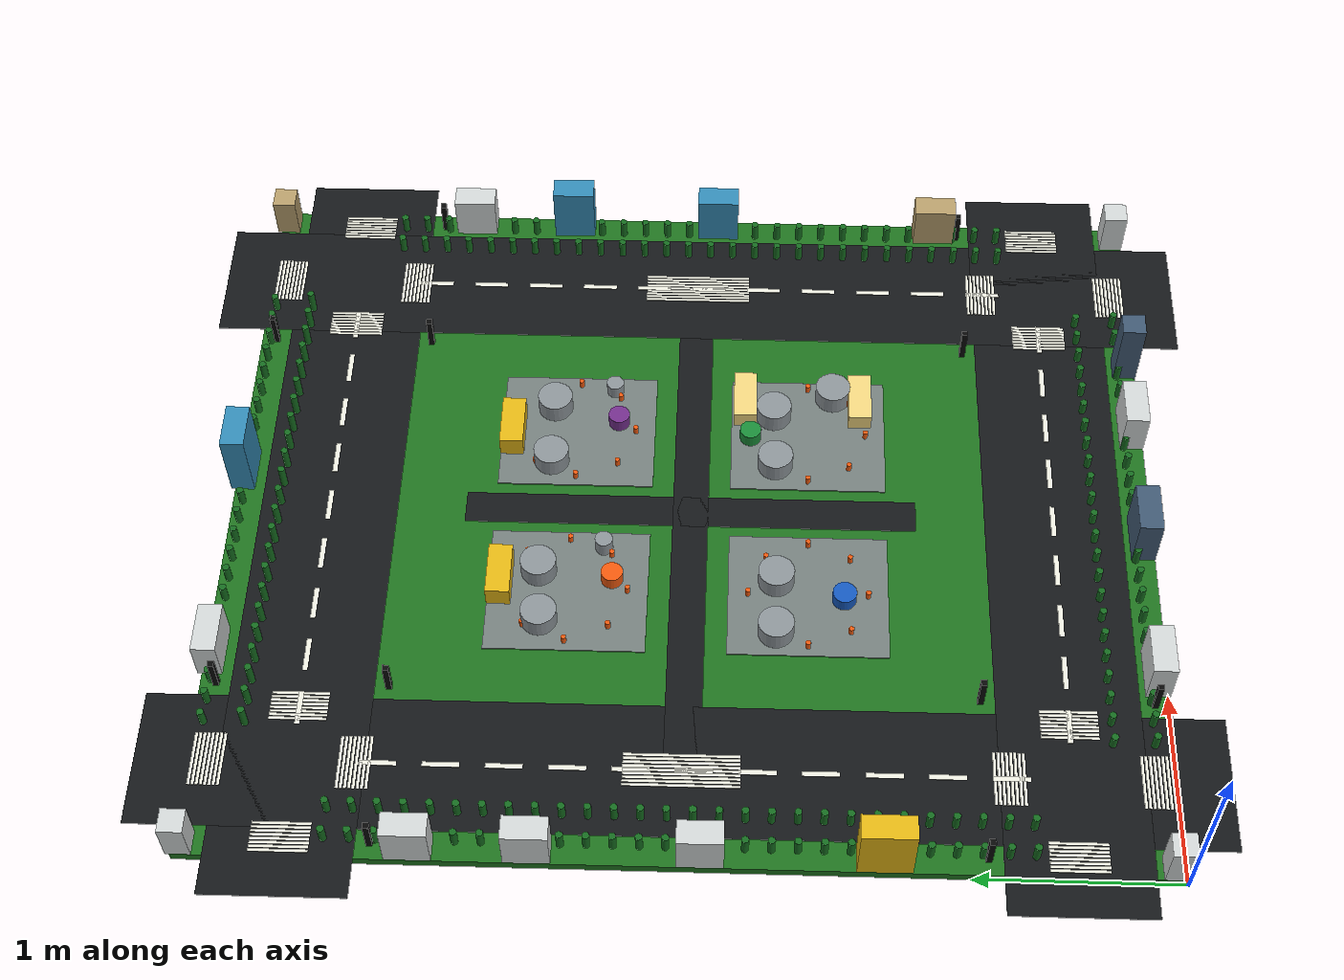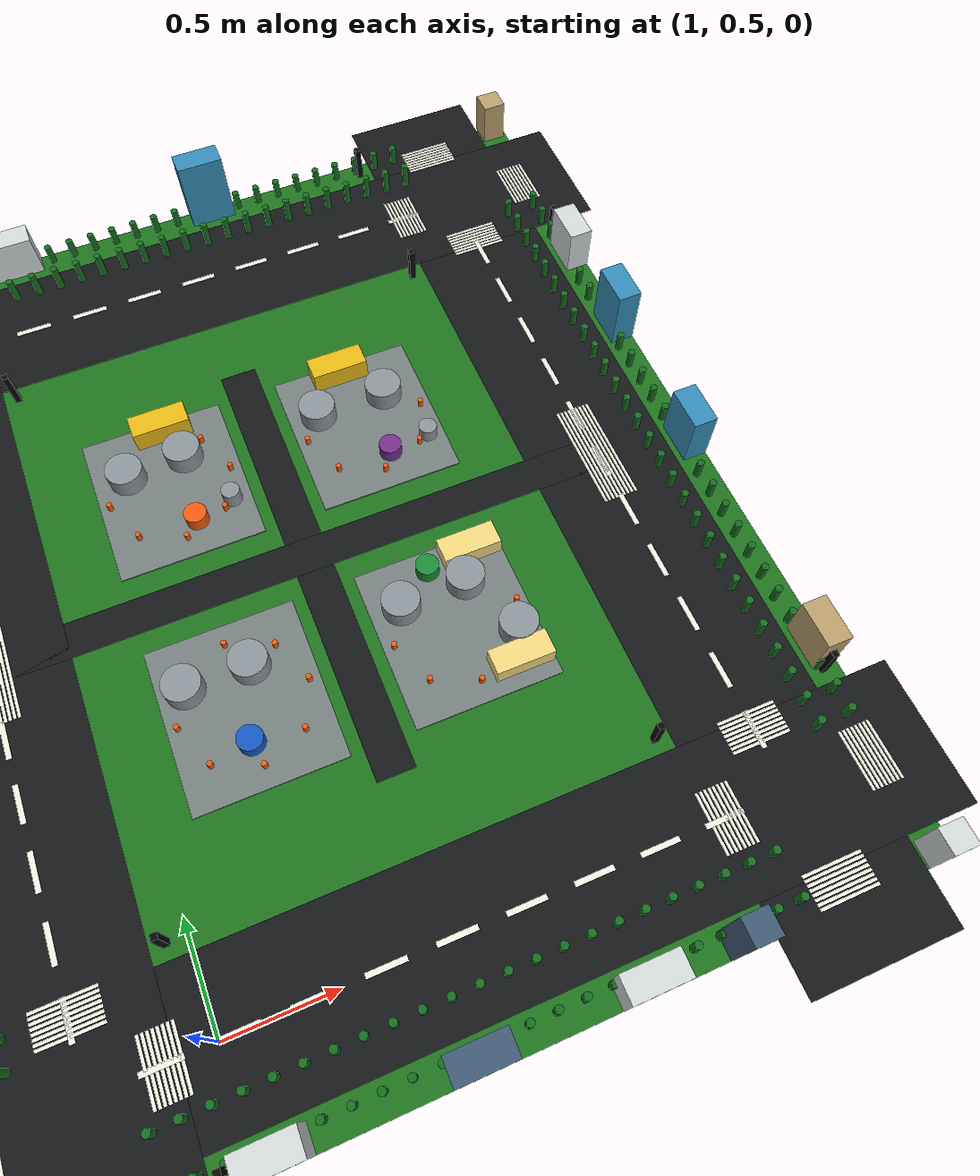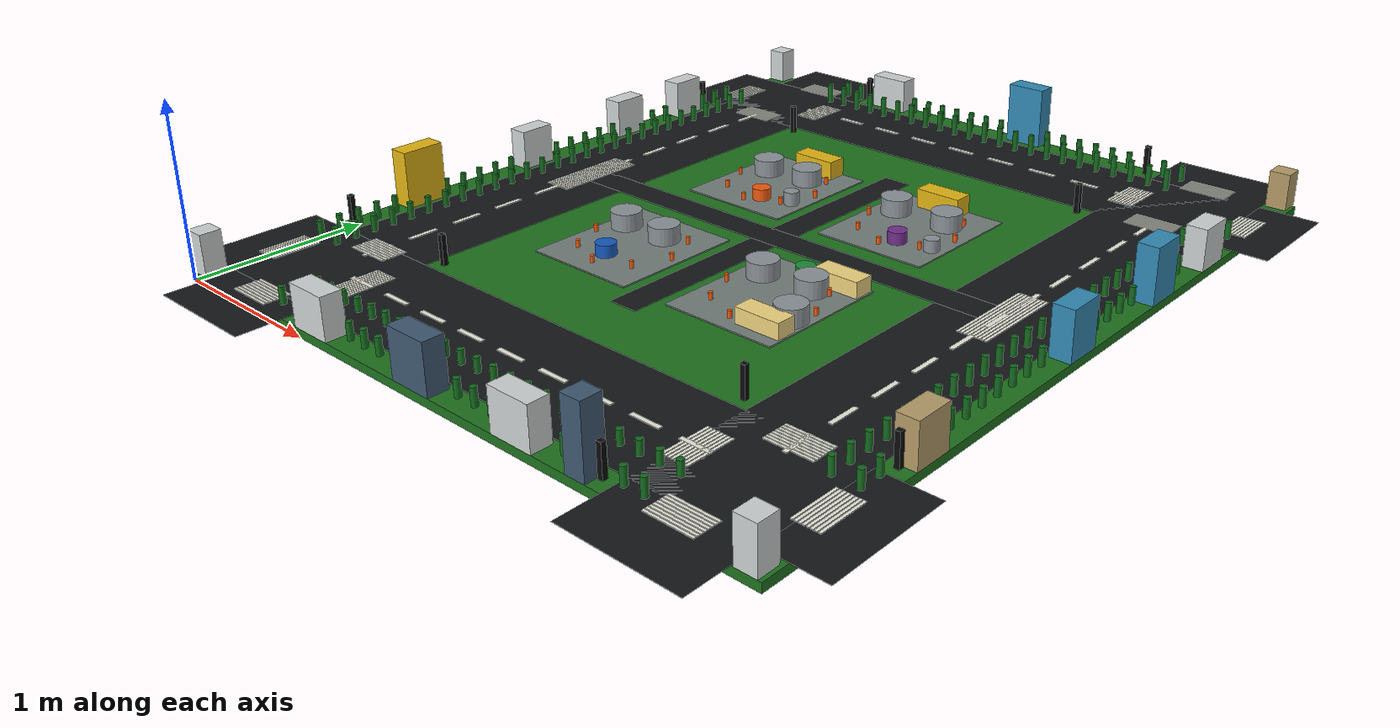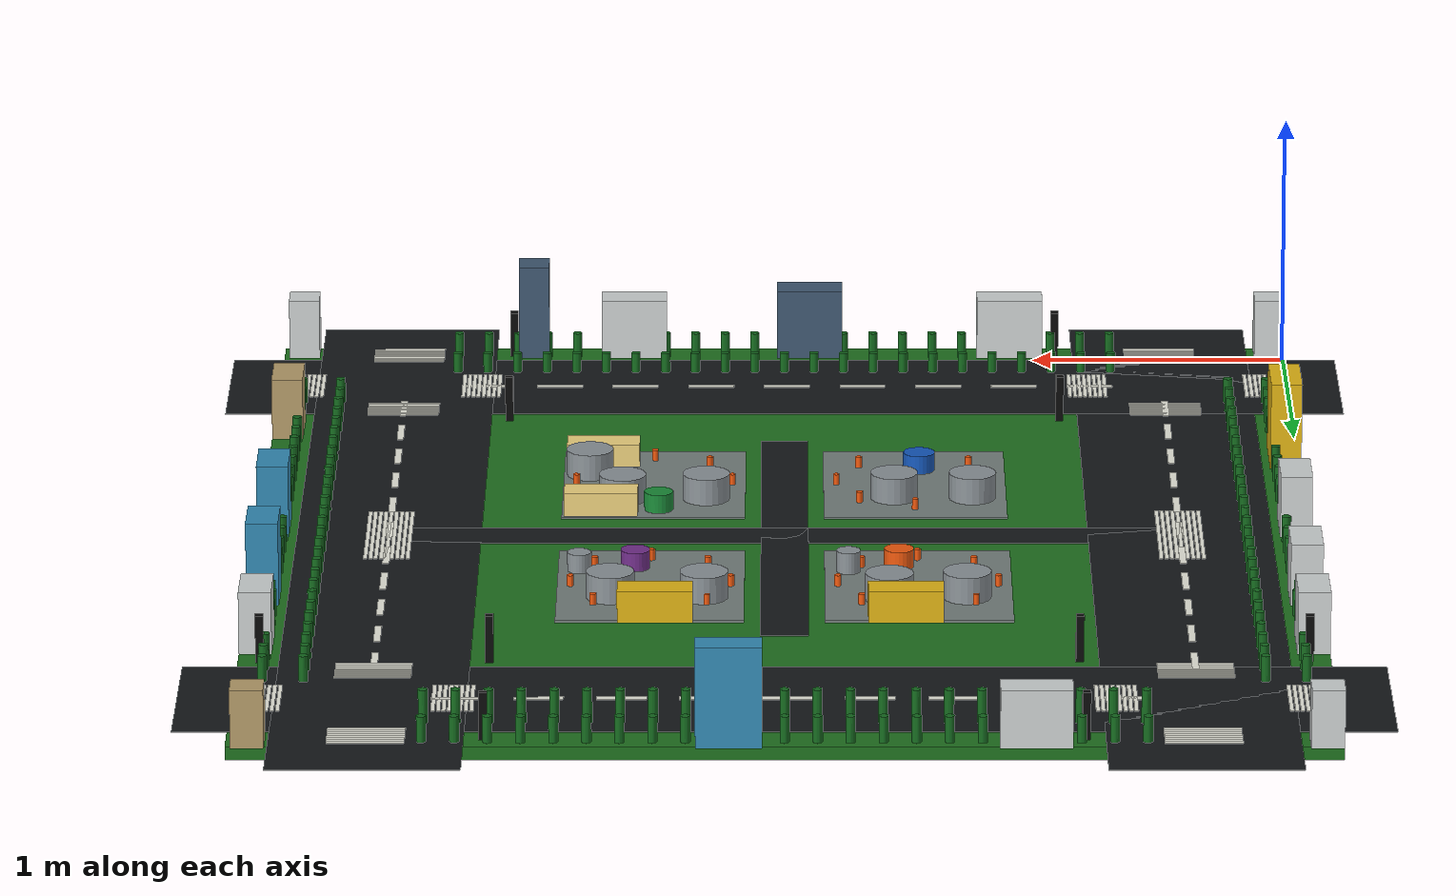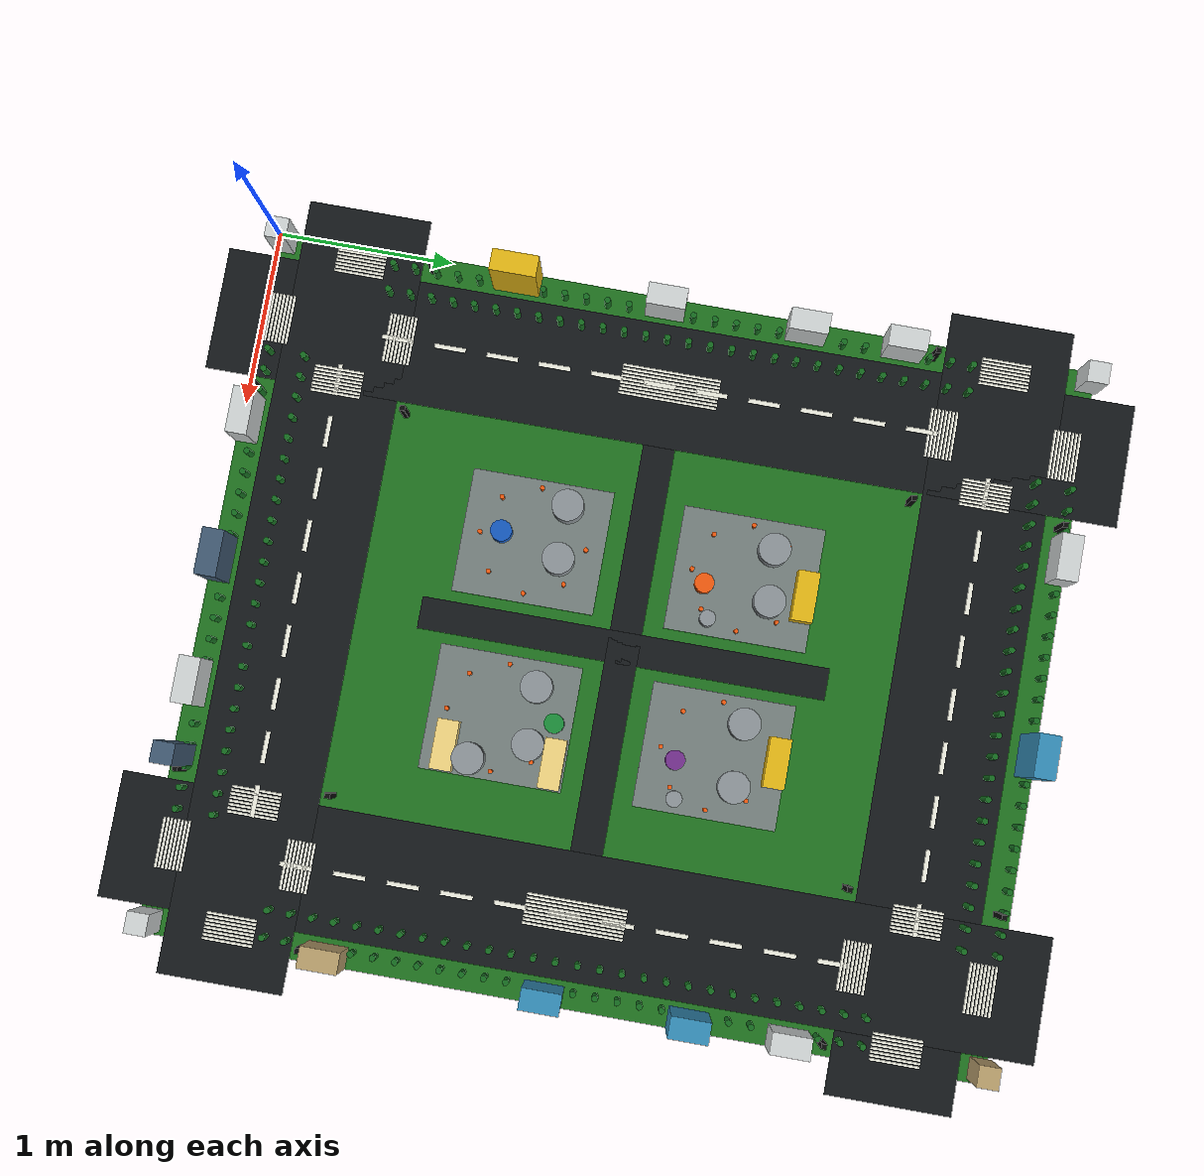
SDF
<?xml version="1.0"?>
<sdf version="1.7"><world name="sandbox"><model name="sandbox_deck"><static>true</static><pose>2.0 2.35 0.025 0 0 0</pose><link name="link"><collision name="collision"><geometry><box><size>4.0 4.7 0.05</size></box></geometry></collision><visual name="visual"><geometry><box><size>4.0 4.7 0.05</size></box></geometry><material><ambient>0.12 0.45 0.12 1</ambient><diffuse>0.12 0.45 0.12 1</diffuse></material></visual></link></model><model name="RD-RING-W"><static>true</static><pose>0.5 2.35 0.051000000000000004 0 0 0</pose><link name="link"><collision name="collision"><geometry><box><size>0.7000000000000001 5.2 0.002</size></box></geometry></collision><visual name="visual"><geometry><box><size>0.7000000000000001 5.2 0.002</size></box></geometry><material><ambient>0.08 0.09 0.1 1</ambient><diffuse>0.08 0.09 0.1 1</diffuse></material></visual></link></model><model name="RD-RING-E"><static>true</static><pose>3.5 2.35 0.051000000000000004 0 0 0</pose><link name="link"><collision name="collision"><geometry><box><size>0.7000000000000001 5.2 0.002</size></box></geometry></collision><visual name="visual"><geometry><box><size>0.7000000000000001 5.2 0.002</size></box></geometry><material><ambient>0.08 0.09 0.1 1</ambient><diffuse>0.08 0.09 0.1 1</diffuse></material></visual></link></model><model name="RD-RING-S"><static>true</static><pose>2.0 0.5 0.051000000000000004 0 0 0</pose><link name="link"><collision name="collision"><geometry><box><size>4.4 0.7000000000000001 0.002</size></box></geometry></collision><visual name="visual"><geometry><box><size>4.4 0.7000000000000001 0.002</size></box></geometry><material><ambient>0.08 0.09 0.1 1</ambient><diffuse>0.08 0.09 0.1 1</diffuse></material></visual></link></model><model name="RD-RING-N"><static>true</static><pose>2.0 4.2 0.051000000000000004 0 0 0</pose><link name="link"><collision name="collision"><geometry><box><size>4.4 0.7000000000000001 0.002</size></box></geometry></collision><visual name="visual"><geometry><box><size>4.4 0.7000000000000001 0.002</size></box></geometry><material><ambient>0.08 0.09 0.1 1</ambient><diffuse>0.08 0.09 0.1 1</diffuse></material></visual></link></model><model name="RD-C-X"><static>true</static><pose>2.0 2.35 0.051000000000000004 0 0 0</pose><link name="link"><collision name="collision"><geometry><box><size>3.0 0.18 0.002</size></box></geometry></collision><visual name="visual"><geometry><box><size>3.0 0.18 0.002</size></box></geometry><material><ambient>0.08 0.09 0.1 1</ambient><diffuse>0.08 0.09 0.1 1</diffuse></material></visual></link></model><model name="RD-C-Y"><static>true</static><pose>2.0 2.35 0.051000000000000004 0 0 0</pose><link name="link"><collision name="collision"><geometry><box><size>0.18 2.3000000000000003 0.002</size></box></geometry></collision><visual name="visual"><geometry><box><size>0.18 2.3000000000000003 0.002</size></box></geometry><material><ambient>0.08 0.09 0.1 1</ambient><diffuse>0.08 0.09 0.1 1</diffuse></material></visual></link></model><model name="LM-RING-W-01"><static>true</static><pose>0.5 0.79 0.05450000000000001 0 0 0</pose><link name="link"><collision name="collision"><geometry><box><size>0.025 0.18 0.004</size></box></geometry></collision><visual name="visual"><geometry><box><size>0.025 0.18 0.004</size></box></geometry><material><ambient>0.93 0.93 0.88 1</ambient><diffuse>0.93 0.93 0.88 1</diffuse></material></visual></link></model><model name="LM-RING-W-02"><static>true</static><pose>0.5 1.09 0.05450000000000001 0 0 0</pose><link name="link"><collision name="collision"><geometry><box><size>0.025 0.18 0.004</size></box></geometry></collision><visual name="visual"><geometry><box><size>0.025 0.18 0.004</size></box></geometry><material><ambient>0.93 0.93 0.88 1</ambient><diffuse>0.93 0.93 0.88 1</diffuse></material></visual></link></model><model name="LM-RING-W-03"><static>true</static><pose>0.5 1.3900000000000001 0.05450000000000001 0 0 0</pose><link name="link"><collision name="collision"><geometry><box><size>0.025 0.18 0.004</size></box></geometry></collision><visual name="visual"><geometry><box><size>0.025 0.18 0.004</size></box></geometry><material><ambient>0.93 0.93 0.88 1</ambient><diffuse>0.93 0.93 0.88 1</diffuse></material></visual></link></model><model name="LM-RING-W-04"><static>true</static><pose>0.5 1.69 0.05450000000000001 0 0 0</pose><link name="link"><collision name="collision"><geometry><box><size>0.025 0.18 0.004</size></box></geometry></collision><visual name="visual"><geometry><box><size>0.025 0.18 0.004</size></box></geometry><material><ambient>0.93 0.93 0.88 1</ambient><diffuse>0.93 0.93 0.88 1</diffuse></material></visual></link></model><model name="LM-RING-W-05"><static>true</static><pose>0.5 1.9900000000000002 0.05450000000000001 0 0 0</pose><link name="link"><collision name="collision"><geometry><box><size>0.025 0.18 0.004</size></box></geometry></collision><visual name="visual"><geometry><box><size>0.025 0.18 0.004</size></box></geometry><material><ambient>0.93 0.93 0.88 1</ambient><diffuse>0.93 0.93 0.88 1</diffuse></material></visual></link></model><model name="LM-RING-W-06"><static>true</static><pose>0.5 2.29 0.05450000000000001 0 0 0</pose><link name="link"><collision name="collision"><geometry><box><size>0.025 0.18 0.004</size></box></geometry></collision><visual name="visual"><geometry><box><size>0.025 0.18 0.004</size></box></geometry><material><ambient>0.93 0.93 0.88 1</ambient><diffuse>0.93 0.93 0.88 1</diffuse></material></visual></link></model><model name="LM-RING-W-07"><static>true</static><pose>0.5 2.59 0.05450000000000001 0 0 0</pose><link name="link"><collision name="collision"><geometry><box><size>0.025 0.18 0.004</size></box></geometry></collision><visual name="visual"><geometry><box><size>0.025 0.18 0.004</size></box></geometry><material><ambient>0.93 0.93 0.88 1</ambient><diffuse>0.93 0.93 0.88 1</diffuse></material></visual></link></model><model name="LM-RING-W-08"><static>true</static><pose>0.5 2.89 0.05450000000000001 0 0 0</pose><link name="link"><collision name="collision"><geometry><box><size>0.025 0.18 0.004</size></box></geometry></collision><visual name="visual"><geometry><box><size>0.025 0.18 0.004</size></box></geometry><material><ambient>0.93 0.93 0.88 1</ambient><diffuse>0.93 0.93 0.88 1</diffuse></material></visual></link></model><model name="LM-RING-W-09"><static>true</static><pose>0.5 3.19 0.05450000000000001 0 0 0</pose><link name="link"><collision name="collision"><geometry><box><size>0.025 0.18 0.004</size></box></geometry></collision><visual name="visual"><geometry><box><size>0.025 0.18 0.004</size></box></geometry><material><ambient>0.93 0.93 0.88 1</ambient><diffuse>0.93 0.93 0.88 1</diffuse></material></visual></link></model><model name="LM-RING-W-10"><static>true</static><pose>0.5 3.4899999999999998 0.05450000000000001 0 0 0</pose><link name="link"><collision name="collision"><geometry><box><size>0.025 0.18 0.004</size></box></geometry></collision><visual name="visual"><geometry><box><size>0.025 0.18 0.004</size></box></geometry><material><ambient>0.93 0.93 0.88 1</ambient><diffuse>0.93 0.93 0.88 1</diffuse></material></visual></link></model><model name="LM-RING-W-11"><static>true</static><pose>0.5 3.79 0.05450000000000001 0 0 0</pose><link name="link"><collision name="collision"><geometry><box><size>0.025 0.18 0.004</size></box></geometry></collision><visual name="visual"><geometry><box><size>0.025 0.18 0.004</size></box></geometry><material><ambient>0.93 0.93 0.88 1</ambient><diffuse>0.93 0.93 0.88 1</diffuse></material></visual></link></model><model name="LM-RING-E-01"><static>true</static><pose>3.5 0.79 0.05450000000000001 0 0 0</pose><link name="link"><collision name="collision"><geometry><box><size>0.025 0.18 0.004</size></box></geometry></collision><visual name="visual"><geometry><box><size>0.025 0.18 0.004</size></box></geometry><material><ambient>0.93 0.93 0.88 1</ambient><diffuse>0.93 0.93 0.88 1</diffuse></material></visual></link></model><model name="LM-RING-E-02"><static>true</static><pose>3.5 1.09 0.05450000000000001 0 0 0</pose><link name="link"><collision name="collision"><geometry><box><size>0.025 0.18 0.004</size></box></geometry></collision><visual name="visual"><geometry><box><size>0.025 0.18 0.004</size></box></geometry><material><ambient>0.93 0.93 0.88 1</ambient><diffuse>0.93 0.93 0.88 1</diffuse></material></visual></link></model><model name="LM-RING-E-03"><static>true</static><pose>3.5 1.3900000000000001 0.05450000000000001 0 0 0</pose><link name="link"><collision name="collision"><geometry><box><size>0.025 0.18 0.004</size></box></geometry></collision><visual name="visual"><geometry><box><size>0.025 0.18 0.004</size></box></geometry><material><ambient>0.93 0.93 0.88 1</ambient><diffuse>0.93 0.93 0.88 1</diffuse></material></visual></link></model><model name="LM-RING-E-04"><static>true</static><pose>3.5 1.69 0.05450000000000001 0 0 0</pose><link name="link"><collision name="collision"><geometry><box><size>0.025 0.18 0.004</size></box></geometry></collision><visual name="visual"><geometry><box><size>0.025 0.18 0.004</size></box></geometry><material><ambient>0.93 0.93 0.88 1</ambient><diffuse>0.93 0.93 0.88 1</diffuse></material></visual></link></model><model name="LM-RING-E-05"><static>true</static><pose>3.5 1.9900000000000002 0.05450000000000001 0 0 0</pose><link name="link"><collision name="collision"><geometry><box><size>0.025 0.18 0.004</size></box></geometry></collision><visual name="visual"><geometry><box><size>0.025 0.18 0.004</size></box></geometry><material><ambient>0.93 0.93 0.88 1</ambient><diffuse>0.93 0.93 0.88 1</diffuse></material></visual></link></model><model name="LM-RING-E-06"><static>true</static><pose>3.5 2.29 0.05450000000000001 0 0 0</pose><link name="link"><collision name="collision"><geometry><box><size>0.025 0.18 0.004</size></box></geometry></collision><visual name="visual"><geometry><box><size>0.025 0.18 0.004</size></box></geometry><material><ambient>0.93 0.93 0.88 1</ambient><diffuse>0.93 0.93 0.88 1</diffuse></material></visual></link></model><model name="LM-RING-E-07"><static>true</static><pose>3.5 2.59 0.05450000000000001 0 0 0</pose><link name="link"><collision name="collision"><geometry><box><size>0.025 0.18 0.004</size></box></geometry></collision><visual name="visual"><geometry><box><size>0.025 0.18 0.004</size></box></geometry><material><ambient>0.93 0.93 0.88 1</ambient><diffuse>0.93 0.93 0.88 1</diffuse></material></visual></link></model><model name="LM-RING-E-08"><static>true</static><pose>3.5 2.89 0.05450000000000001 0 0 0</pose><link name="link"><collision name="collision"><geometry><box><size>0.025 0.18 0.004</size></box></geometry></collision><visual name="visual"><geometry><box><size>0.025 0.18 0.004</size></box></geometry><material><ambient>0.93 0.93 0.88 1</ambient><diffuse>0.93 0.93 0.88 1</diffuse></material></visual></link></model><model name="LM-RING-E-09"><static>true</static><pose>3.5 3.19 0.05450000000000001 0 0 0</pose><link name="link"><collision name="collision"><geometry><box><size>0.025 0.18 0.004</size></box></geometry></collision><visual name="visual"><geometry><box><size>0.025 0.18 0.004</size></box></geometry><material><ambient>0.93 0.93 0.88 1</ambient><diffuse>0.93 0.93 0.88 1</diffuse></material></visual></link></model><model name="LM-RING-E-10"><static>true</static><pose>3.5 3.4899999999999998 0.05450000000000001 0 0 0</pose><link name="link"><collision name="collision"><geometry><box><size>0.025 0.18 0.004</size></box></geometry></collision><visual name="visual"><geometry><box><size>0.025 0.18 0.004</size></box></geometry><material><ambient>0.93 0.93 0.88 1</ambient><diffuse>0.93 0.93 0.88 1</diffuse></material></visual></link></model><model name="LM-RING-E-11"><static>true</static><pose>3.5 3.79 0.05450000000000001 0 0 0</pose><link name="link"><collision name="collision"><geometry><box><size>0.025 0.18 0.004</size></box></geometry></collision><visual name="visual"><geometry><box><size>0.025 0.18 0.004</size></box></geometry><material><ambient>0.93 0.93 0.88 1</ambient><diffuse>0.93 0.93 0.88 1</diffuse></material></visual></link></model><model name="LM-RING-S-01"><static>true</static><pose>0.79 0.5 0.05450000000000001 0 0 0</pose><link name="link"><collision name="collision"><geometry><box><size>0.18 0.025 0.004</size></box></geometry></collision><visual name="visual"><geometry><box><size>0.18 0.025 0.004</size></box></geometry><material><ambient>0.93 0.93 0.88 1</ambient><diffuse>0.93 0.93 0.88 1</diffuse></material></visual></link></model><model name="LM-RING-S-02"><static>true</static><pose>1.09 0.5 0.05450000000000001 0 0 0</pose><link name="link"><collision name="collision"><geometry><box><size>0.18 0.025 0.004</size></box></geometry></collision><visual name="visual"><geometry><box><size>0.18 0.025 0.004</size></box></geometry><material><ambient>0.93 0.93 0.88 1</ambient><diffuse>0.93 0.93 0.88 1</diffuse></material></visual></link></model><model name="LM-RING-S-03"><static>true</static><pose>1.3900000000000001 0.5 0.05450000000000001 0 0 0</pose><link name="link"><collision name="collision"><geometry><box><size>0.18 0.025 0.004</size></box></geometry></collision><visual name="visual"><geometry><box><size>0.18 0.025 0.004</size></box></geometry><material><ambient>0.93 0.93 0.88 1</ambient><diffuse>0.93 0.93 0.88 1</diffuse></material></visual></link></model><model name="LM-RING-S-04"><static>true</static><pose>1.69 0.5 0.05450000000000001 0 0 0</pose><link name="link"><collision name="collision"><geometry><box><size>0.18 0.025 0.004</size></box></geometry></collision><visual name="visual"><geometry><box><size>0.18 0.025 0.004</size></box></geometry><material><ambient>0.93 0.93 0.88 1</ambient><diffuse>0.93 0.93 0.88 1</diffuse></material></visual></link></model><model name="LM-RING-S-05"><static>true</static><pose>1.9900000000000002 0.5 0.05450000000000001 0 0 0</pose><link name="link"><collision name="collision"><geometry><box><size>0.18 0.025 0.004</size></box></geometry></collision><visual name="visual"><geometry><box><size>0.18 0.025 0.004</size></box></geometry><material><ambient>0.93 0.93 0.88 1</ambient><diffuse>0.93 0.93 0.88 1</diffuse></material></visual></link></model><model name="LM-RING-S-06"><static>true</static><pose>2.29 0.5 0.05450000000000001 0 0 0</pose><link name="link"><collision name="collision"><geometry><box><size>0.18 0.025 0.004</size></box></geometry></collision><visual name="visual"><geometry><box><size>0.18 0.025 0.004</size></box></geometry><material><ambient>0.93 0.93 0.88 1</ambient><diffuse>0.93 0.93 0.88 1</diffuse></material></visual></link></model><model name="LM-RING-S-07"><static>true</static><pose>2.59 0.5 0.05450000000000001 0 0 0</pose><link name="link"><collision name="collision"><geometry><box><size>0.18 0.025 0.004</size></box></geometry></collision><visual name="visual"><geometry><box><size>0.18 0.025 0.004</size></box></geometry><material><ambient>0.93 0.93 0.88 1</ambient><diffuse>0.93 0.93 0.88 1</diffuse></material></visual></link></model><model name="LM-RING-S-08"><static>true</static><pose>2.89 0.5 0.05450000000000001 0 0 0</pose><link name="link"><collision name="collision"><geometry><box><size>0.18 0.025 0.004</size></box></geometry></collision><visual name="visual"><geometry><box><size>0.18 0.025 0.004</size></box></geometry><material><ambient>0.93 0.93 0.88 1</ambient><diffuse>0.93 0.93 0.88 1</diffuse></material></visual></link></model><model name="LM-RING-S-09"><static>true</static><pose>3.19 0.5 0.05450000000000001 0 0 0</pose><link name="link"><collision name="collision"><geometry><box><size>0.18 0.025 0.004</size></box></geometry></collision><visual name="visual"><geometry><box><size>0.18 0.025 0.004</size></box></geometry><material><ambient>0.93 0.93 0.88 1</ambient><diffuse>0.93 0.93 0.88 1</diffuse></material></visual></link></model><model name="LM-RING-N-01"><static>true</static><pose>0.79 4.2 0.05450000000000001 0 0 0</pose><link name="link"><collision name="collision"><geometry><box><size>0.18 0.025 0.004</size></box></geometry></collision><visual name="visual"><geometry><box><size>0.18 0.025 0.004</size></box></geometry><material><ambient>0.93 0.93 0.88 1</ambient><diffuse>0.93 0.93 0.88 1</diffuse></material></visual></link></model><model name="LM-RING-N-02"><static>true</static><pose>1.09 4.2 0.05450000000000001 0 0 0</pose><link name="link"><collision name="collision"><geometry><box><size>0.18 0.025 0.004</size></box></geometry></collision><visual name="visual"><geometry><box><size>0.18 0.025 0.004</size></box></geometry><material><ambient>0.93 0.93 0.88 1</ambient><diffuse>0.93 0.93 0.88 1</diffuse></material></visual></link></model><model name="LM-RING-N-03"><static>true</static><pose>1.3900000000000001 4.2 0.05450000000000001 0 0 0</pose><link name="link"><collision name="collision"><geometry><box><size>0.18 0.025 0.004</size></box></geometry></collision><visual name="visual"><geometry><box><size>0.18 0.025 0.004</size></box></geometry><material><ambient>0.93 0.93 0.88 1</ambient><diffuse>0.93 0.93 0.88 1</diffuse></material></visual></link></model><model name="LM-RING-N-04"><static>true</static><pose>1.69 4.2 0.05450000000000001 0 0 0</pose><link name="link"><collision name="collision"><geometry><box><size>0.18 0.025 0.004</size></box></geometry></collision><visual name="visual"><geometry><box><size>0.18 0.025 0.004</size></box></geometry><material><ambient>0.93 0.93 0.88 1</ambient><diffuse>0.93 0.93 0.88 1</diffuse></material></visual></link></model><model name="LM-RING-N-05"><static>true</static><pose>1.9900000000000002 4.2 0.05450000000000001 0 0 0</pose><link name="link"><collision name="collision"><geometry><box><size>0.18 0.025 0.004</size></box></geometry></collision><visual name="visual"><geometry><box><size>0.18 0.025 0.004</size></box></geometry><material><ambient>0.93 0.93 0.88 1</ambient><diffuse>0.93 0.93 0.88 1</diffuse></material></visual></link></model><model name="LM-RING-N-06"><static>true</static><pose>2.29 4.2 0.05450000000000001 0 0 0</pose><link name="link"><collision name="collision"><geometry><box><size>0.18 0.025 0.004</size></box></geometry></collision><visual name="visual"><geometry><box><size>0.18 0.025 0.004</size></box></geometry><material><ambient>0.93 0.93 0.88 1</ambient><diffuse>0.93 0.93 0.88 1</diffuse></material></visual></link></model><model name="LM-RING-N-07"><static>true</static><pose>2.59 4.2 0.05450000000000001 0 0 0</pose><link name="link"><collision name="collision"><geometry><box><size>0.18 0.025 0.004</size></box></geometry></collision><visual name="visual"><geometry><box><size>0.18 0.025 0.004</size></box></geometry><material><ambient>0.93 0.93 0.88 1</ambient><diffuse>0.93 0.93 0.88 1</diffuse></material></visual></link></model><model name="LM-RING-N-08"><static>true</static><pose>2.89 4.2 0.05450000000000001 0 0 0</pose><link name="link"><collision name="collision"><geometry><box><size>0.18 0.025 0.004</size></box></geometry></collision><visual name="visual"><geometry><box><size>0.18 0.025 0.004</size></box></geometry><material><ambient>0.93 0.93 0.88 1</ambient><diffuse>0.93 0.93 0.88 1</diffuse></material></visual></link></model><model name="LM-RING-N-09"><static>true</static><pose>3.19 4.2 0.05450000000000001 0 0 0</pose><link name="link"><collision name="collision"><geometry><box><size>0.18 0.025 0.004</size></box></geometry></collision><visual name="visual"><geometry><box><size>0.18 0.025 0.004</size></box></geometry><material><ambient>0.93 0.93 0.88 1</ambient><diffuse>0.93 0.93 0.88 1</diffuse></material></visual></link></model><model name="CW-SW-X-01"><static>true</static><pose>0.5 0.73 0.05450000000000001 0 0 0</pose><link name="link"><collision name="collision"><geometry><box><size>0.28 0.014 0.004</size></box></geometry></collision><visual name="visual"><geometry><box><size>0.28 0.014 0.004</size></box></geometry><material><ambient>0.93 0.93 0.88 1</ambient><diffuse>0.93 0.93 0.88 1</diffuse></material></visual></link></model><model name="CW-SW-X-02"><static>true</static><pose>0.5 0.75 0.05450000000000001 0 0 0</pose><link name="link"><collision name="collision"><geometry><box><size>0.28 0.014 0.004</size></box></geometry></collision><visual name="visual"><geometry><box><size>0.28 0.014 0.004</size></box></geometry><material><ambient>0.93 0.93 0.88 1</ambient><diffuse>0.93 0.93 0.88 1</diffuse></material></visual></link></model><model name="CW-SW-X-03"><static>true</static><pose>0.5 0.77 0.05450000000000001 0 0 0</pose><link name="link"><collision name="collision"><geometry><box><size>0.28 0.014 0.004</size></box></geometry></collision><visual name="visual"><geometry><box><size>0.28 0.014 0.004</size></box></geometry><material><ambient>0.93 0.93 0.88 1</ambient><diffuse>0.93 0.93 0.88 1</diffuse></material></visual></link></model><model name="CW-SW-X-04"><static>true</static><pose>0.5 0.79 0.05450000000000001 0 0 0</pose><link name="link"><collision name="collision"><geometry><box><size>0.28 0.014 0.004</size></box></geometry></collision><visual name="visual"><geometry><box><size>0.28 0.014 0.004</size></box></geometry><material><ambient>0.93 0.93 0.88 1</ambient><diffuse>0.93 0.93 0.88 1</diffuse></material></visual></link></model><model name="CW-SW-X-05"><static>true</static><pose>0.5 0.81 0.05450000000000001 0 0 0</pose><link name="link"><collision name="collision"><geometry><box><size>0.28 0.014 0.004</size></box></geometry></collision><visual name="visual"><geometry><box><size>0.28 0.014 0.004</size></box></geometry><material><ambient>0.93 0.93 0.88 1</ambient><diffuse>0.93 0.93 0.88 1</diffuse></material></visual></link></model><model name="CW-SW-X-06"><static>true</static><pose>0.5 0.8300000000000001 0.05450000000000001 0 0 0</pose><link name="link"><collision name="collision"><geometry><box><size>0.28 0.014 0.004</size></box></geometry></collision><visual name="visual"><geometry><box><size>0.28 0.014 0.004</size></box></geometry><material><ambient>0.93 0.93 0.88 1</ambient><diffuse>0.93 0.93 0.88 1</diffuse></material></visual></link></model><model name="CW-SW-X-07"><static>true</static><pose>0.5 0.8500000000000001 0.05450000000000001 0 0 0</pose><link name="link"><collision name="collision"><geometry><box><size>0.28 0.014 0.004</size></box></geometry></collision><visual name="visual"><geometry><box><size>0.28 0.014 0.004</size></box></geometry><material><ambient>0.93 0.93 0.88 1</ambient><diffuse>0.93 0.93 0.88 1</diffuse></material></visual></link></model><model name="CW-SW-X-08"><static>true</static><pose>0.5 0.8700000000000001 0.05450000000000001 0 0 0</pose><link name="link"><collision name="collision"><geometry><box><size>0.28 0.014 0.004</size></box></geometry></collision><visual name="visual"><geometry><box><size>0.28 0.014 0.004</size></box></geometry><material><ambient>0.93 0.93 0.88 1</ambient><diffuse>0.93 0.93 0.88 1</diffuse></material></visual></link></model><model name="CW-SW-Y-01"><static>true</static><pose>0.73 0.5 0.05450000000000001 0 0 0</pose><link name="link"><collision name="collision"><geometry><box><size>0.014 0.28 0.004</size></box></geometry></collision><visual name="visual"><geometry><box><size>0.014 0.28 0.004</size></box></geometry><material><ambient>0.93 0.93 0.88 1</ambient><diffuse>0.93 0.93 0.88 1</diffuse></material></visual></link></model><model name="CW-SW-Y-02"><static>true</static><pose>0.75 0.5 0.05450000000000001 0 0 0</pose><link name="link"><collision name="collision"><geometry><box><size>0.014 0.28 0.004</size></box></geometry></collision><visual name="visual"><geometry><box><size>0.014 0.28 0.004</size></box></geometry><material><ambient>0.93 0.93 0.88 1</ambient><diffuse>0.93 0.93 0.88 1</diffuse></material></visual></link></model><model name="CW-SW-Y-03"><static>true</static><pose>0.77 0.5 0.05450000000000001 0 0 0</pose><link name="link"><collision name="collision"><geometry><box><size>0.014 0.28 0.004</size></box></geometry></collision><visual name="visual"><geometry><box><size>0.014 0.28 0.004</size></box></geometry><material><ambient>0.93 0.93 0.88 1</ambient><diffuse>0.93 0.93 0.88 1</diffuse></material></visual></link></model><model name="CW-SW-Y-04"><static>true</static><pose>0.79 0.5 0.05450000000000001 0 0 0</pose><link name="link"><collision name="collision"><geometry><box><size>0.014 0.28 0.004</size></box></geometry></collision><visual name="visual"><geometry><box><size>0.014 0.28 0.004</size></box></geometry><material><ambient>0.93 0.93 0.88 1</ambient><diffuse>0.93 0.93 0.88 1</diffuse></material></visual></link></model><model name="CW-SW-Y-05"><static>true</static><pose>0.81 0.5 0.05450000000000001 0 0 0</pose><link name="link"><collision name="collision"><geometry><box><size>0.014 0.28 0.004</size></box></geometry></collision><visual name="visual"><geometry><box><size>0.014 0.28 0.004</size></box></geometry><material><ambient>0.93 0.93 0.88 1</ambient><diffuse>0.93 0.93 0.88 1</diffuse></material></visual></link></model><model name="CW-SW-Y-06"><static>true</static><pose>0.8300000000000001 0.5 0.05450000000000001 0 0 0</pose><link name="link"><collision name="collision"><geometry><box><size>0.014 0.28 0.004</size></box></geometry></collision><visual name="visual"><geometry><box><size>0.014 0.28 0.004</size></box></geometry><material><ambient>0.93 0.93 0.88 1</ambient><diffuse>0.93 0.93 0.88 1</diffuse></material></visual></link></model><model name="CW-SW-Y-07"><static>true</static><pose>0.8500000000000001 0.5 0.05450000000000001 0 0 0</pose><link name="link"><collision name="collision"><geometry><box><size>0.014 0.28 0.004</size></box></geometry></collision><visual name="visual"><geometry><box><size>0.014 0.28 0.004</size></box></geometry><material><ambient>0.93 0.93 0.88 1</ambient><diffuse>0.93 0.93 0.88 1</diffuse></material></visual></link></model><model name="CW-SW-Y-08"><static>true</static><pose>0.8700000000000001 0.5 0.05450000000000001 0 0 0</pose><link name="link"><collision name="collision"><geometry><box><size>0.014 0.28 0.004</size></box></geometry></collision><visual name="visual"><geometry><box><size>0.014 0.28 0.004</size></box></geometry><material><ambient>0.93 0.93 0.88 1</ambient><diffuse>0.93 0.93 0.88 1</diffuse></material></visual></link></model><model name="CW-SE-X-01"><static>true</static><pose>3.5 0.73 0.05450000000000001 0 0 0</pose><link name="link"><collision name="collision"><geometry><box><size>0.28 0.014 0.004</size></box></geometry></collision><visual name="visual"><geometry><box><size>0.28 0.014 0.004</size></box></geometry><material><ambient>0.93 0.93 0.88 1</ambient><diffuse>0.93 0.93 0.88 1</diffuse></material></visual></link></model><model name="CW-SE-X-02"><static>true</static><pose>3.5 0.75 0.05450000000000001 0 0 0</pose><link name="link"><collision name="collision"><geometry><box><size>0.28 0.014 0.004</size></box></geometry></collision><visual name="visual"><geometry><box><size>0.28 0.014 0.004</size></box></geometry><material><ambient>0.93 0.93 0.88 1</ambient><diffuse>0.93 0.93 0.88 1</diffuse></material></visual></link></model><model name="CW-SE-X-03"><static>true</static><pose>3.5 0.77 0.05450000000000001 0 0 0</pose><link name="link"><collision name="collision"><geometry><box><size>0.28 0.014 0.004</size></box></geometry></collision><visual name="visual"><geometry><box><size>0.28 0.014 0.004</size></box></geometry><material><ambient>0.93 0.93 0.88 1</ambient><diffuse>0.93 0.93 0.88 1</diffuse></material></visual></link></model><model name="CW-SE-X-04"><static>true</static><pose>3.5 0.79 0.05450000000000001 0 0 0</pose><link name="link"><collision name="collision"><geometry><box><size>0.28 0.014 0.004</size></box></geometry></collision><visual name="visual"><geometry><box><size>0.28 0.014 0.004</size></box></geometry><material><ambient>0.93 0.93 0.88 1</ambient><diffuse>0.93 0.93 0.88 1</diffuse></material></visual></link></model><model name="CW-SE-X-05"><static>true</static><pose>3.5 0.81 0.05450000000000001 0 0 0</pose><link name="link"><collision name="collision"><geometry><box><size>0.28 0.014 0.004</size></box></geometry></collision><visual name="visual"><geometry><box><size>0.28 0.014 0.004</size></box></geometry><material><ambient>0.93 0.93 0.88 1</ambient><diffuse>0.93 0.93 0.88 1</diffuse></material></visual></link></model><model name="CW-SE-X-06"><static>true</static><pose>3.5 0.8300000000000001 0.05450000000000001 0 0 0</pose><link name="link"><collision name="collision"><geometry><box><size>0.28 0.014 0.004</size></box></geometry></collision><visual name="visual"><geometry><box><size>0.28 0.014 0.004</size></box></geometry><material><ambient>0.93 0.93 0.88 1</ambient><diffuse>0.93 0.93 0.88 1</diffuse></material></visual></link></model><model name="CW-SE-X-07"><static>true</static><pose>3.5 0.8500000000000001 0.05450000000000001 0 0 0</pose><link name="link"><collision name="collision"><geometry><box><size>0.28 0.014 0.004</size></box></geometry></collision><visual name="visual"><geometry><box><size>0.28 0.014 0.004</size></box></geometry><material><ambient>0.93 0.93 0.88 1</ambient><diffuse>0.93 0.93 0.88 1</diffuse></material></visual></link></model><model name="CW-SE-X-08"><static>true</static><pose>3.5 0.8700000000000001 0.05450000000000001 0 0 0</pose><link name="link"><collision name="collision"><geometry><box><size>0.28 0.014 0.004</size></box></geometry></collision><visual name="visual"><geometry><box><size>0.28 0.014 0.004</size></box></geometry><material><ambient>0.93 0.93 0.88 1</ambient><diffuse>0.93 0.93 0.88 1</diffuse></material></visual></link></model><model name="CW-SE-Y-01"><static>true</static><pose>3.1300000000000003 0.5 0.05450000000000001 0 0 0</pose><link name="link"><collision name="collision"><geometry><box><size>0.014 0.28 0.004</size></box></geometry></collision><visual name="visual"><geometry><box><size>0.014 0.28 0.004</size></box></geometry><material><ambient>0.93 0.93 0.88 1</ambient><diffuse>0.93 0.93 0.88 1</diffuse></material></visual></link></model><model name="CW-SE-Y-02"><static>true</static><pose>3.1500000000000004 0.5 0.05450000000000001 0 0 0</pose><link name="link"><collision name="collision"><geometry><box><size>0.014 0.28 0.004</size></box></geometry></collision><visual name="visual"><geometry><box><size>0.014 0.28 0.004</size></box></geometry><material><ambient>0.93 0.93 0.88 1</ambient><diffuse>0.93 0.93 0.88 1</diffuse></material></visual></link></model><model name="CW-SE-Y-03"><static>true</static><pose>3.1700000000000004 0.5 0.05450000000000001 0 0 0</pose><link name="link"><collision name="collision"><geometry><box><size>0.014 0.28 0.004</size></box></geometry></collision><visual name="visual"><geometry><box><size>0.014 0.28 0.004</size></box></geometry><material><ambient>0.93 0.93 0.88 1</ambient><diffuse>0.93 0.93 0.88 1</diffuse></material></visual></link></model><model name="CW-SE-Y-04"><static>true</static><pose>3.1900000000000004 0.5 0.05450000000000001 0 0 0</pose><link name="link"><collision name="collision"><geometry><box><size>0.014 0.28 0.004</size></box></geometry></collision><visual name="visual"><geometry><box><size>0.014 0.28 0.004</size></box></geometry><material><ambient>0.93 0.93 0.88 1</ambient><diffuse>0.93 0.93 0.88 1</diffuse></material></visual></link></model><model name="CW-SE-Y-05"><static>true</static><pose>3.21 0.5 0.05450000000000001 0 0 0</pose><link name="link"><collision name="collision"><geometry><box><size>0.014 0.28 0.004</size></box></geometry></collision><visual name="visual"><geometry><box><size>0.014 0.28 0.004</size></box></geometry><material><ambient>0.93 0.93 0.88 1</ambient><diffuse>0.93 0.93 0.88 1</diffuse></material></visual></link></model><model name="CW-SE-Y-06"><static>true</static><pose>3.23 0.5 0.05450000000000001 0 0 0</pose><link name="link"><collision name="collision"><geometry><box><size>0.014 0.28 0.004</size></box></geometry></collision><visual name="visual"><geometry><box><size>0.014 0.28 0.004</size></box></geometry><material><ambient>0.93 0.93 0.88 1</ambient><diffuse>0.93 0.93 0.88 1</diffuse></material></visual></link></model><model name="CW-SE-Y-07"><static>true</static><pose>3.25 0.5 0.05450000000000001 0 0 0</pose><link name="link"><collision name="collision"><geometry><box><size>0.014 0.28 0.004</size></box></geometry></collision><visual name="visual"><geometry><box><size>0.014 0.28 0.004</size></box></geometry><material><ambient>0.93 0.93 0.88 1</ambient><diffuse>0.93 0.93 0.88 1</diffuse></material></visual></link></model><model name="CW-SE-Y-08"><static>true</static><pose>3.27 0.5 0.05450000000000001 0 0 0</pose><link name="link"><collision name="collision"><geometry><box><size>0.014 0.28 0.004</size></box></geometry></collision><visual name="visual"><geometry><box><size>0.014 0.28 0.004</size></box></geometry><material><ambient>0.93 0.93 0.88 1</ambient><diffuse>0.93 0.93 0.88 1</diffuse></material></visual></link></model><model name="CW-NW-X-01"><static>true</static><pose>0.5 3.83 0.05450000000000001 0 0 0</pose><link name="link"><collision name="collision"><geometry><box><size>0.28 0.014 0.004</size></box></geometry></collision><visual name="visual"><geometry><box><size>0.28 0.014 0.004</size></box></geometry><material><ambient>0.93 0.93 0.88 1</ambient><diffuse>0.93 0.93 0.88 1</diffuse></material></visual></link></model><model name="CW-NW-X-02"><static>true</static><pose>0.5 3.85 0.05450000000000001 0 0 0</pose><link name="link"><collision name="collision"><geometry><box><size>0.28 0.014 0.004</size></box></geometry></collision><visual name="visual"><geometry><box><size>0.28 0.014 0.004</size></box></geometry><material><ambient>0.93 0.93 0.88 1</ambient><diffuse>0.93 0.93 0.88 1</diffuse></material></visual></link></model><model name="CW-NW-X-03"><static>true</static><pose>0.5 3.87 0.05450000000000001 0 0 0</pose><link name="link"><collision name="collision"><geometry><box><size>0.28 0.014 0.004</size></box></geometry></collision><visual name="visual"><geometry><box><size>0.28 0.014 0.004</size></box></geometry><material><ambient>0.93 0.93 0.88 1</ambient><diffuse>0.93 0.93 0.88 1</diffuse></material></visual></link></model><model name="CW-NW-X-04"><static>true</static><pose>0.5 3.89 0.05450000000000001 0 0 0</pose><link name="link"><collision name="collision"><geometry><box><size>0.28 0.014 0.004</size></box></geometry></collision><visual name="visual"><geometry><box><size>0.28 0.014 0.004</size></box></geometry><material><ambient>0.93 0.93 0.88 1</ambient><diffuse>0.93 0.93 0.88 1</diffuse></material></visual></link></model><model name="CW-NW-X-05"><static>true</static><pose>0.5 3.9099999999999997 0.05450000000000001 0 0 0</pose><link name="link"><collision name="collision"><geometry><box><size>0.28 0.014 0.004</size></box></geometry></collision><visual name="visual"><geometry><box><size>0.28 0.014 0.004</size></box></geometry><material><ambient>0.93 0.93 0.88 1</ambient><diffuse>0.93 0.93 0.88 1</diffuse></material></visual></link></model><model name="CW-NW-X-06"><static>true</static><pose>0.5 3.9299999999999997 0.05450000000000001 0 0 0</pose><link name="link"><collision name="collision"><geometry><box><size>0.28 0.014 0.004</size></box></geometry></collision><visual name="visual"><geometry><box><size>0.28 0.014 0.004</size></box></geometry><material><ambient>0.93 0.93 0.88 1</ambient><diffuse>0.93 0.93 0.88 1</diffuse></material></visual></link></model><model name="CW-NW-X-07"><static>true</static><pose>0.5 3.9499999999999997 0.05450000000000001 0 0 0</pose><link name="link"><collision name="collision"><geometry><box><size>0.28 0.014 0.004</size></box></geometry></collision><visual name="visual"><geometry><box><size>0.28 0.014 0.004</size></box></geometry><material><ambient>0.93 0.93 0.88 1</ambient><diffuse>0.93 0.93 0.88 1</diffuse></material></visual></link></model><model name="CW-NW-X-08"><static>true</static><pose>0.5 3.9699999999999998 0.05450000000000001 0 0 0</pose><link name="link"><collision name="collision"><geometry><box><size>0.28 0.014 0.004</size></box></geometry></collision><visual name="visual"><geometry><box><size>0.28 0.014 0.004</size></box></geometry><material><ambient>0.93 0.93 0.88 1</ambient><diffuse>0.93 0.93 0.88 1</diffuse></material></visual></link></model><model name="CW-NW-Y-01"><static>true</static><pose>0.73 4.2 0.05450000000000001 0 0 0</pose><link name="link"><collision name="collision"><geometry><box><size>0.014 0.28 0.004</size></box></geometry></collision><visual name="visual"><geometry><box><size>0.014 0.28 0.004</size></box></geometry><material><ambient>0.93 0.93 0.88 1</ambient><diffuse>0.93 0.93 0.88 1</diffuse></material></visual></link></model><model name="CW-NW-Y-02"><static>true</static><pose>0.75 4.2 0.05450000000000001 0 0 0</pose><link name="link"><collision name="collision"><geometry><box><size>0.014 0.28 0.004</size></box></geometry></collision><visual name="visual"><geometry><box><size>0.014 0.28 0.004</size></box></geometry><material><ambient>0.93 0.93 0.88 1</ambient><diffuse>0.93 0.93 0.88 1</diffuse></material></visual></link></model><model name="CW-NW-Y-03"><static>true</static><pose>0.77 4.2 0.05450000000000001 0 0 0</pose><link name="link"><collision name="collision"><geometry><box><size>0.014 0.28 0.004</size></box></geometry></collision><visual name="visual"><geometry><box><size>0.014 0.28 0.004</size></box></geometry><material><ambient>0.93 0.93 0.88 1</ambient><diffuse>0.93 0.93 0.88 1</diffuse></material></visual></link></model><model name="CW-NW-Y-04"><static>true</static><pose>0.79 4.2 0.05450000000000001 0 0 0</pose><link name="link"><collision name="collision"><geometry><box><size>0.014 0.28 0.004</size></box></geometry></collision><visual name="visual"><geometry><box><size>0.014 0.28 0.004</size></box></geometry><material><ambient>0.93 0.93 0.88 1</ambient><diffuse>0.93 0.93 0.88 1</diffuse></material></visual></link></model><model name="CW-NW-Y-05"><static>true</static><pose>0.81 4.2 0.05450000000000001 0 0 0</pose><link name="link"><collision name="collision"><geometry><box><size>0.014 0.28 0.004</size></box></geometry></collision><visual name="visual"><geometry><box><size>0.014 0.28 0.004</size></box></geometry><material><ambient>0.93 0.93 0.88 1</ambient><diffuse>0.93 0.93 0.88 1</diffuse></material></visual></link></model><model name="CW-NW-Y-06"><static>true</static><pose>0.8300000000000001 4.2 0.05450000000000001 0 0 0</pose><link name="link"><collision name="collision"><geometry><box><size>0.014 0.28 0.004</size></box></geometry></collision><visual name="visual"><geometry><box><size>0.014 0.28 0.004</size></box></geometry><material><ambient>0.93 0.93 0.88 1</ambient><diffuse>0.93 0.93 0.88 1</diffuse></material></visual></link></model><model name="CW-NW-Y-07"><static>true</static><pose>0.8500000000000001 4.2 0.05450000000000001 0 0 0</pose><link name="link"><collision name="collision"><geometry><box><size>0.014 0.28 0.004</size></box></geometry></collision><visual name="visual"><geometry><box><size>0.014 0.28 0.004</size></box></geometry><material><ambient>0.93 0.93 0.88 1</ambient><diffuse>0.93 0.93 0.88 1</diffuse></material></visual></link></model><model name="CW-NW-Y-08"><static>true</static><pose>0.8700000000000001 4.2 0.05450000000000001 0 0 0</pose><link name="link"><collision name="collision"><geometry><box><size>0.014 0.28 0.004</size></box></geometry></collision><visual name="visual"><geometry><box><size>0.014 0.28 0.004</size></box></geometry><material><ambient>0.93 0.93 0.88 1</ambient><diffuse>0.93 0.93 0.88 1</diffuse></material></visual></link></model><model name="CW-NE-X-01"><static>true</static><pose>3.5 3.83 0.05450000000000001 0 0 0</pose><link name="link"><collision name="collision"><geometry><box><size>0.28 0.014 0.004</size></box></geometry></collision><visual name="visual"><geometry><box><size>0.28 0.014 0.004</size></box></geometry><material><ambient>0.93 0.93 0.88 1</ambient><diffuse>0.93 0.93 0.88 1</diffuse></material></visual></link></model><model name="CW-NE-X-02"><static>true</static><pose>3.5 3.85 0.05450000000000001 0 0 0</pose><link name="link"><collision name="collision"><geometry><box><size>0.28 0.014 0.004</size></box></geometry></collision><visual name="visual"><geometry><box><size>0.28 0.014 0.004</size></box></geometry><material><ambient>0.93 0.93 0.88 1</ambient><diffuse>0.93 0.93 0.88 1</diffuse></material></visual></link></model><model name="CW-NE-X-03"><static>true</static><pose>3.5 3.87 0.05450000000000001 0 0 0</pose><link name="link"><collision name="collision"><geometry><box><size>0.28 0.014 0.004</size></box></geometry></collision><visual name="visual"><geometry><box><size>0.28 0.014 0.004</size></box></geometry><material><ambient>0.93 0.93 0.88 1</ambient><diffuse>0.93 0.93 0.88 1</diffuse></material></visual></link></model><model name="CW-NE-X-04"><static>true</static><pose>3.5 3.89 0.05450000000000001 0 0 0</pose><link name="link"><collision name="collision"><geometry><box><size>0.28 0.014 0.004</size></box></geometry></collision><visual name="visual"><geometry><box><size>0.28 0.014 0.004</size></box></geometry><material><ambient>0.93 0.93 0.88 1</ambient><diffuse>0.93 0.93 0.88 1</diffuse></material></visual></link></model><model name="CW-NE-X-05"><static>true</static><pose>3.5 3.9099999999999997 0.05450000000000001 0 0 0</pose><link name="link"><collision name="collision"><geometry><box><size>0.28 0.014 0.004</size></box></geometry></collision><visual name="visual"><geometry><box><size>0.28 0.014 0.004</size></box></geometry><material><ambient>0.93 0.93 0.88 1</ambient><diffuse>0.93 0.93 0.88 1</diffuse></material></visual></link></model><model name="CW-NE-X-06"><static>true</static><pose>3.5 3.9299999999999997 0.05450000000000001 0 0 0</pose><link name="link"><collision name="collision"><geometry><box><size>0.28 0.014 0.004</size></box></geometry></collision><visual name="visual"><geometry><box><size>0.28 0.014 0.004</size></box></geometry><material><ambient>0.93 0.93 0.88 1</ambient><diffuse>0.93 0.93 0.88 1</diffuse></material></visual></link></model><model name="CW-NE-X-07"><static>true</static><pose>3.5 3.9499999999999997 0.05450000000000001 0 0 0</pose><link name="link"><collision name="collision"><geometry><box><size>0.28 0.014 0.004</size></box></geometry></collision><visual name="visual"><geometry><box><size>0.28 0.014 0.004</size></box></geometry><material><ambient>0.93 0.93 0.88 1</ambient><diffuse>0.93 0.93 0.88 1</diffuse></material></visual></link></model><model name="CW-NE-X-08"><static>true</static><pose>3.5 3.9699999999999998 0.05450000000000001 0 0 0</pose><link name="link"><collision name="collision"><geometry><box><size>0.28 0.014 0.004</size></box></geometry></collision><visual name="visual"><geometry><box><size>0.28 0.014 0.004</size></box></geometry><material><ambient>0.93 0.93 0.88 1</ambient><diffuse>0.93 0.93 0.88 1</diffuse></material></visual></link></model><model name="CW-NE-Y-01"><static>true</static><pose>3.1300000000000003 4.2 0.05450000000000001 0 0 0</pose><link name="link"><collision name="collision"><geometry><box><size>0.014 0.28 0.004</size></box></geometry></collision><visual name="visual"><geometry><box><size>0.014 0.28 0.004</size></box></geometry><material><ambient>0.93 0.93 0.88 1</ambient><diffuse>0.93 0.93 0.88 1</diffuse></material></visual></link></model><model name="CW-NE-Y-02"><static>true</static><pose>3.1500000000000004 4.2 0.05450000000000001 0 0 0</pose><link name="link"><collision name="collision"><geometry><box><size>0.014 0.28 0.004</size></box></geometry></collision><visual name="visual"><geometry><box><size>0.014 0.28 0.004</size></box></geometry><material><ambient>0.93 0.93 0.88 1</ambient><diffuse>0.93 0.93 0.88 1</diffuse></material></visual></link></model><model name="CW-NE-Y-03"><static>true</static><pose>3.1700000000000004 4.2 0.05450000000000001 0 0 0</pose><link name="link"><collision name="collision"><geometry><box><size>0.014 0.28 0.004</size></box></geometry></collision><visual name="visual"><geometry><box><size>0.014 0.28 0.004</size></box></geometry><material><ambient>0.93 0.93 0.88 1</ambient><diffuse>0.93 0.93 0.88 1</diffuse></material></visual></link></model><model name="CW-NE-Y-04"><static>true</static><pose>3.1900000000000004 4.2 0.05450000000000001 0 0 0</pose><link name="link"><collision name="collision"><geometry><box><size>0.014 0.28 0.004</size></box></geometry></collision><visual name="visual"><geometry><box><size>0.014 0.28 0.004</size></box></geometry><material><ambient>0.93 0.93 0.88 1</ambient><diffuse>0.93 0.93 0.88 1</diffuse></material></visual></link></model><model name="CW-NE-Y-05"><static>true</static><pose>3.21 4.2 0.05450000000000001 0 0 0</pose><link name="link"><collision name="collision"><geometry><box><size>0.014 0.28 0.004</size></box></geometry></collision><visual name="visual"><geometry><box><size>0.014 0.28 0.004</size></box></geometry><material><ambient>0.93 0.93 0.88 1</ambient><diffuse>0.93 0.93 0.88 1</diffuse></material></visual></link></model><model name="CW-NE-Y-06"><static>true</static><pose>3.23 4.2 0.05450000000000001 0 0 0</pose><link name="link"><collision name="collision"><geometry><box><size>0.014 0.28 0.004</size></box></geometry></collision><visual name="visual"><geometry><box><size>0.014 0.28 0.004</size></box></geometry><material><ambient>0.93 0.93 0.88 1</ambient><diffuse>0.93 0.93 0.88 1</diffuse></material></visual></link></model><model name="CW-NE-Y-07"><static>true</static><pose>3.25 4.2 0.05450000000000001 0 0 0</pose><link name="link"><collision name="collision"><geometry><box><size>0.014 0.28 0.004</size></box></geometry></collision><visual name="visual"><geometry><box><size>0.014 0.28 0.004</size></box></geometry><material><ambient>0.93 0.93 0.88 1</ambient><diffuse>0.93 0.93 0.88 1</diffuse></material></visual></link></model><model name="CW-NE-Y-08"><static>true</static><pose>3.27 4.2 0.05450000000000001 0 0 0</pose><link name="link"><collision name="collision"><geometry><box><size>0.014 0.28 0.004</size></box></geometry></collision><visual name="visual"><geometry><box><size>0.014 0.28 0.004</size></box></geometry><material><ambient>0.93 0.93 0.88 1</ambient><diffuse>0.93 0.93 0.88 1</diffuse></material></visual></link></model><model name="CW-C-W-01"><static>true</static><pose>0.42 2.35 0.05450000000000001 0 0 0</pose><link name="link"><collision name="collision"><geometry><box><size>0.014 0.56 0.004</size></box></geometry></collision><visual name="visual"><geometry><box><size>0.014 0.56 0.004</size></box></geometry><material><ambient>0.93 0.93 0.88 1</ambient><diffuse>0.93 0.93 0.88 1</diffuse></material></visual></link></model><model name="CW-C-W-02"><static>true</static><pose>0.44 2.35 0.05450000000000001 0 0 0</pose><link name="link"><collision name="collision"><geometry><box><size>0.014 0.56 0.004</size></box></geometry></collision><visual name="visual"><geometry><box><size>0.014 0.56 0.004</size></box></geometry><material><ambient>0.93 0.93 0.88 1</ambient><diffuse>0.93 0.93 0.88 1</diffuse></material></visual></link></model><model name="CW-C-W-03"><static>true</static><pose>0.46 2.35 0.05450000000000001 0 0 0</pose><link name="link"><collision name="collision"><geometry><box><size>0.014 0.56 0.004</size></box></geometry></collision><visual name="visual"><geometry><box><size>0.014 0.56 0.004</size></box></geometry><material><ambient>0.93 0.93 0.88 1</ambient><diffuse>0.93 0.93 0.88 1</diffuse></material></visual></link></model><model name="CW-C-W-04"><static>true</static><pose>0.48 2.35 0.05450000000000001 0 0 0</pose><link name="link"><collision name="collision"><geometry><box><size>0.014 0.56 0.004</size></box></geometry></collision><visual name="visual"><geometry><box><size>0.014 0.56 0.004</size></box></geometry><material><ambient>0.93 0.93 0.88 1</ambient><diffuse>0.93 0.93 0.88 1</diffuse></material></visual></link></model><model name="CW-C-W-05"><static>true</static><pose>0.5 2.35 0.05450000000000001 0 0 0</pose><link name="link"><collision name="collision"><geometry><box><size>0.014 0.56 0.004</size></box></geometry></collision><visual name="visual"><geometry><box><size>0.014 0.56 0.004</size></box></geometry><material><ambient>0.93 0.93 0.88 1</ambient><diffuse>0.93 0.93 0.88 1</diffuse></material></visual></link></model><model name="CW-C-W-06"><static>true</static><pose>0.52 2.35 0.05450000000000001 0 0 0</pose><link name="link"><collision name="collision"><geometry><box><size>0.014 0.56 0.004</size></box></geometry></collision><visual name="visual"><geometry><box><size>0.014 0.56 0.004</size></box></geometry><material><ambient>0.93 0.93 0.88 1</ambient><diffuse>0.93 0.93 0.88 1</diffuse></material></visual></link></model><model name="CW-C-W-07"><static>true</static><pose>0.54 2.35 0.05450000000000001 0 0 0</pose><link name="link"><collision name="collision"><geometry><box><size>0.014 0.56 0.004</size></box></geometry></collision><visual name="visual"><geometry><box><size>0.014 0.56 0.004</size></box></geometry><material><ambient>0.93 0.93 0.88 1</ambient><diffuse>0.93 0.93 0.88 1</diffuse></material></visual></link></model><model name="CW-C-W-08"><static>true</static><pose>0.56 2.35 0.05450000000000001 0 0 0</pose><link name="link"><collision name="collision"><geometry><box><size>0.014 0.56 0.004</size></box></geometry></collision><visual name="visual"><geometry><box><size>0.014 0.56 0.004</size></box></geometry><material><ambient>0.93 0.93 0.88 1</ambient><diffuse>0.93 0.93 0.88 1</diffuse></material></visual></link></model><model name="CW-C-W-09"><static>true</static><pose>0.58 2.35 0.05450000000000001 0 0 0</pose><link name="link"><collision name="collision"><geometry><box><size>0.014 0.56 0.004</size></box></geometry></collision><visual name="visual"><geometry><box><size>0.014 0.56 0.004</size></box></geometry><material><ambient>0.93 0.93 0.88 1</ambient><diffuse>0.93 0.93 0.88 1</diffuse></material></visual></link></model><model name="CW-C-E-01"><static>true</static><pose>3.42 2.35 0.05450000000000001 0 0 0</pose><link name="link"><collision name="collision"><geometry><box><size>0.014 0.56 0.004</size></box></geometry></collision><visual name="visual"><geometry><box><size>0.014 0.56 0.004</size></box></geometry><material><ambient>0.93 0.93 0.88 1</ambient><diffuse>0.93 0.93 0.88 1</diffuse></material></visual></link></model><model name="CW-C-E-02"><static>true</static><pose>3.44 2.35 0.05450000000000001 0 0 0</pose><link name="link"><collision name="collision"><geometry><box><size>0.014 0.56 0.004</size></box></geometry></collision><visual name="visual"><geometry><box><size>0.014 0.56 0.004</size></box></geometry><material><ambient>0.93 0.93 0.88 1</ambient><diffuse>0.93 0.93 0.88 1</diffuse></material></visual></link></model><model name="CW-C-E-03"><static>true</static><pose>3.46 2.35 0.05450000000000001 0 0 0</pose><link name="link"><collision name="collision"><geometry><box><size>0.014 0.56 0.004</size></box></geometry></collision><visual name="visual"><geometry><box><size>0.014 0.56 0.004</size></box></geometry><material><ambient>0.93 0.93 0.88 1</ambient><diffuse>0.93 0.93 0.88 1</diffuse></material></visual></link></model><model name="CW-C-E-04"><static>true</static><pose>3.48 2.35 0.05450000000000001 0 0 0</pose><link name="link"><collision name="collision"><geometry><box><size>0.014 0.56 0.004</size></box></geometry></collision><visual name="visual"><geometry><box><size>0.014 0.56 0.004</size></box></geometry><material><ambient>0.93 0.93 0.88 1</ambient><diffuse>0.93 0.93 0.88 1</diffuse></material></visual></link></model><model name="CW-C-E-05"><static>true</static><pose>3.5 2.35 0.05450000000000001 0 0 0</pose><link name="link"><collision name="collision"><geometry><box><size>0.014 0.56 0.004</size></box></geometry></collision><visual name="visual"><geometry><box><size>0.014 0.56 0.004</size></box></geometry><material><ambient>0.93 0.93 0.88 1</ambient><diffuse>0.93 0.93 0.88 1</diffuse></material></visual></link></model><model name="CW-C-E-06"><static>true</static><pose>3.52 2.35 0.05450000000000001 0 0 0</pose><link name="link"><collision name="collision"><geometry><box><size>0.014 0.56 0.004</size></box></geometry></collision><visual name="visual"><geometry><box><size>0.014 0.56 0.004</size></box></geometry><material><ambient>0.93 0.93 0.88 1</ambient><diffuse>0.93 0.93 0.88 1</diffuse></material></visual></link></model><model name="CW-C-E-07"><static>true</static><pose>3.54 2.35 0.05450000000000001 0 0 0</pose><link name="link"><collision name="collision"><geometry><box><size>0.014 0.56 0.004</size></box></geometry></collision><visual name="visual"><geometry><box><size>0.014 0.56 0.004</size></box></geometry><material><ambient>0.93 0.93 0.88 1</ambient><diffuse>0.93 0.93 0.88 1</diffuse></material></visual></link></model><model name="CW-C-E-08"><static>true</static><pose>3.56 2.35 0.05450000000000001 0 0 0</pose><link name="link"><collision name="collision"><geometry><box><size>0.014 0.56 0.004</size></box></geometry></collision><visual name="visual"><geometry><box><size>0.014 0.56 0.004</size></box></geometry><material><ambient>0.93 0.93 0.88 1</ambient><diffuse>0.93 0.93 0.88 1</diffuse></material></visual></link></model><model name="CW-C-E-09"><static>true</static><pose>3.58 2.35 0.05450000000000001 0 0 0</pose><link name="link"><collision name="collision"><geometry><box><size>0.014 0.56 0.004</size></box></geometry></collision><visual name="visual"><geometry><box><size>0.014 0.56 0.004</size></box></geometry><material><ambient>0.93 0.93 0.88 1</ambient><diffuse>0.93 0.93 0.88 1</diffuse></material></visual></link></model><model name="CW-EXT-W-S-01"><static>true</static><pose>0.5 0.03 0.05450000000000001 0 0 0</pose><link name="link"><collision name="collision"><geometry><box><size>0.28 0.014 0.004</size></box></geometry></collision><visual name="visual"><geometry><box><size>0.28 0.014 0.004</size></box></geometry><material><ambient>0.93 0.93 0.88 1</ambient><diffuse>0.93 0.93 0.88 1</diffuse></material></visual></link></model><model name="CW-EXT-W-S-02"><static>true</static><pose>0.5 0.05 0.05450000000000001 0 0 0</pose><link name="link"><collision name="collision"><geometry><box><size>0.28 0.014 0.004</size></box></geometry></collision><visual name="visual"><geometry><box><size>0.28 0.014 0.004</size></box></geometry><material><ambient>0.93 0.93 0.88 1</ambient><diffuse>0.93 0.93 0.88 1</diffuse></material></visual></link></model><model name="CW-EXT-W-S-03"><static>true</static><pose>0.5 0.07 0.05450000000000001 0 0 0</pose><link name="link"><collision name="collision"><geometry><box><size>0.28 0.014 0.004</size></box></geometry></collision><visual name="visual"><geometry><box><size>0.28 0.014 0.004</size></box></geometry><material><ambient>0.93 0.93 0.88 1</ambient><diffuse>0.93 0.93 0.88 1</diffuse></material></visual></link></model><model name="CW-EXT-W-S-04"><static>true</static><pose>0.5 0.09000000000000001 0.05450000000000001 0 0 0</pose><link name="link"><collision name="collision"><geometry><box><size>0.28 0.014 0.004</size></box></geometry></collision><visual name="visual"><geometry><box><size>0.28 0.014 0.004</size></box></geometry><material><ambient>0.93 0.93 0.88 1</ambient><diffuse>0.93 0.93 0.88 1</diffuse></material></visual></link></model><model name="CW-EXT-W-S-05"><static>true</static><pose>0.5 0.11 0.05450000000000001 0 0 0</pose><link name="link"><collision name="collision"><geometry><box><size>0.28 0.014 0.004</size></box></geometry></collision><visual name="visual"><geometry><box><size>0.28 0.014 0.004</size></box></geometry><material><ambient>0.93 0.93 0.88 1</ambient><diffuse>0.93 0.93 0.88 1</diffuse></material></visual></link></model><model name="CW-EXT-W-S-06"><static>true</static><pose>0.5 0.13 0.05450000000000001 0 0 0</pose><link name="link"><collision name="collision"><geometry><box><size>0.28 0.014 0.004</size></box></geometry></collision><visual name="visual"><geometry><box><size>0.28 0.014 0.004</size></box></geometry><material><ambient>0.93 0.93 0.88 1</ambient><diffuse>0.93 0.93 0.88 1</diffuse></material></visual></link></model><model name="CW-EXT-W-S-07"><static>true</static><pose>0.5 0.15000000000000002 0.05450000000000001 0 0 0</pose><link name="link"><collision name="collision"><geometry><box><size>0.28 0.014 0.004</size></box></geometry></collision><visual name="visual"><geometry><box><size>0.28 0.014 0.004</size></box></geometry><material><ambient>0.93 0.93 0.88 1</ambient><diffuse>0.93 0.93 0.88 1</diffuse></material></visual></link></model><model name="CW-EXT-W-S-08"><static>true</static><pose>0.5 0.17 0.05450000000000001 0 0 0</pose><link name="link"><collision name="collision"><geometry><box><size>0.28 0.014 0.004</size></box></geometry></collision><visual name="visual"><geometry><box><size>0.28 0.014 0.004</size></box></geometry><material><ambient>0.93 0.93 0.88 1</ambient><diffuse>0.93 0.93 0.88 1</diffuse></material></visual></link></model><model name="CW-EXT-W-N-01"><static>true</static><pose>0.5 4.53 0.05450000000000001 0 0 0</pose><link name="link"><collision name="collision"><geometry><box><size>0.28 0.014 0.004</size></box></geometry></collision><visual name="visual"><geometry><box><size>0.28 0.014 0.004</size></box></geometry><material><ambient>0.93 0.93 0.88 1</ambient><diffuse>0.93 0.93 0.88 1</diffuse></material></visual></link></model><model name="CW-EXT-W-N-02"><static>true</static><pose>0.5 4.550000000000001 0.05450000000000001 0 0 0</pose><link name="link"><collision name="collision"><geometry><box><size>0.28 0.014 0.004</size></box></geometry></collision><visual name="visual"><geometry><box><size>0.28 0.014 0.004</size></box></geometry><material><ambient>0.93 0.93 0.88 1</ambient><diffuse>0.93 0.93 0.88 1</diffuse></material></visual></link></model><model name="CW-EXT-W-N-03"><static>true</static><pose>0.5 4.57 0.05450000000000001 0 0 0</pose><link name="link"><collision name="collision"><geometry><box><size>0.28 0.014 0.004</size></box></geometry></collision><visual name="visual"><geometry><box><size>0.28 0.014 0.004</size></box></geometry><material><ambient>0.93 0.93 0.88 1</ambient><diffuse>0.93 0.93 0.88 1</diffuse></material></visual></link></model><model name="CW-EXT-W-N-04"><static>true</static><pose>0.5 4.590000000000001 0.05450000000000001 0 0 0</pose><link name="link"><collision name="collision"><geometry><box><size>0.28 0.014 0.004</size></box></geometry></collision><visual name="visual"><geometry><box><size>0.28 0.014 0.004</size></box></geometry><material><ambient>0.93 0.93 0.88 1</ambient><diffuse>0.93 0.93 0.88 1</diffuse></material></visual></link></model><model name="CW-EXT-W-N-05"><static>true</static><pose>0.5 4.61 0.05450000000000001 0 0 0</pose><link name="link"><collision name="collision"><geometry><box><size>0.28 0.014 0.004</size></box></geometry></collision><visual name="visual"><geometry><box><size>0.28 0.014 0.004</size></box></geometry><material><ambient>0.93 0.93 0.88 1</ambient><diffuse>0.93 0.93 0.88 1</diffuse></material></visual></link></model><model name="CW-EXT-W-N-06"><static>true</static><pose>0.5 4.630000000000001 0.05450000000000001 0 0 0</pose><link name="link"><collision name="collision"><geometry><box><size>0.28 0.014 0.004</size></box></geometry></collision><visual name="visual"><geometry><box><size>0.28 0.014 0.004</size></box></geometry><material><ambient>0.93 0.93 0.88 1</ambient><diffuse>0.93 0.93 0.88 1</diffuse></material></visual></link></model><model name="CW-EXT-W-N-07"><static>true</static><pose>0.5 4.65 0.05450000000000001 0 0 0</pose><link name="link"><collision name="collision"><geometry><box><size>0.28 0.014 0.004</size></box></geometry></collision><visual name="visual"><geometry><box><size>0.28 0.014 0.004</size></box></geometry><material><ambient>0.93 0.93 0.88 1</ambient><diffuse>0.93 0.93 0.88 1</diffuse></material></visual></link></model><model name="CW-EXT-W-N-08"><static>true</static><pose>0.5 4.670000000000001 0.05450000000000001 0 0 0</pose><link name="link"><collision name="collision"><geometry><box><size>0.28 0.014 0.004</size></box></geometry></collision><visual name="visual"><geometry><box><size>0.28 0.014 0.004</size></box></geometry><material><ambient>0.93 0.93 0.88 1</ambient><diffuse>0.93 0.93 0.88 1</diffuse></material></visual></link></model><model name="CW-EXT-E-S-01"><static>true</static><pose>3.5 0.03 0.05450000000000001 0 0 0</pose><link name="link"><collision name="collision"><geometry><box><size>0.28 0.014 0.004</size></box></geometry></collision><visual name="visual"><geometry><box><size>0.28 0.014 0.004</size></box></geometry><material><ambient>0.93 0.93 0.88 1</ambient><diffuse>0.93 0.93 0.88 1</diffuse></material></visual></link></model><model name="CW-EXT-E-S-02"><static>true</static><pose>3.5 0.05 0.05450000000000001 0 0 0</pose><link name="link"><collision name="collision"><geometry><box><size>0.28 0.014 0.004</size></box></geometry></collision><visual name="visual"><geometry><box><size>0.28 0.014 0.004</size></box></geometry><material><ambient>0.93 0.93 0.88 1</ambient><diffuse>0.93 0.93 0.88 1</diffuse></material></visual></link></model><model name="CW-EXT-E-S-03"><static>true</static><pose>3.5 0.07 0.05450000000000001 0 0 0</pose><link name="link"><collision name="collision"><geometry><box><size>0.28 0.014 0.004</size></box></geometry></collision><visual name="visual"><geometry><box><size>0.28 0.014 0.004</size></box></geometry><material><ambient>0.93 0.93 0.88 1</ambient><diffuse>0.93 0.93 0.88 1</diffuse></material></visual></link></model><model name="CW-EXT-E-S-04"><static>true</static><pose>3.5 0.09000000000000001 0.05450000000000001 0 0 0</pose><link name="link"><collision name="collision"><geometry><box><size>0.28 0.014 0.004</size></box></geometry></collision><visual name="visual"><geometry><box><size>0.28 0.014 0.004</size></box></geometry><material><ambient>0.93 0.93 0.88 1</ambient><diffuse>0.93 0.93 0.88 1</diffuse></material></visual></link></model><model name="CW-EXT-E-S-05"><static>true</static><pose>3.5 0.11 0.05450000000000001 0 0 0</pose><link name="link"><collision name="collision"><geometry><box><size>0.28 0.014 0.004</size></box></geometry></collision><visual name="visual"><geometry><box><size>0.28 0.014 0.004</size></box></geometry><material><ambient>0.93 0.93 0.88 1</ambient><diffuse>0.93 0.93 0.88 1</diffuse></material></visual></link></model><model name="CW-EXT-E-S-06"><static>true</static><pose>3.5 0.13 0.05450000000000001 0 0 0</pose><link name="link"><collision name="collision"><geometry><box><size>0.28 0.014 0.004</size></box></geometry></collision><visual name="visual"><geometry><box><size>0.28 0.014 0.004</size></box></geometry><material><ambient>0.93 0.93 0.88 1</ambient><diffuse>0.93 0.93 0.88 1</diffuse></material></visual></link></model><model name="CW-EXT-E-S-07"><static>true</static><pose>3.5 0.15000000000000002 0.05450000000000001 0 0 0</pose><link name="link"><collision name="collision"><geometry><box><size>0.28 0.014 0.004</size></box></geometry></collision><visual name="visual"><geometry><box><size>0.28 0.014 0.004</size></box></geometry><material><ambient>0.93 0.93 0.88 1</ambient><diffuse>0.93 0.93 0.88 1</diffuse></material></visual></link></model><model name="CW-EXT-E-S-08"><static>true</static><pose>3.5 0.17 0.05450000000000001 0 0 0</pose><link name="link"><collision name="collision"><geometry><box><size>0.28 0.014 0.004</size></box></geometry></collision><visual name="visual"><geometry><box><size>0.28 0.014 0.004</size></box></geometry><material><ambient>0.93 0.93 0.88 1</ambient><diffuse>0.93 0.93 0.88 1</diffuse></material></visual></link></model><model name="CW-EXT-E-N-01"><static>true</static><pose>3.5 4.53 0.05450000000000001 0 0 0</pose><link name="link"><collision name="collision"><geometry><box><size>0.28 0.014 0.004</size></box></geometry></collision><visual name="visual"><geometry><box><size>0.28 0.014 0.004</size></box></geometry><material><ambient>0.93 0.93 0.88 1</ambient><diffuse>0.93 0.93 0.88 1</diffuse></material></visual></link></model><model name="CW-EXT-E-N-02"><static>true</static><pose>3.5 4.550000000000001 0.05450000000000001 0 0 0</pose><link name="link"><collision name="collision"><geometry><box><size>0.28 0.014 0.004</size></box></geometry></collision><visual name="visual"><geometry><box><size>0.28 0.014 0.004</size></box></geometry><material><ambient>0.93 0.93 0.88 1</ambient><diffuse>0.93 0.93 0.88 1</diffuse></material></visual></link></model><model name="CW-EXT-E-N-03"><static>true</static><pose>3.5 4.57 0.05450000000000001 0 0 0</pose><link name="link"><collision name="collision"><geometry><box><size>0.28 0.014 0.004</size></box></geometry></collision><visual name="visual"><geometry><box><size>0.28 0.014 0.004</size></box></geometry><material><ambient>0.93 0.93 0.88 1</ambient><diffuse>0.93 0.93 0.88 1</diffuse></material></visual></link></model><model name="CW-EXT-E-N-04"><static>true</static><pose>3.5 4.590000000000001 0.05450000000000001 0 0 0</pose><link name="link"><collision name="collision"><geometry><box><size>0.28 0.014 0.004</size></box></geometry></collision><visual name="visual"><geometry><box><size>0.28 0.014 0.004</size></box></geometry><material><ambient>0.93 0.93 0.88 1</ambient><diffuse>0.93 0.93 0.88 1</diffuse></material></visual></link></model><model name="CW-EXT-E-N-05"><static>true</static><pose>3.5 4.61 0.05450000000000001 0 0 0</pose><link name="link"><collision name="collision"><geometry><box><size>0.28 0.014 0.004</size></box></geometry></collision><visual name="visual"><geometry><box><size>0.28 0.014 0.004</size></box></geometry><material><ambient>0.93 0.93 0.88 1</ambient><diffuse>0.93 0.93 0.88 1</diffuse></material></visual></link></model><model name="CW-EXT-E-N-06"><static>true</static><pose>3.5 4.630000000000001 0.05450000000000001 0 0 0</pose><link name="link"><collision name="collision"><geometry><box><size>0.28 0.014 0.004</size></box></geometry></collision><visual name="visual"><geometry><box><size>0.28 0.014 0.004</size></box></geometry><material><ambient>0.93 0.93 0.88 1</ambient><diffuse>0.93 0.93 0.88 1</diffuse></material></visual></link></model><model name="CW-EXT-E-N-07"><static>true</static><pose>3.5 4.65 0.05450000000000001 0 0 0</pose><link name="link"><collision name="collision"><geometry><box><size>0.28 0.014 0.004</size></box></geometry></collision><visual name="visual"><geometry><box><size>0.28 0.014 0.004</size></box></geometry><material><ambient>0.93 0.93 0.88 1</ambient><diffuse>0.93 0.93 0.88 1</diffuse></material></visual></link></model><model name="CW-EXT-E-N-08"><static>true</static><pose>3.5 4.670000000000001 0.05450000000000001 0 0 0</pose><link name="link"><collision name="collision"><geometry><box><size>0.28 0.014 0.004</size></box></geometry></collision><visual name="visual"><geometry><box><size>0.28 0.014 0.004</size></box></geometry><material><ambient>0.93 0.93 0.88 1</ambient><diffuse>0.93 0.93 0.88 1</diffuse></material></visual></link></model><model name="CW-EXT-S-W-01"><static>true</static><pose>0.03 0.5 0.05450000000000001 0 0 0</pose><link name="link"><collision name="collision"><geometry><box><size>0.014 0.28 0.004</size></box></geometry></collision><visual name="visual"><geometry><box><size>0.014 0.28 0.004</size></box></geometry><material><ambient>0.93 0.93 0.88 1</ambient><diffuse>0.93 0.93 0.88 1</diffuse></material></visual></link></model><model name="CW-EXT-S-W-02"><static>true</static><pose>0.05 0.5 0.05450000000000001 0 0 0</pose><link name="link"><collision name="collision"><geometry><box><size>0.014 0.28 0.004</size></box></geometry></collision><visual name="visual"><geometry><box><size>0.014 0.28 0.004</size></box></geometry><material><ambient>0.93 0.93 0.88 1</ambient><diffuse>0.93 0.93 0.88 1</diffuse></material></visual></link></model><model name="CW-EXT-S-W-03"><static>true</static><pose>0.07 0.5 0.05450000000000001 0 0 0</pose><link name="link"><collision name="collision"><geometry><box><size>0.014 0.28 0.004</size></box></geometry></collision><visual name="visual"><geometry><box><size>0.014 0.28 0.004</size></box></geometry><material><ambient>0.93 0.93 0.88 1</ambient><diffuse>0.93 0.93 0.88 1</diffuse></material></visual></link></model><model name="CW-EXT-S-W-04"><static>true</static><pose>0.09000000000000001 0.5 0.05450000000000001 0 0 0</pose><link name="link"><collision name="collision"><geometry><box><size>0.014 0.28 0.004</size></box></geometry></collision><visual name="visual"><geometry><box><size>0.014 0.28 0.004</size></box></geometry><material><ambient>0.93 0.93 0.88 1</ambient><diffuse>0.93 0.93 0.88 1</diffuse></material></visual></link></model><model name="CW-EXT-S-W-05"><static>true</static><pose>0.11 0.5 0.05450000000000001 0 0 0</pose><link name="link"><collision name="collision"><geometry><box><size>0.014 0.28 0.004</size></box></geometry></collision><visual name="visual"><geometry><box><size>0.014 0.28 0.004</size></box></geometry><material><ambient>0.93 0.93 0.88 1</ambient><diffuse>0.93 0.93 0.88 1</diffuse></material></visual></link></model><model name="CW-EXT-S-W-06"><static>true</static><pose>0.13 0.5 0.05450000000000001 0 0 0</pose><link name="link"><collision name="collision"><geometry><box><size>0.014 0.28 0.004</size></box></geometry></collision><visual name="visual"><geometry><box><size>0.014 0.28 0.004</size></box></geometry><material><ambient>0.93 0.93 0.88 1</ambient><diffuse>0.93 0.93 0.88 1</diffuse></material></visual></link></model><model name="CW-EXT-S-W-07"><static>true</static><pose>0.15000000000000002 0.5 0.05450000000000001 0 0 0</pose><link name="link"><collision name="collision"><geometry><box><size>0.014 0.28 0.004</size></box></geometry></collision><visual name="visual"><geometry><box><size>0.014 0.28 0.004</size></box></geometry><material><ambient>0.93 0.93 0.88 1</ambient><diffuse>0.93 0.93 0.88 1</diffuse></material></visual></link></model><model name="CW-EXT-S-W-08"><static>true</static><pose>0.17 0.5 0.05450000000000001 0 0 0</pose><link name="link"><collision name="collision"><geometry><box><size>0.014 0.28 0.004</size></box></geometry></collision><visual name="visual"><geometry><box><size>0.014 0.28 0.004</size></box></geometry><material><ambient>0.93 0.93 0.88 1</ambient><diffuse>0.93 0.93 0.88 1</diffuse></material></visual></link></model><model name="CW-EXT-S-E-01"><static>true</static><pose>3.83 0.5 0.05450000000000001 0 0 0</pose><link name="link"><collision name="collision"><geometry><box><size>0.014 0.28 0.004</size></box></geometry></collision><visual name="visual"><geometry><box><size>0.014 0.28 0.004</size></box></geometry><material><ambient>0.93 0.93 0.88 1</ambient><diffuse>0.93 0.93 0.88 1</diffuse></material></visual></link></model><model name="CW-EXT-S-E-02"><static>true</static><pose>3.85 0.5 0.05450000000000001 0 0 0</pose><link name="link"><collision name="collision"><geometry><box><size>0.014 0.28 0.004</size></box></geometry></collision><visual name="visual"><geometry><box><size>0.014 0.28 0.004</size></box></geometry><material><ambient>0.93 0.93 0.88 1</ambient><diffuse>0.93 0.93 0.88 1</diffuse></material></visual></link></model><model name="CW-EXT-S-E-03"><static>true</static><pose>3.87 0.5 0.05450000000000001 0 0 0</pose><link name="link"><collision name="collision"><geometry><box><size>0.014 0.28 0.004</size></box></geometry></collision><visual name="visual"><geometry><box><size>0.014 0.28 0.004</size></box></geometry><material><ambient>0.93 0.93 0.88 1</ambient><diffuse>0.93 0.93 0.88 1</diffuse></material></visual></link></model><model name="CW-EXT-S-E-04"><static>true</static><pose>3.89 0.5 0.05450000000000001 0 0 0</pose><link name="link"><collision name="collision"><geometry><box><size>0.014 0.28 0.004</size></box></geometry></collision><visual name="visual"><geometry><box><size>0.014 0.28 0.004</size></box></geometry><material><ambient>0.93 0.93 0.88 1</ambient><diffuse>0.93 0.93 0.88 1</diffuse></material></visual></link></model><model name="CW-EXT-S-E-05"><static>true</static><pose>3.9099999999999997 0.5 0.05450000000000001 0 0 0</pose><link name="link"><collision name="collision"><geometry><box><size>0.014 0.28 0.004</size></box></geometry></collision><visual name="visual"><geometry><box><size>0.014 0.28 0.004</size></box></geometry><material><ambient>0.93 0.93 0.88 1</ambient><diffuse>0.93 0.93 0.88 1</diffuse></material></visual></link></model><model name="CW-EXT-S-E-06"><static>true</static><pose>3.9299999999999997 0.5 0.05450000000000001 0 0 0</pose><link name="link"><collision name="collision"><geometry><box><size>0.014 0.28 0.004</size></box></geometry></collision><visual name="visual"><geometry><box><size>0.014 0.28 0.004</size></box></geometry><material><ambient>0.93 0.93 0.88 1</ambient><diffuse>0.93 0.93 0.88 1</diffuse></material></visual></link></model><model name="CW-EXT-S-E-07"><static>true</static><pose>3.9499999999999997 0.5 0.05450000000000001 0 0 0</pose><link name="link"><collision name="collision"><geometry><box><size>0.014 0.28 0.004</size></box></geometry></collision><visual name="visual"><geometry><box><size>0.014 0.28 0.004</size></box></geometry><material><ambient>0.93 0.93 0.88 1</ambient><diffuse>0.93 0.93 0.88 1</diffuse></material></visual></link></model><model name="CW-EXT-S-E-08"><static>true</static><pose>3.9699999999999998 0.5 0.05450000000000001 0 0 0</pose><link name="link"><collision name="collision"><geometry><box><size>0.014 0.28 0.004</size></box></geometry></collision><visual name="visual"><geometry><box><size>0.014 0.28 0.004</size></box></geometry><material><ambient>0.93 0.93 0.88 1</ambient><diffuse>0.93 0.93 0.88 1</diffuse></material></visual></link></model><model name="CW-EXT-N-W-01"><static>true</static><pose>0.03 4.2 0.05450000000000001 0 0 0</pose><link name="link"><collision name="collision"><geometry><box><size>0.014 0.28 0.004</size></box></geometry></collision><visual name="visual"><geometry><box><size>0.014 0.28 0.004</size></box></geometry><material><ambient>0.93 0.93 0.88 1</ambient><diffuse>0.93 0.93 0.88 1</diffuse></material></visual></link></model><model name="CW-EXT-N-W-02"><static>true</static><pose>0.05 4.2 0.05450000000000001 0 0 0</pose><link name="link"><collision name="collision"><geometry><box><size>0.014 0.28 0.004</size></box></geometry></collision><visual name="visual"><geometry><box><size>0.014 0.28 0.004</size></box></geometry><material><ambient>0.93 0.93 0.88 1</ambient><diffuse>0.93 0.93 0.88 1</diffuse></material></visual></link></model><model name="CW-EXT-N-W-03"><static>true</static><pose>0.07 4.2 0.05450000000000001 0 0 0</pose><link name="link"><collision name="collision"><geometry><box><size>0.014 0.28 0.004</size></box></geometry></collision><visual name="visual"><geometry><box><size>0.014 0.28 0.004</size></box></geometry><material><ambient>0.93 0.93 0.88 1</ambient><diffuse>0.93 0.93 0.88 1</diffuse></material></visual></link></model><model name="CW-EXT-N-W-04"><static>true</static><pose>0.09000000000000001 4.2 0.05450000000000001 0 0 0</pose><link name="link"><collision name="collision"><geometry><box><size>0.014 0.28 0.004</size></box></geometry></collision><visual name="visual"><geometry><box><size>0.014 0.28 0.004</size></box></geometry><material><ambient>0.93 0.93 0.88 1</ambient><diffuse>0.93 0.93 0.88 1</diffuse></material></visual></link></model><model name="CW-EXT-N-W-05"><static>true</static><pose>0.11 4.2 0.05450000000000001 0 0 0</pose><link name="link"><collision name="collision"><geometry><box><size>0.014 0.28 0.004</size></box></geometry></collision><visual name="visual"><geometry><box><size>0.014 0.28 0.004</size></box></geometry><material><ambient>0.93 0.93 0.88 1</ambient><diffuse>0.93 0.93 0.88 1</diffuse></material></visual></link></model><model name="CW-EXT-N-W-06"><static>true</static><pose>0.13 4.2 0.05450000000000001 0 0 0</pose><link name="link"><collision name="collision"><geometry><box><size>0.014 0.28 0.004</size></box></geometry></collision><visual name="visual"><geometry><box><size>0.014 0.28 0.004</size></box></geometry><material><ambient>0.93 0.93 0.88 1</ambient><diffuse>0.93 0.93 0.88 1</diffuse></material></visual></link></model><model name="CW-EXT-N-W-07"><static>true</static><pose>0.15000000000000002 4.2 0.05450000000000001 0 0 0</pose><link name="link"><collision name="collision"><geometry><box><size>0.014 0.28 0.004</size></box></geometry></collision><visual name="visual"><geometry><box><size>0.014 0.28 0.004</size></box></geometry><material><ambient>0.93 0.93 0.88 1</ambient><diffuse>0.93 0.93 0.88 1</diffuse></material></visual></link></model><model name="CW-EXT-N-W-08"><static>true</static><pose>0.17 4.2 0.05450000000000001 0 0 0</pose><link name="link"><collision name="collision"><geometry><box><size>0.014 0.28 0.004</size></box></geometry></collision><visual name="visual"><geometry><box><size>0.014 0.28 0.004</size></box></geometry><material><ambient>0.93 0.93 0.88 1</ambient><diffuse>0.93 0.93 0.88 1</diffuse></material></visual></link></model><model name="CW-EXT-N-E-01"><static>true</static><pose>3.83 4.2 0.05450000000000001 0 0 0</pose><link name="link"><collision name="collision"><geometry><box><size>0.014 0.28 0.004</size></box></geometry></collision><visual name="visual"><geometry><box><size>0.014 0.28 0.004</size></box></geometry><material><ambient>0.93 0.93 0.88 1</ambient><diffuse>0.93 0.93 0.88 1</diffuse></material></visual></link></model><model name="CW-EXT-N-E-02"><static>true</static><pose>3.85 4.2 0.05450000000000001 0 0 0</pose><link name="link"><collision name="collision"><geometry><box><size>0.014 0.28 0.004</size></box></geometry></collision><visual name="visual"><geometry><box><size>0.014 0.28 0.004</size></box></geometry><material><ambient>0.93 0.93 0.88 1</ambient><diffuse>0.93 0.93 0.88 1</diffuse></material></visual></link></model><model name="CW-EXT-N-E-03"><static>true</static><pose>3.87 4.2 0.05450000000000001 0 0 0</pose><link name="link"><collision name="collision"><geometry><box><size>0.014 0.28 0.004</size></box></geometry></collision><visual name="visual"><geometry><box><size>0.014 0.28 0.004</size></box></geometry><material><ambient>0.93 0.93 0.88 1</ambient><diffuse>0.93 0.93 0.88 1</diffuse></material></visual></link></model><model name="CW-EXT-N-E-04"><static>true</static><pose>3.89 4.2 0.05450000000000001 0 0 0</pose><link name="link"><collision name="collision"><geometry><box><size>0.014 0.28 0.004</size></box></geometry></collision><visual name="visual"><geometry><box><size>0.014 0.28 0.004</size></box></geometry><material><ambient>0.93 0.93 0.88 1</ambient><diffuse>0.93 0.93 0.88 1</diffuse></material></visual></link></model><model name="CW-EXT-N-E-05"><static>true</static><pose>3.9099999999999997 4.2 0.05450000000000001 0 0 0</pose><link name="link"><collision name="collision"><geometry><box><size>0.014 0.28 0.004</size></box></geometry></collision><visual name="visual"><geometry><box><size>0.014 0.28 0.004</size></box></geometry><material><ambient>0.93 0.93 0.88 1</ambient><diffuse>0.93 0.93 0.88 1</diffuse></material></visual></link></model><model name="CW-EXT-N-E-06"><static>true</static><pose>3.9299999999999997 4.2 0.05450000000000001 0 0 0</pose><link name="link"><collision name="collision"><geometry><box><size>0.014 0.28 0.004</size></box></geometry></collision><visual name="visual"><geometry><box><size>0.014 0.28 0.004</size></box></geometry><material><ambient>0.93 0.93 0.88 1</ambient><diffuse>0.93 0.93 0.88 1</diffuse></material></visual></link></model><model name="CW-EXT-N-E-07"><static>true</static><pose>3.9499999999999997 4.2 0.05450000000000001 0 0 0</pose><link name="link"><collision name="collision"><geometry><box><size>0.014 0.28 0.004</size></box></geometry></collision><visual name="visual"><geometry><box><size>0.014 0.28 0.004</size></box></geometry><material><ambient>0.93 0.93 0.88 1</ambient><diffuse>0.93 0.93 0.88 1</diffuse></material></visual></link></model><model name="CW-EXT-N-E-08"><static>true</static><pose>3.9699999999999998 4.2 0.05450000000000001 0 0 0</pose><link name="link"><collision name="collision"><geometry><box><size>0.014 0.28 0.004</size></box></geometry></collision><visual name="visual"><geometry><box><size>0.014 0.28 0.004</size></box></geometry><material><ambient>0.93 0.93 0.88 1</ambient><diffuse>0.93 0.93 0.88 1</diffuse></material></visual></link></model><model name="IND-NW-PAD"><static>true</static><pose>1.5 2.95 0.054000000000000006 0 0 0</pose><link name="link"><collision name="collision"><geometry><box><size>0.7000000000000001 0.8 0.008</size></box></geometry></collision><visual name="visual"><geometry><box><size>0.7000000000000001 0.8 0.008</size></box></geometry><material><ambient>0.46 0.5 0.49 1</ambient><diffuse>0.46 0.5 0.49 1</diffuse></material></visual></link></model><model name="IND-NE-PAD"><static>true</static><pose>2.5 2.95 0.054000000000000006 0 0 0</pose><link name="link"><collision name="collision"><geometry><box><size>0.7000000000000001 0.8 0.008</size></box></geometry></collision><visual name="visual"><geometry><box><size>0.7000000000000001 0.8 0.008</size></box></geometry><material><ambient>0.46 0.5 0.49 1</ambient><diffuse>0.46 0.5 0.49 1</diffuse></material></visual></link></model><model name="IND-SW-PAD"><static>true</static><pose>1.5 1.75 0.054000000000000006 0 0 0</pose><link name="link"><collision name="collision"><geometry><box><size>0.7000000000000001 0.8 0.008</size></box></geometry></collision><visual name="visual"><geometry><box><size>0.7000000000000001 0.8 0.008</size></box></geometry><material><ambient>0.46 0.5 0.49 1</ambient><diffuse>0.46 0.5 0.49 1</diffuse></material></visual></link></model><model name="IND-SE-PAD"><static>true</static><pose>2.5 1.75 0.054000000000000006 0 0 0</pose><link name="link"><collision name="collision"><geometry><box><size>0.7000000000000001 0.8 0.008</size></box></geometry></collision><visual name="visual"><geometry><box><size>0.7000000000000001 0.8 0.008</size></box></geometry><material><ambient>0.46 0.5 0.49 1</ambient><diffuse>0.46 0.5 0.49 1</diffuse></material></visual></link></model><model name="NW-T01"><static>true</static><pose>1.32 3.08 0.10500000000000001 0 0 0</pose><link name="link"><collision name="collision"><geometry><cylinder><radius>0.09</radius><length>0.11</length></cylinder></geometry></collision><visual name="visual"><geometry><cylinder><radius>0.09</radius><length>0.11</length></cylinder></geometry><material><ambient>0.55 0.58 0.6 1</ambient><diffuse>0.55 0.58 0.6 1</diffuse></material></visual></link></model><model name="NW-T02"><static>true</static><pose>1.61 3.1 0.10500000000000001 0 0 0</pose><link name="link"><collision name="collision"><geometry><cylinder><radius>0.09</radius><length>0.11</length></cylinder></geometry></collision><visual name="visual"><geometry><cylinder><radius>0.09</radius><length>0.11</length></cylinder></geometry><material><ambient>0.55 0.58 0.6 1</ambient><diffuse>0.55 0.58 0.6 1</diffuse></material></visual></link></model><model name="NW-T03"><static>true</static><pose>1.76 2.7800000000000002 0.095 0 0 0</pose><link name="link"><collision name="collision"><geometry><cylinder><radius>0.045</radius><length>0.09</length></cylinder></geometry></collision><visual name="visual"><geometry><cylinder><radius>0.045</radius><length>0.09</length></cylinder></geometry><material><ambient>0.55 0.58 0.6 1</ambient><diffuse>0.55 0.58 0.6 1</diffuse></material></visual></link></model><model name="NW-T04"><static>true</static><pose>1.57 2.73 0.09 0 0 0</pose><link name="link"><collision name="collision"><geometry><cylinder><radius>0.055</radius><length>0.08</length></cylinder></geometry></collision><visual name="visual"><geometry><cylinder><radius>0.055</radius><length>0.08</length></cylinder></geometry><material><ambient>0.95 0.35 0.05 1</ambient><diffuse>0.95 0.35 0.05 1</diffuse></material></visual></link></model><model name="NW-B01"><static>true</static><pose>1.55 3.29 0.11 0 0 0</pose><link name="link"><collision name="collision"><geometry><box><size>0.28 0.12 0.12</size></box></geometry></collision><visual name="visual"><geometry><box><size>0.28 0.12 0.12</size></box></geometry><material><ambient>0.9 0.72 0.08 1</ambient><diffuse>0.9 0.72 0.08 1</diffuse></material></visual></link></model><model name="NE-T01"><static>true</static><pose>2.3000000000000003 3.08 0.10500000000000001 0 0 0</pose><link name="link"><collision name="collision"><geometry><cylinder><radius>0.09</radius><length>0.11</length></cylinder></geometry></collision><visual name="visual"><geometry><cylinder><radius>0.09</radius><length>0.11</length></cylinder></geometry><material><ambient>0.55 0.58 0.6 1</ambient><diffuse>0.55 0.58 0.6 1</diffuse></material></visual></link></model><model name="NE-T02"><static>true</static><pose>2.65 3.08 0.10500000000000001 0 0 0</pose><link name="link"><collision name="collision"><geometry><cylinder><radius>0.09</radius><length>0.11</length></cylinder></geometry></collision><visual name="visual"><geometry><cylinder><radius>0.09</radius><length>0.11</length></cylinder></geometry><material><ambient>0.55 0.58 0.6 1</ambient><diffuse>0.55 0.58 0.6 1</diffuse></material></visual></link></model><model name="NE-T03"><static>true</static><pose>2.77 2.77 0.09 0 0 0</pose><link name="link"><collision name="collision"><geometry><cylinder><radius>0.045</radius><length>0.08</length></cylinder></geometry></collision><visual name="visual"><geometry><cylinder><radius>0.045</radius><length>0.08</length></cylinder></geometry><material><ambient>0.55 0.58 0.6 1</ambient><diffuse>0.55 0.58 0.6 1</diffuse></material></visual></link></model><model name="NE-T04"><static>true</static><pose>2.56 2.74 0.09 0 0 0</pose><link name="link"><collision name="collision"><geometry><cylinder><radius>0.055</radius><length>0.08</length></cylinder></geometry></collision><visual name="visual"><geometry><cylinder><radius>0.055</radius><length>0.08</length></cylinder></geometry><material><ambient>0.45 0.18 0.55 1</ambient><diffuse>0.45 0.18 0.55 1</diffuse></material></visual></link></model><model name="NE-B01"><static>true</static><pose>2.48 3.29 0.11 0 0 0</pose><link name="link"><collision name="collision"><geometry><box><size>0.28 0.12 0.12</size></box></geometry></collision><visual name="visual"><geometry><box><size>0.28 0.12 0.12</size></box></geometry><material><ambient>0.9 0.72 0.08 1</ambient><diffuse>0.9 0.72 0.08 1</diffuse></material></visual></link></model><model name="SW-T01"><static>true</static><pose>1.28 1.9100000000000001 0.10500000000000001 0 0 0</pose><link name="link"><collision name="collision"><geometry><cylinder><radius>0.09</radius><length>0.11</length></cylinder></geometry></collision><visual name="visual"><geometry><cylinder><radius>0.09</radius><length>0.11</length></cylinder></geometry><material><ambient>0.55 0.58 0.6 1</ambient><diffuse>0.55 0.58 0.6 1</diffuse></material></visual></link></model><model name="SW-T02"><static>true</static><pose>1.58 1.9100000000000001 0.10500000000000001 0 0 0</pose><link name="link"><collision name="collision"><geometry><cylinder><radius>0.09</radius><length>0.11</length></cylinder></geometry></collision><visual name="visual"><geometry><cylinder><radius>0.09</radius><length>0.11</length></cylinder></geometry><material><ambient>0.55 0.58 0.6 1</ambient><diffuse>0.55 0.58 0.6 1</diffuse></material></visual></link></model><model name="SW-T03"><static>true</static><pose>1.48 1.57 0.09 0 0 0</pose><link name="link"><collision name="collision"><geometry><cylinder><radius>0.06</radius><length>0.08</length></cylinder></geometry></collision><visual name="visual"><geometry><cylinder><radius>0.06</radius><length>0.08</length></cylinder></geometry><material><ambient>0.08 0.35 0.75 1</ambient><diffuse>0.08 0.35 0.75 1</diffuse></material></visual></link></model><model name="SE-T01"><static>true</static><pose>2.3000000000000003 1.92 0.10500000000000001 0 0 0</pose><link name="link"><collision name="collision"><geometry><cylinder><radius>0.09</radius><length>0.11</length></cylinder></geometry></collision><visual name="visual"><geometry><cylinder><radius>0.09</radius><length>0.11</length></cylinder></geometry><material><ambient>0.55 0.58 0.6 1</ambient><diffuse>0.55 0.58 0.6 1</diffuse></material></visual></link></model><model name="SE-T02"><static>true</static><pose>2.62 1.93 0.10500000000000001 0 0 0</pose><link name="link"><collision name="collision"><geometry><cylinder><radius>0.09</radius><length>0.11</length></cylinder></geometry></collision><visual name="visual"><geometry><cylinder><radius>0.09</radius><length>0.11</length></cylinder></geometry><material><ambient>0.55 0.58 0.6 1</ambient><diffuse>0.55 0.58 0.6 1</diffuse></material></visual></link></model><model name="SE-T03"><static>true</static><pose>2.75 1.62 0.10500000000000001 0 0 0</pose><link name="link"><collision name="collision"><geometry><cylinder><radius>0.09</radius><length>0.11</length></cylinder></geometry></collision><visual name="visual"><geometry><cylinder><radius>0.09</radius><length>0.11</length></cylinder></geometry><material><ambient>0.55 0.58 0.6 1</ambient><diffuse>0.55 0.58 0.6 1</diffuse></material></visual></link></model><model name="SE-T04"><static>true</static><pose>2.48 2.05 0.09 0 0 0</pose><link name="link"><collision name="collision"><geometry><cylinder><radius>0.055</radius><length>0.08</length></cylinder></geometry></collision><visual name="visual"><geometry><cylinder><radius>0.055</radius><length>0.08</length></cylinder></geometry><material><ambient>0.1 0.55 0.22 1</ambient><diffuse>0.1 0.55 0.22 1</diffuse></material></visual></link></model><model name="SE-B01"><static>true</static><pose>2.7 2.08 0.1 0 0 0</pose><link name="link"><collision name="collision"><geometry><box><size>0.28 0.12 0.1</size></box></geometry></collision><visual name="visual"><geometry><box><size>0.28 0.12 0.1</size></box></geometry><material><ambient>0.95 0.84 0.5 1</ambient><diffuse>0.95 0.84 0.5 1</diffuse></material></visual></link></model><model name="SE-B02"><static>true</static><pose>2.7 1.48 0.1 0 0 0</pose><link name="link"><collision name="collision"><geometry><box><size>0.28 0.12 0.1</size></box></geometry></collision><visual name="visual"><geometry><box><size>0.28 0.12 0.1</size></box></geometry><material><ambient>0.95 0.84 0.5 1</ambient><diffuse>0.95 0.84 0.5 1</diffuse></material></visual></link></model><model name="BLD-F01"><static>true</static><pose>0.06 4.66 0.16 0 0 0</pose><link name="link"><collision name="collision"><geometry><box><size>0.12 0.12 0.22</size></box></geometry></collision><visual name="visual"><geometry><box><size>0.12 0.12 0.22</size></box></geometry><material><ambient>0.82 0.84 0.84 1</ambient><diffuse>0.82 0.84 0.84 1</diffuse></material></visual></link></model><model name="BLD-F02"><static>true</static><pose>1.1 4.66 0.16 0 0 0</pose><link name="link"><collision name="collision"><geometry><box><size>0.26 0.12 0.22</size></box></geometry></collision><visual name="visual"><geometry><box><size>0.26 0.12 0.22</size></box></geometry><material><ambient>0.82 0.84 0.84 1</ambient><diffuse>0.82 0.84 0.84 1</diffuse></material></visual></link></model><model name="BLD-F03"><static>true</static><pose>2.2 4.66 0.24 0 0 0</pose><link name="link"><collision name="collision"><geometry><box><size>0.24 0.12 0.38</size></box></geometry></collision><visual name="visual"><geometry><box><size>0.24 0.12 0.38</size></box></geometry><material><ambient>0.2 0.55 0.72 1</ambient><diffuse>0.2 0.55 0.72 1</diffuse></material></visual></link></model><model name="BLD-F04"><static>true</static><pose>3.92 4.66 0.16 0 0 0</pose><link name="link"><collision name="collision"><geometry><box><size>0.12 0.12 0.22</size></box></geometry></collision><visual name="visual"><geometry><box><size>0.12 0.12 0.22</size></box></geometry><material><ambient>0.72 0.62 0.42 1</ambient><diffuse>0.72 0.62 0.42 1</diffuse></material></visual></link></model><model name="BLD-L01"><static>true</static><pose>0.06 1.4000000000000001 0.22000000000000003 0 0 0</pose><link name="link"><collision name="collision"><geometry><box><size>0.12 0.26 0.34</size></box></geometry></collision><visual name="visual"><geometry><box><size>0.12 0.26 0.34</size></box></geometry><material><ambient>0.9 0.72 0.08 1</ambient><diffuse>0.9 0.72 0.08 1</diffuse></material></visual></link></model><model name="BLD-L02"><static>true</static><pose>0.06 2.25 0.16999999999999998 0 0 0</pose><link name="link"><collision name="collision"><geometry><box><size>0.12 0.22 0.24</size></box></geometry></collision><visual name="visual"><geometry><box><size>0.12 0.22 0.24</size></box></geometry><material><ambient>0.82 0.84 0.84 1</ambient><diffuse>0.82 0.84 0.84 1</diffuse></material></visual></link></model><model name="BLD-L03"><static>true</static><pose>0.06 3.0500000000000003 0.16999999999999998 0 0 0</pose><link name="link"><collision name="collision"><geometry><box><size>0.12 0.22 0.24</size></box></geometry></collision><visual name="visual"><geometry><box><size>0.12 0.22 0.24</size></box></geometry><material><ambient>0.82 0.84 0.84 1</ambient><diffuse>0.82 0.84 0.84 1</diffuse></material></visual></link></model><model name="BLD-L04"><static>true</static><pose>0.06 3.6 0.16999999999999998 0 0 0</pose><link name="link"><collision name="collision"><geometry><box><size>0.12 0.22 0.24</size></box></geometry></collision><visual name="visual"><geometry><box><size>0.12 0.22 0.24</size></box></geometry><material><ambient>0.82 0.84 0.84 1</ambient><diffuse>0.82 0.84 0.84 1</diffuse></material></visual></link></model><model name="BLD-R01"><static>true</static><pose>3.94 1.05 0.16999999999999998 0 0 0</pose><link name="link"><collision name="collision"><geometry><box><size>0.12 0.22 0.24</size></box></geometry></collision><visual name="visual"><geometry><box><size>0.12 0.22 0.24</size></box></geometry><material><ambient>0.72 0.62 0.42 1</ambient><diffuse>0.72 0.62 0.42 1</diffuse></material></visual></link></model><model name="BLD-R02"><static>true</static><pose>3.94 2.25 0.19 0 0 0</pose><link name="link"><collision name="collision"><geometry><box><size>0.12 0.22 0.28</size></box></geometry></collision><visual name="visual"><geometry><box><size>0.12 0.22 0.28</size></box></geometry><material><ambient>0.2 0.55 0.72 1</ambient><diffuse>0.2 0.55 0.72 1</diffuse></material></visual></link></model><model name="BLD-R03"><static>true</static><pose>3.94 3.0500000000000003 0.21000000000000002 0 0 0</pose><link name="link"><collision name="collision"><geometry><box><size>0.12 0.22 0.32</size></box></geometry></collision><visual name="visual"><geometry><box><size>0.12 0.22 0.32</size></box></geometry><material><ambient>0.2 0.55 0.72 1</ambient><diffuse>0.2 0.55 0.72 1</diffuse></material></visual></link></model><model name="BLD-R04"><static>true</static><pose>3.94 3.6 0.16999999999999998 0 0 0</pose><link name="link"><collision name="collision"><geometry><box><size>0.12 0.22 0.24</size></box></geometry></collision><visual name="visual"><geometry><box><size>0.12 0.22 0.24</size></box></geometry><material><ambient>0.82 0.84 0.84 1</ambient><diffuse>0.82 0.84 0.84 1</diffuse></material></visual></link></model><model name="BLD-B01"><static>true</static><pose>0.06 0.06 0.16999999999999998 0 0 0</pose><link name="link"><collision name="collision"><geometry><box><size>0.12 0.12 0.24</size></box></geometry></collision><visual name="visual"><geometry><box><size>0.12 0.12 0.24</size></box></geometry><material><ambient>0.82 0.84 0.84 1</ambient><diffuse>0.82 0.84 0.84 1</diffuse></material></visual></link></model><model name="BLD-B02"><static>true</static><pose>1.1 0.06 0.16999999999999998 0 0 0</pose><link name="link"><collision name="collision"><geometry><box><size>0.26 0.12 0.24</size></box></geometry></collision><visual name="visual"><geometry><box><size>0.26 0.12 0.24</size></box></geometry><material><ambient>0.82 0.84 0.84 1</ambient><diffuse>0.82 0.84 0.84 1</diffuse></material></visual></link></model><model name="BLD-B03"><static>true</static><pose>1.9000000000000001 0.06 0.19 0 0 0</pose><link name="link"><collision name="collision"><geometry><box><size>0.26 0.12 0.28</size></box></geometry></collision><visual name="visual"><geometry><box><size>0.26 0.12 0.28</size></box></geometry><material><ambient>0.25 0.35 0.45 1</ambient><diffuse>0.25 0.35 0.45 1</diffuse></material></visual></link></model><model name="BLD-B04"><static>true</static><pose>2.6 0.06 0.16999999999999998 0 0 0</pose><link name="link"><collision name="collision"><geometry><box><size>0.26 0.12 0.24</size></box></geometry></collision><visual name="visual"><geometry><box><size>0.26 0.12 0.24</size></box></geometry><material><ambient>0.82 0.84 0.84 1</ambient><diffuse>0.82 0.84 0.84 1</diffuse></material></visual></link></model><model name="BLD-B05"><static>true</static><pose>3.0 0.06 0.24 0 0 0</pose><link name="link"><collision name="collision"><geometry><box><size>0.12 0.12 0.38</size></box></geometry></collision><visual name="visual"><geometry><box><size>0.12 0.12 0.38</size></box></geometry><material><ambient>0.25 0.35 0.45 1</ambient><diffuse>0.25 0.35 0.45 1</diffuse></material></visual></link></model><model name="BLD-B06"><static>true</static><pose>3.92 0.06 0.16999999999999998 0 0 0</pose><link name="link"><collision name="collision"><geometry><box><size>0.12 0.12 0.24</size></box></geometry></collision><visual name="visual"><geometry><box><size>0.12 0.12 0.24</size></box></geometry><material><ambient>0.82 0.84 0.84 1</ambient><diffuse>0.82 0.84 0.84 1</diffuse></material></visual></link></model><model name="TR-L01-01"><static>true</static><pose>0.1 0.7000000000000001 0.1 0 0 0</pose><link name="link"><collision name="collision"><geometry><cylinder><radius>0.0175</radius><length>0.1</length></cylinder></geometry></collision><visual name="visual"><geometry><cylinder><radius>0.0175</radius><length>0.1</length></cylinder></geometry><material><ambient>0.08 0.42 0.12 1</ambient><diffuse>0.08 0.42 0.12 1</diffuse></material></visual></link></model><model name="TR-L01-02"><static>true</static><pose>0.1 0.8222222222222223 0.1 0 0 0</pose><link name="link"><collision name="collision"><geometry><cylinder><radius>0.0175</radius><length>0.1</length></cylinder></geometry></collision><visual name="visual"><geometry><cylinder><radius>0.0175</radius><length>0.1</length></cylinder></geometry><material><ambient>0.08 0.42 0.12 1</ambient><diffuse>0.08 0.42 0.12 1</diffuse></material></visual></link></model><model name="TR-L01-03"><static>true</static><pose>0.1 0.9444444444444444 0.1 0 0 0</pose><link name="link"><collision name="collision"><geometry><cylinder><radius>0.0175</radius><length>0.1</length></cylinder></geometry></collision><visual name="visual"><geometry><cylinder><radius>0.0175</radius><length>0.1</length></cylinder></geometry><material><ambient>0.08 0.42 0.12 1</ambient><diffuse>0.08 0.42 0.12 1</diffuse></material></visual></link></model><model name="TR-L01-04"><static>true</static><pose>0.1 1.0666666666666667 0.1 0 0 0</pose><link name="link"><collision name="collision"><geometry><cylinder><radius>0.0175</radius><length>0.1</length></cylinder></geometry></collision><visual name="visual"><geometry><cylinder><radius>0.0175</radius><length>0.1</length></cylinder></geometry><material><ambient>0.08 0.42 0.12 1</ambient><diffuse>0.08 0.42 0.12 1</diffuse></material></visual></link></model><model name="TR-L01-05"><static>true</static><pose>0.1 1.1888888888888889 0.1 0 0 0</pose><link name="link"><collision name="collision"><geometry><cylinder><radius>0.0175</radius><length>0.1</length></cylinder></geometry></collision><visual name="visual"><geometry><cylinder><radius>0.0175</radius><length>0.1</length></cylinder></geometry><material><ambient>0.08 0.42 0.12 1</ambient><diffuse>0.08 0.42 0.12 1</diffuse></material></visual></link></model><model name="TR-L01-06"><static>true</static><pose>0.1 1.3111111111111111 0.1 0 0 0</pose><link name="link"><collision name="collision"><geometry><cylinder><radius>0.0175</radius><length>0.1</length></cylinder></geometry></collision><visual name="visual"><geometry><cylinder><radius>0.0175</radius><length>0.1</length></cylinder></geometry><material><ambient>0.08 0.42 0.12 1</ambient><diffuse>0.08 0.42 0.12 1</diffuse></material></visual></link></model><model name="TR-L01-07"><static>true</static><pose>0.1 1.4333333333333333 0.1 0 0 0</pose><link name="link"><collision name="collision"><geometry><cylinder><radius>0.0175</radius><length>0.1</length></cylinder></geometry></collision><visual name="visual"><geometry><cylinder><radius>0.0175</radius><length>0.1</length></cylinder></geometry><material><ambient>0.08 0.42 0.12 1</ambient><diffuse>0.08 0.42 0.12 1</diffuse></material></visual></link></model><model name="TR-L01-08"><static>true</static><pose>0.1 1.5555555555555556 0.1 0 0 0</pose><link name="link"><collision name="collision"><geometry><cylinder><radius>0.0175</radius><length>0.1</length></cylinder></geometry></collision><visual name="visual"><geometry><cylinder><radius>0.0175</radius><length>0.1</length></cylinder></geometry><material><ambient>0.08 0.42 0.12 1</ambient><diffuse>0.08 0.42 0.12 1</diffuse></material></visual></link></model><model name="TR-L01-09"><static>true</static><pose>0.1 1.6777777777777776 0.1 0 0 0</pose><link name="link"><collision name="collision"><geometry><cylinder><radius>0.0175</radius><length>0.1</length></cylinder></geometry></collision><visual name="visual"><geometry><cylinder><radius>0.0175</radius><length>0.1</length></cylinder></geometry><material><ambient>0.08 0.42 0.12 1</ambient><diffuse>0.08 0.42 0.12 1</diffuse></material></visual></link></model><model name="TR-L01-10"><static>true</static><pose>0.1 1.7999999999999998 0.1 0 0 0</pose><link name="link"><collision name="collision"><geometry><cylinder><radius>0.0175</radius><length>0.1</length></cylinder></geometry></collision><visual name="visual"><geometry><cylinder><radius>0.0175</radius><length>0.1</length></cylinder></geometry><material><ambient>0.08 0.42 0.12 1</ambient><diffuse>0.08 0.42 0.12 1</diffuse></material></visual></link></model><model name="TR-L01-11"><static>true</static><pose>0.1 1.922222222222222 0.1 0 0 0</pose><link name="link"><collision name="collision"><geometry><cylinder><radius>0.0175</radius><length>0.1</length></cylinder></geometry></collision><visual name="visual"><geometry><cylinder><radius>0.0175</radius><length>0.1</length></cylinder></geometry><material><ambient>0.08 0.42 0.12 1</ambient><diffuse>0.08 0.42 0.12 1</diffuse></material></visual></link></model><model name="TR-L01-12"><static>true</static><pose>0.1 2.0444444444444443 0.1 0 0 0</pose><link name="link"><collision name="collision"><geometry><cylinder><radius>0.0175</radius><length>0.1</length></cylinder></geometry></collision><visual name="visual"><geometry><cylinder><radius>0.0175</radius><length>0.1</length></cylinder></geometry><material><ambient>0.08 0.42 0.12 1</ambient><diffuse>0.08 0.42 0.12 1</diffuse></material></visual></link></model><model name="TR-L01-13"><static>true</static><pose>0.1 2.1666666666666665 0.1 0 0 0</pose><link name="link"><collision name="collision"><geometry><cylinder><radius>0.0175</radius><length>0.1</length></cylinder></geometry></collision><visual name="visual"><geometry><cylinder><radius>0.0175</radius><length>0.1</length></cylinder></geometry><material><ambient>0.08 0.42 0.12 1</ambient><diffuse>0.08 0.42 0.12 1</diffuse></material></visual></link></model><model name="TR-L01-14"><static>true</static><pose>0.1 2.2888888888888888 0.1 0 0 0</pose><link name="link"><collision name="collision"><geometry><cylinder><radius>0.0175</radius><length>0.1</length></cylinder></geometry></collision><visual name="visual"><geometry><cylinder><radius>0.0175</radius><length>0.1</length></cylinder></geometry><material><ambient>0.08 0.42 0.12 1</ambient><diffuse>0.08 0.42 0.12 1</diffuse></material></visual></link></model><model name="TR-L01-15"><static>true</static><pose>0.1 2.411111111111111 0.1 0 0 0</pose><link name="link"><collision name="collision"><geometry><cylinder><radius>0.0175</radius><length>0.1</length></cylinder></geometry></collision><visual name="visual"><geometry><cylinder><radius>0.0175</radius><length>0.1</length></cylinder></geometry><material><ambient>0.08 0.42 0.12 1</ambient><diffuse>0.08 0.42 0.12 1</diffuse></material></visual></link></model><model name="TR-L01-16"><static>true</static><pose>0.1 2.533333333333333 0.1 0 0 0</pose><link name="link"><collision name="collision"><geometry><cylinder><radius>0.0175</radius><length>0.1</length></cylinder></geometry></collision><visual name="visual"><geometry><cylinder><radius>0.0175</radius><length>0.1</length></cylinder></geometry><material><ambient>0.08 0.42 0.12 1</ambient><diffuse>0.08 0.42 0.12 1</diffuse></material></visual></link></model><model name="TR-L01-17"><static>true</static><pose>0.1 2.6555555555555554 0.1 0 0 0</pose><link name="link"><collision name="collision"><geometry><cylinder><radius>0.0175</radius><length>0.1</length></cylinder></geometry></collision><visual name="visual"><geometry><cylinder><radius>0.0175</radius><length>0.1</length></cylinder></geometry><material><ambient>0.08 0.42 0.12 1</ambient><diffuse>0.08 0.42 0.12 1</diffuse></material></visual></link></model><model name="TR-L01-18"><static>true</static><pose>0.1 2.777777777777778 0.1 0 0 0</pose><link name="link"><collision name="collision"><geometry><cylinder><radius>0.0175</radius><length>0.1</length></cylinder></geometry></collision><visual name="visual"><geometry><cylinder><radius>0.0175</radius><length>0.1</length></cylinder></geometry><material><ambient>0.08 0.42 0.12 1</ambient><diffuse>0.08 0.42 0.12 1</diffuse></material></visual></link></model><model name="TR-L01-19"><static>true</static><pose>0.1 2.9 0.1 0 0 0</pose><link name="link"><collision name="collision"><geometry><cylinder><radius>0.0175</radius><length>0.1</length></cylinder></geometry></collision><visual name="visual"><geometry><cylinder><radius>0.0175</radius><length>0.1</length></cylinder></geometry><material><ambient>0.08 0.42 0.12 1</ambient><diffuse>0.08 0.42 0.12 1</diffuse></material></visual></link></model><model name="TR-L01-20"><static>true</static><pose>0.1 3.022222222222222 0.1 0 0 0</pose><link name="link"><collision name="collision"><geometry><cylinder><radius>0.0175</radius><length>0.1</length></cylinder></geometry></collision><visual name="visual"><geometry><cylinder><radius>0.0175</radius><length>0.1</length></cylinder></geometry><material><ambient>0.08 0.42 0.12 1</ambient><diffuse>0.08 0.42 0.12 1</diffuse></material></visual></link></model><model name="TR-L01-21"><static>true</static><pose>0.1 3.1444444444444444 0.1 0 0 0</pose><link name="link"><collision name="collision"><geometry><cylinder><radius>0.0175</radius><length>0.1</length></cylinder></geometry></collision><visual name="visual"><geometry><cylinder><radius>0.0175</radius><length>0.1</length></cylinder></geometry><material><ambient>0.08 0.42 0.12 1</ambient><diffuse>0.08 0.42 0.12 1</diffuse></material></visual></link></model><model name="TR-L01-22"><static>true</static><pose>0.1 3.2666666666666666 0.1 0 0 0</pose><link name="link"><collision name="collision"><geometry><cylinder><radius>0.0175</radius><length>0.1</length></cylinder></geometry></collision><visual name="visual"><geometry><cylinder><radius>0.0175</radius><length>0.1</length></cylinder></geometry><material><ambient>0.08 0.42 0.12 1</ambient><diffuse>0.08 0.42 0.12 1</diffuse></material></visual></link></model><model name="TR-L01-23"><static>true</static><pose>0.1 3.388888888888889 0.1 0 0 0</pose><link name="link"><collision name="collision"><geometry><cylinder><radius>0.0175</radius><length>0.1</length></cylinder></geometry></collision><visual name="visual"><geometry><cylinder><radius>0.0175</radius><length>0.1</length></cylinder></geometry><material><ambient>0.08 0.42 0.12 1</ambient><diffuse>0.08 0.42 0.12 1</diffuse></material></visual></link></model><model name="TR-L01-24"><static>true</static><pose>0.1 3.511111111111111 0.1 0 0 0</pose><link name="link"><collision name="collision"><geometry><cylinder><radius>0.0175</radius><length>0.1</length></cylinder></geometry></collision><visual name="visual"><geometry><cylinder><radius>0.0175</radius><length>0.1</length></cylinder></geometry><material><ambient>0.08 0.42 0.12 1</ambient><diffuse>0.08 0.42 0.12 1</diffuse></material></visual></link></model><model name="TR-L01-25"><static>true</static><pose>0.1 3.6333333333333333 0.1 0 0 0</pose><link name="link"><collision name="collision"><geometry><cylinder><radius>0.0175</radius><length>0.1</length></cylinder></geometry></collision><visual name="visual"><geometry><cylinder><radius>0.0175</radius><length>0.1</length></cylinder></geometry><material><ambient>0.08 0.42 0.12 1</ambient><diffuse>0.08 0.42 0.12 1</diffuse></material></visual></link></model><model name="TR-L01-26"><static>true</static><pose>0.1 3.7555555555555555 0.1 0 0 0</pose><link name="link"><collision name="collision"><geometry><cylinder><radius>0.0175</radius><length>0.1</length></cylinder></geometry></collision><visual name="visual"><geometry><cylinder><radius>0.0175</radius><length>0.1</length></cylinder></geometry><material><ambient>0.08 0.42 0.12 1</ambient><diffuse>0.08 0.42 0.12 1</diffuse></material></visual></link></model><model name="TR-L01-27"><static>true</static><pose>0.1 3.8777777777777778 0.1 0 0 0</pose><link name="link"><collision name="collision"><geometry><cylinder><radius>0.0175</radius><length>0.1</length></cylinder></geometry></collision><visual name="visual"><geometry><cylinder><radius>0.0175</radius><length>0.1</length></cylinder></geometry><material><ambient>0.08 0.42 0.12 1</ambient><diffuse>0.08 0.42 0.12 1</diffuse></material></visual></link></model><model name="TR-L01-28"><static>true</static><pose>0.1 4.0 0.1 0 0 0</pose><link name="link"><collision name="collision"><geometry><cylinder><radius>0.0175</radius><length>0.1</length></cylinder></geometry></collision><visual name="visual"><geometry><cylinder><radius>0.0175</radius><length>0.1</length></cylinder></geometry><material><ambient>0.08 0.42 0.12 1</ambient><diffuse>0.08 0.42 0.12 1</diffuse></material></visual></link></model><model name="TR-L02-01"><static>true</static><pose>0.25 0.7000000000000001 0.1 0 0 0</pose><link name="link"><collision name="collision"><geometry><cylinder><radius>0.0175</radius><length>0.1</length></cylinder></geometry></collision><visual name="visual"><geometry><cylinder><radius>0.0175</radius><length>0.1</length></cylinder></geometry><material><ambient>0.08 0.42 0.12 1</ambient><diffuse>0.08 0.42 0.12 1</diffuse></material></visual></link></model><model name="TR-L02-02"><static>true</static><pose>0.25 0.8222222222222223 0.1 0 0 0</pose><link name="link"><collision name="collision"><geometry><cylinder><radius>0.0175</radius><length>0.1</length></cylinder></geometry></collision><visual name="visual"><geometry><cylinder><radius>0.0175</radius><length>0.1</length></cylinder></geometry><material><ambient>0.08 0.42 0.12 1</ambient><diffuse>0.08 0.42 0.12 1</diffuse></material></visual></link></model><model name="TR-L02-03"><static>true</static><pose>0.25 0.9444444444444444 0.1 0 0 0</pose><link name="link"><collision name="collision"><geometry><cylinder><radius>0.0175</radius><length>0.1</length></cylinder></geometry></collision><visual name="visual"><geometry><cylinder><radius>0.0175</radius><length>0.1</length></cylinder></geometry><material><ambient>0.08 0.42 0.12 1</ambient><diffuse>0.08 0.42 0.12 1</diffuse></material></visual></link></model><model name="TR-L02-04"><static>true</static><pose>0.25 1.0666666666666667 0.1 0 0 0</pose><link name="link"><collision name="collision"><geometry><cylinder><radius>0.0175</radius><length>0.1</length></cylinder></geometry></collision><visual name="visual"><geometry><cylinder><radius>0.0175</radius><length>0.1</length></cylinder></geometry><material><ambient>0.08 0.42 0.12 1</ambient><diffuse>0.08 0.42 0.12 1</diffuse></material></visual></link></model><model name="TR-L02-05"><static>true</static><pose>0.25 1.1888888888888889 0.1 0 0 0</pose><link name="link"><collision name="collision"><geometry><cylinder><radius>0.0175</radius><length>0.1</length></cylinder></geometry></collision><visual name="visual"><geometry><cylinder><radius>0.0175</radius><length>0.1</length></cylinder></geometry><material><ambient>0.08 0.42 0.12 1</ambient><diffuse>0.08 0.42 0.12 1</diffuse></material></visual></link></model><model name="TR-L02-06"><static>true</static><pose>0.25 1.3111111111111111 0.1 0 0 0</pose><link name="link"><collision name="collision"><geometry><cylinder><radius>0.0175</radius><length>0.1</length></cylinder></geometry></collision><visual name="visual"><geometry><cylinder><radius>0.0175</radius><length>0.1</length></cylinder></geometry><material><ambient>0.08 0.42 0.12 1</ambient><diffuse>0.08 0.42 0.12 1</diffuse></material></visual></link></model><model name="TR-L02-07"><static>true</static><pose>0.25 1.4333333333333333 0.1 0 0 0</pose><link name="link"><collision name="collision"><geometry><cylinder><radius>0.0175</radius><length>0.1</length></cylinder></geometry></collision><visual name="visual"><geometry><cylinder><radius>0.0175</radius><length>0.1</length></cylinder></geometry><material><ambient>0.08 0.42 0.12 1</ambient><diffuse>0.08 0.42 0.12 1</diffuse></material></visual></link></model><model name="TR-L02-08"><static>true</static><pose>0.25 1.5555555555555556 0.1 0 0 0</pose><link name="link"><collision name="collision"><geometry><cylinder><radius>0.0175</radius><length>0.1</length></cylinder></geometry></collision><visual name="visual"><geometry><cylinder><radius>0.0175</radius><length>0.1</length></cylinder></geometry><material><ambient>0.08 0.42 0.12 1</ambient><diffuse>0.08 0.42 0.12 1</diffuse></material></visual></link></model><model name="TR-L02-09"><static>true</static><pose>0.25 1.6777777777777776 0.1 0 0 0</pose><link name="link"><collision name="collision"><geometry><cylinder><radius>0.0175</radius><length>0.1</length></cylinder></geometry></collision><visual name="visual"><geometry><cylinder><radius>0.0175</radius><length>0.1</length></cylinder></geometry><material><ambient>0.08 0.42 0.12 1</ambient><diffuse>0.08 0.42 0.12 1</diffuse></material></visual></link></model><model name="TR-L02-10"><static>true</static><pose>0.25 1.7999999999999998 0.1 0 0 0</pose><link name="link"><collision name="collision"><geometry><cylinder><radius>0.0175</radius><length>0.1</length></cylinder></geometry></collision><visual name="visual"><geometry><cylinder><radius>0.0175</radius><length>0.1</length></cylinder></geometry><material><ambient>0.08 0.42 0.12 1</ambient><diffuse>0.08 0.42 0.12 1</diffuse></material></visual></link></model><model name="TR-L02-11"><static>true</static><pose>0.25 1.922222222222222 0.1 0 0 0</pose><link name="link"><collision name="collision"><geometry><cylinder><radius>0.0175</radius><length>0.1</length></cylinder></geometry></collision><visual name="visual"><geometry><cylinder><radius>0.0175</radius><length>0.1</length></cylinder></geometry><material><ambient>0.08 0.42 0.12 1</ambient><diffuse>0.08 0.42 0.12 1</diffuse></material></visual></link></model><model name="TR-L02-12"><static>true</static><pose>0.25 2.0444444444444443 0.1 0 0 0</pose><link name="link"><collision name="collision"><geometry><cylinder><radius>0.0175</radius><length>0.1</length></cylinder></geometry></collision><visual name="visual"><geometry><cylinder><radius>0.0175</radius><length>0.1</length></cylinder></geometry><material><ambient>0.08 0.42 0.12 1</ambient><diffuse>0.08 0.42 0.12 1</diffuse></material></visual></link></model><model name="TR-L02-13"><static>true</static><pose>0.25 2.1666666666666665 0.1 0 0 0</pose><link name="link"><collision name="collision"><geometry><cylinder><radius>0.0175</radius><length>0.1</length></cylinder></geometry></collision><visual name="visual"><geometry><cylinder><radius>0.0175</radius><length>0.1</length></cylinder></geometry><material><ambient>0.08 0.42 0.12 1</ambient><diffuse>0.08 0.42 0.12 1</diffuse></material></visual></link></model><model name="TR-L02-14"><static>true</static><pose>0.25 2.2888888888888888 0.1 0 0 0</pose><link name="link"><collision name="collision"><geometry><cylinder><radius>0.0175</radius><length>0.1</length></cylinder></geometry></collision><visual name="visual"><geometry><cylinder><radius>0.0175</radius><length>0.1</length></cylinder></geometry><material><ambient>0.08 0.42 0.12 1</ambient><diffuse>0.08 0.42 0.12 1</diffuse></material></visual></link></model><model name="TR-L02-15"><static>true</static><pose>0.25 2.411111111111111 0.1 0 0 0</pose><link name="link"><collision name="collision"><geometry><cylinder><radius>0.0175</radius><length>0.1</length></cylinder></geometry></collision><visual name="visual"><geometry><cylinder><radius>0.0175</radius><length>0.1</length></cylinder></geometry><material><ambient>0.08 0.42 0.12 1</ambient><diffuse>0.08 0.42 0.12 1</diffuse></material></visual></link></model><model name="TR-L02-16"><static>true</static><pose>0.25 2.533333333333333 0.1 0 0 0</pose><link name="link"><collision name="collision"><geometry><cylinder><radius>0.0175</radius><length>0.1</length></cylinder></geometry></collision><visual name="visual"><geometry><cylinder><radius>0.0175</radius><length>0.1</length></cylinder></geometry><material><ambient>0.08 0.42 0.12 1</ambient><diffuse>0.08 0.42 0.12 1</diffuse></material></visual></link></model><model name="TR-L02-17"><static>true</static><pose>0.25 2.6555555555555554 0.1 0 0 0</pose><link name="link"><collision name="collision"><geometry><cylinder><radius>0.0175</radius><length>0.1</length></cylinder></geometry></collision><visual name="visual"><geometry><cylinder><radius>0.0175</radius><length>0.1</length></cylinder></geometry><material><ambient>0.08 0.42 0.12 1</ambient><diffuse>0.08 0.42 0.12 1</diffuse></material></visual></link></model><model name="TR-L02-18"><static>true</static><pose>0.25 2.777777777777778 0.1 0 0 0</pose><link name="link"><collision name="collision"><geometry><cylinder><radius>0.0175</radius><length>0.1</length></cylinder></geometry></collision><visual name="visual"><geometry><cylinder><radius>0.0175</radius><length>0.1</length></cylinder></geometry><material><ambient>0.08 0.42 0.12 1</ambient><diffuse>0.08 0.42 0.12 1</diffuse></material></visual></link></model><model name="TR-L02-19"><static>true</static><pose>0.25 2.9 0.1 0 0 0</pose><link name="link"><collision name="collision"><geometry><cylinder><radius>0.0175</radius><length>0.1</length></cylinder></geometry></collision><visual name="visual"><geometry><cylinder><radius>0.0175</radius><length>0.1</length></cylinder></geometry><material><ambient>0.08 0.42 0.12 1</ambient><diffuse>0.08 0.42 0.12 1</diffuse></material></visual></link></model><model name="TR-L02-20"><static>true</static><pose>0.25 3.022222222222222 0.1 0 0 0</pose><link name="link"><collision name="collision"><geometry><cylinder><radius>0.0175</radius><length>0.1</length></cylinder></geometry></collision><visual name="visual"><geometry><cylinder><radius>0.0175</radius><length>0.1</length></cylinder></geometry><material><ambient>0.08 0.42 0.12 1</ambient><diffuse>0.08 0.42 0.12 1</diffuse></material></visual></link></model><model name="TR-L02-21"><static>true</static><pose>0.25 3.1444444444444444 0.1 0 0 0</pose><link name="link"><collision name="collision"><geometry><cylinder><radius>0.0175</radius><length>0.1</length></cylinder></geometry></collision><visual name="visual"><geometry><cylinder><radius>0.0175</radius><length>0.1</length></cylinder></geometry><material><ambient>0.08 0.42 0.12 1</ambient><diffuse>0.08 0.42 0.12 1</diffuse></material></visual></link></model><model name="TR-L02-22"><static>true</static><pose>0.25 3.2666666666666666 0.1 0 0 0</pose><link name="link"><collision name="collision"><geometry><cylinder><radius>0.0175</radius><length>0.1</length></cylinder></geometry></collision><visual name="visual"><geometry><cylinder><radius>0.0175</radius><length>0.1</length></cylinder></geometry><material><ambient>0.08 0.42 0.12 1</ambient><diffuse>0.08 0.42 0.12 1</diffuse></material></visual></link></model><model name="TR-L02-23"><static>true</static><pose>0.25 3.388888888888889 0.1 0 0 0</pose><link name="link"><collision name="collision"><geometry><cylinder><radius>0.0175</radius><length>0.1</length></cylinder></geometry></collision><visual name="visual"><geometry><cylinder><radius>0.0175</radius><length>0.1</length></cylinder></geometry><material><ambient>0.08 0.42 0.12 1</ambient><diffuse>0.08 0.42 0.12 1</diffuse></material></visual></link></model><model name="TR-L02-24"><static>true</static><pose>0.25 3.511111111111111 0.1 0 0 0</pose><link name="link"><collision name="collision"><geometry><cylinder><radius>0.0175</radius><length>0.1</length></cylinder></geometry></collision><visual name="visual"><geometry><cylinder><radius>0.0175</radius><length>0.1</length></cylinder></geometry><material><ambient>0.08 0.42 0.12 1</ambient><diffuse>0.08 0.42 0.12 1</diffuse></material></visual></link></model><model name="TR-L02-25"><static>true</static><pose>0.25 3.6333333333333333 0.1 0 0 0</pose><link name="link"><collision name="collision"><geometry><cylinder><radius>0.0175</radius><length>0.1</length></cylinder></geometry></collision><visual name="visual"><geometry><cylinder><radius>0.0175</radius><length>0.1</length></cylinder></geometry><material><ambient>0.08 0.42 0.12 1</ambient><diffuse>0.08 0.42 0.12 1</diffuse></material></visual></link></model><model name="TR-L02-26"><static>true</static><pose>0.25 3.7555555555555555 0.1 0 0 0</pose><link name="link"><collision name="collision"><geometry><cylinder><radius>0.0175</radius><length>0.1</length></cylinder></geometry></collision><visual name="visual"><geometry><cylinder><radius>0.0175</radius><length>0.1</length></cylinder></geometry><material><ambient>0.08 0.42 0.12 1</ambient><diffuse>0.08 0.42 0.12 1</diffuse></material></visual></link></model><model name="TR-L02-27"><static>true</static><pose>0.25 3.8777777777777778 0.1 0 0 0</pose><link name="link"><collision name="collision"><geometry><cylinder><radius>0.0175</radius><length>0.1</length></cylinder></geometry></collision><visual name="visual"><geometry><cylinder><radius>0.0175</radius><length>0.1</length></cylinder></geometry><material><ambient>0.08 0.42 0.12 1</ambient><diffuse>0.08 0.42 0.12 1</diffuse></material></visual></link></model><model name="TR-L02-28"><static>true</static><pose>0.25 4.0 0.1 0 0 0</pose><link name="link"><collision name="collision"><geometry><cylinder><radius>0.0175</radius><length>0.1</length></cylinder></geometry></collision><visual name="visual"><geometry><cylinder><radius>0.0175</radius><length>0.1</length></cylinder></geometry><material><ambient>0.08 0.42 0.12 1</ambient><diffuse>0.08 0.42 0.12 1</diffuse></material></visual></link></model><model name="TR-R01-01"><static>true</static><pose>3.9 0.7000000000000001 0.1 0 0 0</pose><link name="link"><collision name="collision"><geometry><cylinder><radius>0.0175</radius><length>0.1</length></cylinder></geometry></collision><visual name="visual"><geometry><cylinder><radius>0.0175</radius><length>0.1</length></cylinder></geometry><material><ambient>0.08 0.42 0.12 1</ambient><diffuse>0.08 0.42 0.12 1</diffuse></material></visual></link></model><model name="TR-R01-02"><static>true</static><pose>3.9 0.8222222222222223 0.1 0 0 0</pose><link name="link"><collision name="collision"><geometry><cylinder><radius>0.0175</radius><length>0.1</length></cylinder></geometry></collision><visual name="visual"><geometry><cylinder><radius>0.0175</radius><length>0.1</length></cylinder></geometry><material><ambient>0.08 0.42 0.12 1</ambient><diffuse>0.08 0.42 0.12 1</diffuse></material></visual></link></model><model name="TR-R01-03"><static>true</static><pose>3.9 0.9444444444444444 0.1 0 0 0</pose><link name="link"><collision name="collision"><geometry><cylinder><radius>0.0175</radius><length>0.1</length></cylinder></geometry></collision><visual name="visual"><geometry><cylinder><radius>0.0175</radius><length>0.1</length></cylinder></geometry><material><ambient>0.08 0.42 0.12 1</ambient><diffuse>0.08 0.42 0.12 1</diffuse></material></visual></link></model><model name="TR-R01-04"><static>true</static><pose>3.9 1.0666666666666667 0.1 0 0 0</pose><link name="link"><collision name="collision"><geometry><cylinder><radius>0.0175</radius><length>0.1</length></cylinder></geometry></collision><visual name="visual"><geometry><cylinder><radius>0.0175</radius><length>0.1</length></cylinder></geometry><material><ambient>0.08 0.42 0.12 1</ambient><diffuse>0.08 0.42 0.12 1</diffuse></material></visual></link></model><model name="TR-R01-05"><static>true</static><pose>3.9 1.1888888888888889 0.1 0 0 0</pose><link name="link"><collision name="collision"><geometry><cylinder><radius>0.0175</radius><length>0.1</length></cylinder></geometry></collision><visual name="visual"><geometry><cylinder><radius>0.0175</radius><length>0.1</length></cylinder></geometry><material><ambient>0.08 0.42 0.12 1</ambient><diffuse>0.08 0.42 0.12 1</diffuse></material></visual></link></model><model name="TR-R01-06"><static>true</static><pose>3.9 1.3111111111111111 0.1 0 0 0</pose><link name="link"><collision name="collision"><geometry><cylinder><radius>0.0175</radius><length>0.1</length></cylinder></geometry></collision><visual name="visual"><geometry><cylinder><radius>0.0175</radius><length>0.1</length></cylinder></geometry><material><ambient>0.08 0.42 0.12 1</ambient><diffuse>0.08 0.42 0.12 1</diffuse></material></visual></link></model><model name="TR-R01-07"><static>true</static><pose>3.9 1.4333333333333333 0.1 0 0 0</pose><link name="link"><collision name="collision"><geometry><cylinder><radius>0.0175</radius><length>0.1</length></cylinder></geometry></collision><visual name="visual"><geometry><cylinder><radius>0.0175</radius><length>0.1</length></cylinder></geometry><material><ambient>0.08 0.42 0.12 1</ambient><diffuse>0.08 0.42 0.12 1</diffuse></material></visual></link></model><model name="TR-R01-08"><static>true</static><pose>3.9 1.5555555555555556 0.1 0 0 0</pose><link name="link"><collision name="collision"><geometry><cylinder><radius>0.0175</radius><length>0.1</length></cylinder></geometry></collision><visual name="visual"><geometry><cylinder><radius>0.0175</radius><length>0.1</length></cylinder></geometry><material><ambient>0.08 0.42 0.12 1</ambient><diffuse>0.08 0.42 0.12 1</diffuse></material></visual></link></model><model name="TR-R01-09"><static>true</static><pose>3.9 1.6777777777777776 0.1 0 0 0</pose><link name="link"><collision name="collision"><geometry><cylinder><radius>0.0175</radius><length>0.1</length></cylinder></geometry></collision><visual name="visual"><geometry><cylinder><radius>0.0175</radius><length>0.1</length></cylinder></geometry><material><ambient>0.08 0.42 0.12 1</ambient><diffuse>0.08 0.42 0.12 1</diffuse></material></visual></link></model><model name="TR-R01-10"><static>true</static><pose>3.9 1.7999999999999998 0.1 0 0 0</pose><link name="link"><collision name="collision"><geometry><cylinder><radius>0.0175</radius><length>0.1</length></cylinder></geometry></collision><visual name="visual"><geometry><cylinder><radius>0.0175</radius><length>0.1</length></cylinder></geometry><material><ambient>0.08 0.42 0.12 1</ambient><diffuse>0.08 0.42 0.12 1</diffuse></material></visual></link></model><model name="TR-R01-11"><static>true</static><pose>3.9 1.922222222222222 0.1 0 0 0</pose><link name="link"><collision name="collision"><geometry><cylinder><radius>0.0175</radius><length>0.1</length></cylinder></geometry></collision><visual name="visual"><geometry><cylinder><radius>0.0175</radius><length>0.1</length></cylinder></geometry><material><ambient>0.08 0.42 0.12 1</ambient><diffuse>0.08 0.42 0.12 1</diffuse></material></visual></link></model><model name="TR-R01-12"><static>true</static><pose>3.9 2.0444444444444443 0.1 0 0 0</pose><link name="link"><collision name="collision"><geometry><cylinder><radius>0.0175</radius><length>0.1</length></cylinder></geometry></collision><visual name="visual"><geometry><cylinder><radius>0.0175</radius><length>0.1</length></cylinder></geometry><material><ambient>0.08 0.42 0.12 1</ambient><diffuse>0.08 0.42 0.12 1</diffuse></material></visual></link></model><model name="TR-R01-13"><static>true</static><pose>3.9 2.1666666666666665 0.1 0 0 0</pose><link name="link"><collision name="collision"><geometry><cylinder><radius>0.0175</radius><length>0.1</length></cylinder></geometry></collision><visual name="visual"><geometry><cylinder><radius>0.0175</radius><length>0.1</length></cylinder></geometry><material><ambient>0.08 0.42 0.12 1</ambient><diffuse>0.08 0.42 0.12 1</diffuse></material></visual></link></model><model name="TR-R01-14"><static>true</static><pose>3.9 2.2888888888888888 0.1 0 0 0</pose><link name="link"><collision name="collision"><geometry><cylinder><radius>0.0175</radius><length>0.1</length></cylinder></geometry></collision><visual name="visual"><geometry><cylinder><radius>0.0175</radius><length>0.1</length></cylinder></geometry><material><ambient>0.08 0.42 0.12 1</ambient><diffuse>0.08 0.42 0.12 1</diffuse></material></visual></link></model><model name="TR-R01-15"><static>true</static><pose>3.9 2.411111111111111 0.1 0 0 0</pose><link name="link"><collision name="collision"><geometry><cylinder><radius>0.0175</radius><length>0.1</length></cylinder></geometry></collision><visual name="visual"><geometry><cylinder><radius>0.0175</radius><length>0.1</length></cylinder></geometry><material><ambient>0.08 0.42 0.12 1</ambient><diffuse>0.08 0.42 0.12 1</diffuse></material></visual></link></model><model name="TR-R01-16"><static>true</static><pose>3.9 2.533333333333333 0.1 0 0 0</pose><link name="link"><collision name="collision"><geometry><cylinder><radius>0.0175</radius><length>0.1</length></cylinder></geometry></collision><visual name="visual"><geometry><cylinder><radius>0.0175</radius><length>0.1</length></cylinder></geometry><material><ambient>0.08 0.42 0.12 1</ambient><diffuse>0.08 0.42 0.12 1</diffuse></material></visual></link></model><model name="TR-R01-17"><static>true</static><pose>3.9 2.6555555555555554 0.1 0 0 0</pose><link name="link"><collision name="collision"><geometry><cylinder><radius>0.0175</radius><length>0.1</length></cylinder></geometry></collision><visual name="visual"><geometry><cylinder><radius>0.0175</radius><length>0.1</length></cylinder></geometry><material><ambient>0.08 0.42 0.12 1</ambient><diffuse>0.08 0.42 0.12 1</diffuse></material></visual></link></model><model name="TR-R01-18"><static>true</static><pose>3.9 2.777777777777778 0.1 0 0 0</pose><link name="link"><collision name="collision"><geometry><cylinder><radius>0.0175</radius><length>0.1</length></cylinder></geometry></collision><visual name="visual"><geometry><cylinder><radius>0.0175</radius><length>0.1</length></cylinder></geometry><material><ambient>0.08 0.42 0.12 1</ambient><diffuse>0.08 0.42 0.12 1</diffuse></material></visual></link></model><model name="TR-R01-19"><static>true</static><pose>3.9 2.9 0.1 0 0 0</pose><link name="link"><collision name="collision"><geometry><cylinder><radius>0.0175</radius><length>0.1</length></cylinder></geometry></collision><visual name="visual"><geometry><cylinder><radius>0.0175</radius><length>0.1</length></cylinder></geometry><material><ambient>0.08 0.42 0.12 1</ambient><diffuse>0.08 0.42 0.12 1</diffuse></material></visual></link></model><model name="TR-R01-20"><static>true</static><pose>3.9 3.022222222222222 0.1 0 0 0</pose><link name="link"><collision name="collision"><geometry><cylinder><radius>0.0175</radius><length>0.1</length></cylinder></geometry></collision><visual name="visual"><geometry><cylinder><radius>0.0175</radius><length>0.1</length></cylinder></geometry><material><ambient>0.08 0.42 0.12 1</ambient><diffuse>0.08 0.42 0.12 1</diffuse></material></visual></link></model><model name="TR-R01-21"><static>true</static><pose>3.9 3.1444444444444444 0.1 0 0 0</pose><link name="link"><collision name="collision"><geometry><cylinder><radius>0.0175</radius><length>0.1</length></cylinder></geometry></collision><visual name="visual"><geometry><cylinder><radius>0.0175</radius><length>0.1</length></cylinder></geometry><material><ambient>0.08 0.42 0.12 1</ambient><diffuse>0.08 0.42 0.12 1</diffuse></material></visual></link></model><model name="TR-R01-22"><static>true</static><pose>3.9 3.2666666666666666 0.1 0 0 0</pose><link name="link"><collision name="collision"><geometry><cylinder><radius>0.0175</radius><length>0.1</length></cylinder></geometry></collision><visual name="visual"><geometry><cylinder><radius>0.0175</radius><length>0.1</length></cylinder></geometry><material><ambient>0.08 0.42 0.12 1</ambient><diffuse>0.08 0.42 0.12 1</diffuse></material></visual></link></model><model name="TR-R01-23"><static>true</static><pose>3.9 3.388888888888889 0.1 0 0 0</pose><link name="link"><collision name="collision"><geometry><cylinder><radius>0.0175</radius><length>0.1</length></cylinder></geometry></collision><visual name="visual"><geometry><cylinder><radius>0.0175</radius><length>0.1</length></cylinder></geometry><material><ambient>0.08 0.42 0.12 1</ambient><diffuse>0.08 0.42 0.12 1</diffuse></material></visual></link></model><model name="TR-R01-24"><static>true</static><pose>3.9 3.511111111111111 0.1 0 0 0</pose><link name="link"><collision name="collision"><geometry><cylinder><radius>0.0175</radius><length>0.1</length></cylinder></geometry></collision><visual name="visual"><geometry><cylinder><radius>0.0175</radius><length>0.1</length></cylinder></geometry><material><ambient>0.08 0.42 0.12 1</ambient><diffuse>0.08 0.42 0.12 1</diffuse></material></visual></link></model><model name="TR-R01-25"><static>true</static><pose>3.9 3.6333333333333333 0.1 0 0 0</pose><link name="link"><collision name="collision"><geometry><cylinder><radius>0.0175</radius><length>0.1</length></cylinder></geometry></collision><visual name="visual"><geometry><cylinder><radius>0.0175</radius><length>0.1</length></cylinder></geometry><material><ambient>0.08 0.42 0.12 1</ambient><diffuse>0.08 0.42 0.12 1</diffuse></material></visual></link></model><model name="TR-R01-26"><static>true</static><pose>3.9 3.7555555555555555 0.1 0 0 0</pose><link name="link"><collision name="collision"><geometry><cylinder><radius>0.0175</radius><length>0.1</length></cylinder></geometry></collision><visual name="visual"><geometry><cylinder><radius>0.0175</radius><length>0.1</length></cylinder></geometry><material><ambient>0.08 0.42 0.12 1</ambient><diffuse>0.08 0.42 0.12 1</diffuse></material></visual></link></model><model name="TR-R01-27"><static>true</static><pose>3.9 3.8777777777777778 0.1 0 0 0</pose><link name="link"><collision name="collision"><geometry><cylinder><radius>0.0175</radius><length>0.1</length></cylinder></geometry></collision><visual name="visual"><geometry><cylinder><radius>0.0175</radius><length>0.1</length></cylinder></geometry><material><ambient>0.08 0.42 0.12 1</ambient><diffuse>0.08 0.42 0.12 1</diffuse></material></visual></link></model><model name="TR-R01-28"><static>true</static><pose>3.9 4.0 0.1 0 0 0</pose><link name="link"><collision name="collision"><geometry><cylinder><radius>0.0175</radius><length>0.1</length></cylinder></geometry></collision><visual name="visual"><geometry><cylinder><radius>0.0175</radius><length>0.1</length></cylinder></geometry><material><ambient>0.08 0.42 0.12 1</ambient><diffuse>0.08 0.42 0.12 1</diffuse></material></visual></link></model><model name="TR-R02-01"><static>true</static><pose>3.75 0.7000000000000001 0.1 0 0 0</pose><link name="link"><collision name="collision"><geometry><cylinder><radius>0.0175</radius><length>0.1</length></cylinder></geometry></collision><visual name="visual"><geometry><cylinder><radius>0.0175</radius><length>0.1</length></cylinder></geometry><material><ambient>0.08 0.42 0.12 1</ambient><diffuse>0.08 0.42 0.12 1</diffuse></material></visual></link></model><model name="TR-R02-02"><static>true</static><pose>3.75 0.8222222222222223 0.1 0 0 0</pose><link name="link"><collision name="collision"><geometry><cylinder><radius>0.0175</radius><length>0.1</length></cylinder></geometry></collision><visual name="visual"><geometry><cylinder><radius>0.0175</radius><length>0.1</length></cylinder></geometry><material><ambient>0.08 0.42 0.12 1</ambient><diffuse>0.08 0.42 0.12 1</diffuse></material></visual></link></model><model name="TR-R02-03"><static>true</static><pose>3.75 0.9444444444444444 0.1 0 0 0</pose><link name="link"><collision name="collision"><geometry><cylinder><radius>0.0175</radius><length>0.1</length></cylinder></geometry></collision><visual name="visual"><geometry><cylinder><radius>0.0175</radius><length>0.1</length></cylinder></geometry><material><ambient>0.08 0.42 0.12 1</ambient><diffuse>0.08 0.42 0.12 1</diffuse></material></visual></link></model><model name="TR-R02-04"><static>true</static><pose>3.75 1.0666666666666667 0.1 0 0 0</pose><link name="link"><collision name="collision"><geometry><cylinder><radius>0.0175</radius><length>0.1</length></cylinder></geometry></collision><visual name="visual"><geometry><cylinder><radius>0.0175</radius><length>0.1</length></cylinder></geometry><material><ambient>0.08 0.42 0.12 1</ambient><diffuse>0.08 0.42 0.12 1</diffuse></material></visual></link></model><model name="TR-R02-05"><static>true</static><pose>3.75 1.1888888888888889 0.1 0 0 0</pose><link name="link"><collision name="collision"><geometry><cylinder><radius>0.0175</radius><length>0.1</length></cylinder></geometry></collision><visual name="visual"><geometry><cylinder><radius>0.0175</radius><length>0.1</length></cylinder></geometry><material><ambient>0.08 0.42 0.12 1</ambient><diffuse>0.08 0.42 0.12 1</diffuse></material></visual></link></model><model name="TR-R02-06"><static>true</static><pose>3.75 1.3111111111111111 0.1 0 0 0</pose><link name="link"><collision name="collision"><geometry><cylinder><radius>0.0175</radius><length>0.1</length></cylinder></geometry></collision><visual name="visual"><geometry><cylinder><radius>0.0175</radius><length>0.1</length></cylinder></geometry><material><ambient>0.08 0.42 0.12 1</ambient><diffuse>0.08 0.42 0.12 1</diffuse></material></visual></link></model><model name="TR-R02-07"><static>true</static><pose>3.75 1.4333333333333333 0.1 0 0 0</pose><link name="link"><collision name="collision"><geometry><cylinder><radius>0.0175</radius><length>0.1</length></cylinder></geometry></collision><visual name="visual"><geometry><cylinder><radius>0.0175</radius><length>0.1</length></cylinder></geometry><material><ambient>0.08 0.42 0.12 1</ambient><diffuse>0.08 0.42 0.12 1</diffuse></material></visual></link></model><model name="TR-R02-08"><static>true</static><pose>3.75 1.5555555555555556 0.1 0 0 0</pose><link name="link"><collision name="collision"><geometry><cylinder><radius>0.0175</radius><length>0.1</length></cylinder></geometry></collision><visual name="visual"><geometry><cylinder><radius>0.0175</radius><length>0.1</length></cylinder></geometry><material><ambient>0.08 0.42 0.12 1</ambient><diffuse>0.08 0.42 0.12 1</diffuse></material></visual></link></model><model name="TR-R02-09"><static>true</static><pose>3.75 1.6777777777777776 0.1 0 0 0</pose><link name="link"><collision name="collision"><geometry><cylinder><radius>0.0175</radius><length>0.1</length></cylinder></geometry></collision><visual name="visual"><geometry><cylinder><radius>0.0175</radius><length>0.1</length></cylinder></geometry><material><ambient>0.08 0.42 0.12 1</ambient><diffuse>0.08 0.42 0.12 1</diffuse></material></visual></link></model><model name="TR-R02-10"><static>true</static><pose>3.75 1.7999999999999998 0.1 0 0 0</pose><link name="link"><collision name="collision"><geometry><cylinder><radius>0.0175</radius><length>0.1</length></cylinder></geometry></collision><visual name="visual"><geometry><cylinder><radius>0.0175</radius><length>0.1</length></cylinder></geometry><material><ambient>0.08 0.42 0.12 1</ambient><diffuse>0.08 0.42 0.12 1</diffuse></material></visual></link></model><model name="TR-R02-11"><static>true</static><pose>3.75 1.922222222222222 0.1 0 0 0</pose><link name="link"><collision name="collision"><geometry><cylinder><radius>0.0175</radius><length>0.1</length></cylinder></geometry></collision><visual name="visual"><geometry><cylinder><radius>0.0175</radius><length>0.1</length></cylinder></geometry><material><ambient>0.08 0.42 0.12 1</ambient><diffuse>0.08 0.42 0.12 1</diffuse></material></visual></link></model><model name="TR-R02-12"><static>true</static><pose>3.75 2.0444444444444443 0.1 0 0 0</pose><link name="link"><collision name="collision"><geometry><cylinder><radius>0.0175</radius><length>0.1</length></cylinder></geometry></collision><visual name="visual"><geometry><cylinder><radius>0.0175</radius><length>0.1</length></cylinder></geometry><material><ambient>0.08 0.42 0.12 1</ambient><diffuse>0.08 0.42 0.12 1</diffuse></material></visual></link></model><model name="TR-R02-13"><static>true</static><pose>3.75 2.1666666666666665 0.1 0 0 0</pose><link name="link"><collision name="collision"><geometry><cylinder><radius>0.0175</radius><length>0.1</length></cylinder></geometry></collision><visual name="visual"><geometry><cylinder><radius>0.0175</radius><length>0.1</length></cylinder></geometry><material><ambient>0.08 0.42 0.12 1</ambient><diffuse>0.08 0.42 0.12 1</diffuse></material></visual></link></model><model name="TR-R02-14"><static>true</static><pose>3.75 2.2888888888888888 0.1 0 0 0</pose><link name="link"><collision name="collision"><geometry><cylinder><radius>0.0175</radius><length>0.1</length></cylinder></geometry></collision><visual name="visual"><geometry><cylinder><radius>0.0175</radius><length>0.1</length></cylinder></geometry><material><ambient>0.08 0.42 0.12 1</ambient><diffuse>0.08 0.42 0.12 1</diffuse></material></visual></link></model><model name="TR-R02-15"><static>true</static><pose>3.75 2.411111111111111 0.1 0 0 0</pose><link name="link"><collision name="collision"><geometry><cylinder><radius>0.0175</radius><length>0.1</length></cylinder></geometry></collision><visual name="visual"><geometry><cylinder><radius>0.0175</radius><length>0.1</length></cylinder></geometry><material><ambient>0.08 0.42 0.12 1</ambient><diffuse>0.08 0.42 0.12 1</diffuse></material></visual></link></model><model name="TR-R02-16"><static>true</static><pose>3.75 2.533333333333333 0.1 0 0 0</pose><link name="link"><collision name="collision"><geometry><cylinder><radius>0.0175</radius><length>0.1</length></cylinder></geometry></collision><visual name="visual"><geometry><cylinder><radius>0.0175</radius><length>0.1</length></cylinder></geometry><material><ambient>0.08 0.42 0.12 1</ambient><diffuse>0.08 0.42 0.12 1</diffuse></material></visual></link></model><model name="TR-R02-17"><static>true</static><pose>3.75 2.6555555555555554 0.1 0 0 0</pose><link name="link"><collision name="collision"><geometry><cylinder><radius>0.0175</radius><length>0.1</length></cylinder></geometry></collision><visual name="visual"><geometry><cylinder><radius>0.0175</radius><length>0.1</length></cylinder></geometry><material><ambient>0.08 0.42 0.12 1</ambient><diffuse>0.08 0.42 0.12 1</diffuse></material></visual></link></model><model name="TR-R02-18"><static>true</static><pose>3.75 2.777777777777778 0.1 0 0 0</pose><link name="link"><collision name="collision"><geometry><cylinder><radius>0.0175</radius><length>0.1</length></cylinder></geometry></collision><visual name="visual"><geometry><cylinder><radius>0.0175</radius><length>0.1</length></cylinder></geometry><material><ambient>0.08 0.42 0.12 1</ambient><diffuse>0.08 0.42 0.12 1</diffuse></material></visual></link></model><model name="TR-R02-19"><static>true</static><pose>3.75 2.9 0.1 0 0 0</pose><link name="link"><collision name="collision"><geometry><cylinder><radius>0.0175</radius><length>0.1</length></cylinder></geometry></collision><visual name="visual"><geometry><cylinder><radius>0.0175</radius><length>0.1</length></cylinder></geometry><material><ambient>0.08 0.42 0.12 1</ambient><diffuse>0.08 0.42 0.12 1</diffuse></material></visual></link></model><model name="TR-R02-20"><static>true</static><pose>3.75 3.022222222222222 0.1 0 0 0</pose><link name="link"><collision name="collision"><geometry><cylinder><radius>0.0175</radius><length>0.1</length></cylinder></geometry></collision><visual name="visual"><geometry><cylinder><radius>0.0175</radius><length>0.1</length></cylinder></geometry><material><ambient>0.08 0.42 0.12 1</ambient><diffuse>0.08 0.42 0.12 1</diffuse></material></visual></link></model><model name="TR-R02-21"><static>true</static><pose>3.75 3.1444444444444444 0.1 0 0 0</pose><link name="link"><collision name="collision"><geometry><cylinder><radius>0.0175</radius><length>0.1</length></cylinder></geometry></collision><visual name="visual"><geometry><cylinder><radius>0.0175</radius><length>0.1</length></cylinder></geometry><material><ambient>0.08 0.42 0.12 1</ambient><diffuse>0.08 0.42 0.12 1</diffuse></material></visual></link></model><model name="TR-R02-22"><static>true</static><pose>3.75 3.2666666666666666 0.1 0 0 0</pose><link name="link"><collision name="collision"><geometry><cylinder><radius>0.0175</radius><length>0.1</length></cylinder></geometry></collision><visual name="visual"><geometry><cylinder><radius>0.0175</radius><length>0.1</length></cylinder></geometry><material><ambient>0.08 0.42 0.12 1</ambient><diffuse>0.08 0.42 0.12 1</diffuse></material></visual></link></model><model name="TR-R02-23"><static>true</static><pose>3.75 3.388888888888889 0.1 0 0 0</pose><link name="link"><collision name="collision"><geometry><cylinder><radius>0.0175</radius><length>0.1</length></cylinder></geometry></collision><visual name="visual"><geometry><cylinder><radius>0.0175</radius><length>0.1</length></cylinder></geometry><material><ambient>0.08 0.42 0.12 1</ambient><diffuse>0.08 0.42 0.12 1</diffuse></material></visual></link></model><model name="TR-R02-24"><static>true</static><pose>3.75 3.511111111111111 0.1 0 0 0</pose><link name="link"><collision name="collision"><geometry><cylinder><radius>0.0175</radius><length>0.1</length></cylinder></geometry></collision><visual name="visual"><geometry><cylinder><radius>0.0175</radius><length>0.1</length></cylinder></geometry><material><ambient>0.08 0.42 0.12 1</ambient><diffuse>0.08 0.42 0.12 1</diffuse></material></visual></link></model><model name="TR-R02-25"><static>true</static><pose>3.75 3.6333333333333333 0.1 0 0 0</pose><link name="link"><collision name="collision"><geometry><cylinder><radius>0.0175</radius><length>0.1</length></cylinder></geometry></collision><visual name="visual"><geometry><cylinder><radius>0.0175</radius><length>0.1</length></cylinder></geometry><material><ambient>0.08 0.42 0.12 1</ambient><diffuse>0.08 0.42 0.12 1</diffuse></material></visual></link></model><model name="TR-R02-26"><static>true</static><pose>3.75 3.7555555555555555 0.1 0 0 0</pose><link name="link"><collision name="collision"><geometry><cylinder><radius>0.0175</radius><length>0.1</length></cylinder></geometry></collision><visual name="visual"><geometry><cylinder><radius>0.0175</radius><length>0.1</length></cylinder></geometry><material><ambient>0.08 0.42 0.12 1</ambient><diffuse>0.08 0.42 0.12 1</diffuse></material></visual></link></model><model name="TR-R02-27"><static>true</static><pose>3.75 3.8777777777777778 0.1 0 0 0</pose><link name="link"><collision name="collision"><geometry><cylinder><radius>0.0175</radius><length>0.1</length></cylinder></geometry></collision><visual name="visual"><geometry><cylinder><radius>0.0175</radius><length>0.1</length></cylinder></geometry><material><ambient>0.08 0.42 0.12 1</ambient><diffuse>0.08 0.42 0.12 1</diffuse></material></visual></link></model><model name="TR-R02-28"><static>true</static><pose>3.75 4.0 0.1 0 0 0</pose><link name="link"><collision name="collision"><geometry><cylinder><radius>0.0175</radius><length>0.1</length></cylinder></geometry></collision><visual name="visual"><geometry><cylinder><radius>0.0175</radius><length>0.1</length></cylinder></geometry><material><ambient>0.08 0.42 0.12 1</ambient><diffuse>0.08 0.42 0.12 1</diffuse></material></visual></link></model><model name="TR-F01-01"><static>true</static><pose>0.7000000000000001 0.1 0.1 0 0 0</pose><link name="link"><collision name="collision"><geometry><cylinder><radius>0.0175</radius><length>0.1</length></cylinder></geometry></collision><visual name="visual"><geometry><cylinder><radius>0.0175</radius><length>0.1</length></cylinder></geometry><material><ambient>0.08 0.42 0.12 1</ambient><diffuse>0.08 0.42 0.12 1</diffuse></material></visual></link></model><model name="TR-F01-02"><static>true</static><pose>0.8181818181818182 0.1 0.1 0 0 0</pose><link name="link"><collision name="collision"><geometry><cylinder><radius>0.0175</radius><length>0.1</length></cylinder></geometry></collision><visual name="visual"><geometry><cylinder><radius>0.0175</radius><length>0.1</length></cylinder></geometry><material><ambient>0.08 0.42 0.12 1</ambient><diffuse>0.08 0.42 0.12 1</diffuse></material></visual></link></model><model name="TR-F01-03"><static>true</static><pose>0.9363636363636365 0.1 0.1 0 0 0</pose><link name="link"><collision name="collision"><geometry><cylinder><radius>0.0175</radius><length>0.1</length></cylinder></geometry></collision><visual name="visual"><geometry><cylinder><radius>0.0175</radius><length>0.1</length></cylinder></geometry><material><ambient>0.08 0.42 0.12 1</ambient><diffuse>0.08 0.42 0.12 1</diffuse></material></visual></link></model><model name="TR-F01-04"><static>true</static><pose>1.0545454545454547 0.1 0.1 0 0 0</pose><link name="link"><collision name="collision"><geometry><cylinder><radius>0.0175</radius><length>0.1</length></cylinder></geometry></collision><visual name="visual"><geometry><cylinder><radius>0.0175</radius><length>0.1</length></cylinder></geometry><material><ambient>0.08 0.42 0.12 1</ambient><diffuse>0.08 0.42 0.12 1</diffuse></material></visual></link></model><model name="TR-F01-05"><static>true</static><pose>1.1727272727272728 0.1 0.1 0 0 0</pose><link name="link"><collision name="collision"><geometry><cylinder><radius>0.0175</radius><length>0.1</length></cylinder></geometry></collision><visual name="visual"><geometry><cylinder><radius>0.0175</radius><length>0.1</length></cylinder></geometry><material><ambient>0.08 0.42 0.12 1</ambient><diffuse>0.08 0.42 0.12 1</diffuse></material></visual></link></model><model name="TR-F01-06"><static>true</static><pose>1.290909090909091 0.1 0.1 0 0 0</pose><link name="link"><collision name="collision"><geometry><cylinder><radius>0.0175</radius><length>0.1</length></cylinder></geometry></collision><visual name="visual"><geometry><cylinder><radius>0.0175</radius><length>0.1</length></cylinder></geometry><material><ambient>0.08 0.42 0.12 1</ambient><diffuse>0.08 0.42 0.12 1</diffuse></material></visual></link></model><model name="TR-F01-07"><static>true</static><pose>1.4090909090909092 0.1 0.1 0 0 0</pose><link name="link"><collision name="collision"><geometry><cylinder><radius>0.0175</radius><length>0.1</length></cylinder></geometry></collision><visual name="visual"><geometry><cylinder><radius>0.0175</radius><length>0.1</length></cylinder></geometry><material><ambient>0.08 0.42 0.12 1</ambient><diffuse>0.08 0.42 0.12 1</diffuse></material></visual></link></model><model name="TR-F01-08"><static>true</static><pose>1.5272727272727273 0.1 0.1 0 0 0</pose><link name="link"><collision name="collision"><geometry><cylinder><radius>0.0175</radius><length>0.1</length></cylinder></geometry></collision><visual name="visual"><geometry><cylinder><radius>0.0175</radius><length>0.1</length></cylinder></geometry><material><ambient>0.08 0.42 0.12 1</ambient><diffuse>0.08 0.42 0.12 1</diffuse></material></visual></link></model><model name="TR-F01-09"><static>true</static><pose>1.6454545454545455 0.1 0.1 0 0 0</pose><link name="link"><collision name="collision"><geometry><cylinder><radius>0.0175</radius><length>0.1</length></cylinder></geometry></collision><visual name="visual"><geometry><cylinder><radius>0.0175</radius><length>0.1</length></cylinder></geometry><material><ambient>0.08 0.42 0.12 1</ambient><diffuse>0.08 0.42 0.12 1</diffuse></material></visual></link></model><model name="TR-F01-10"><static>true</static><pose>1.7636363636363637 0.1 0.1 0 0 0</pose><link name="link"><collision name="collision"><geometry><cylinder><radius>0.0175</radius><length>0.1</length></cylinder></geometry></collision><visual name="visual"><geometry><cylinder><radius>0.0175</radius><length>0.1</length></cylinder></geometry><material><ambient>0.08 0.42 0.12 1</ambient><diffuse>0.08 0.42 0.12 1</diffuse></material></visual></link></model><model name="TR-F01-11"><static>true</static><pose>1.8818181818181818 0.1 0.1 0 0 0</pose><link name="link"><collision name="collision"><geometry><cylinder><radius>0.0175</radius><length>0.1</length></cylinder></geometry></collision><visual name="visual"><geometry><cylinder><radius>0.0175</radius><length>0.1</length></cylinder></geometry><material><ambient>0.08 0.42 0.12 1</ambient><diffuse>0.08 0.42 0.12 1</diffuse></material></visual></link></model><model name="TR-F01-12"><static>true</static><pose>2.0 0.1 0.1 0 0 0</pose><link name="link"><collision name="collision"><geometry><cylinder><radius>0.0175</radius><length>0.1</length></cylinder></geometry></collision><visual name="visual"><geometry><cylinder><radius>0.0175</radius><length>0.1</length></cylinder></geometry><material><ambient>0.08 0.42 0.12 1</ambient><diffuse>0.08 0.42 0.12 1</diffuse></material></visual></link></model><model name="TR-F01-13"><static>true</static><pose>2.118181818181818 0.1 0.1 0 0 0</pose><link name="link"><collision name="collision"><geometry><cylinder><radius>0.0175</radius><length>0.1</length></cylinder></geometry></collision><visual name="visual"><geometry><cylinder><radius>0.0175</radius><length>0.1</length></cylinder></geometry><material><ambient>0.08 0.42 0.12 1</ambient><diffuse>0.08 0.42 0.12 1</diffuse></material></visual></link></model><model name="TR-F01-14"><static>true</static><pose>2.2363636363636368 0.1 0.1 0 0 0</pose><link name="link"><collision name="collision"><geometry><cylinder><radius>0.0175</radius><length>0.1</length></cylinder></geometry></collision><visual name="visual"><geometry><cylinder><radius>0.0175</radius><length>0.1</length></cylinder></geometry><material><ambient>0.08 0.42 0.12 1</ambient><diffuse>0.08 0.42 0.12 1</diffuse></material></visual></link></model><model name="TR-F01-15"><static>true</static><pose>2.3545454545454545 0.1 0.1 0 0 0</pose><link name="link"><collision name="collision"><geometry><cylinder><radius>0.0175</radius><length>0.1</length></cylinder></geometry></collision><visual name="visual"><geometry><cylinder><radius>0.0175</radius><length>0.1</length></cylinder></geometry><material><ambient>0.08 0.42 0.12 1</ambient><diffuse>0.08 0.42 0.12 1</diffuse></material></visual></link></model><model name="TR-F01-16"><static>true</static><pose>2.4727272727272727 0.1 0.1 0 0 0</pose><link name="link"><collision name="collision"><geometry><cylinder><radius>0.0175</radius><length>0.1</length></cylinder></geometry></collision><visual name="visual"><geometry><cylinder><radius>0.0175</radius><length>0.1</length></cylinder></geometry><material><ambient>0.08 0.42 0.12 1</ambient><diffuse>0.08 0.42 0.12 1</diffuse></material></visual></link></model><model name="TR-F01-17"><static>true</static><pose>2.5909090909090913 0.1 0.1 0 0 0</pose><link name="link"><collision name="collision"><geometry><cylinder><radius>0.0175</radius><length>0.1</length></cylinder></geometry></collision><visual name="visual"><geometry><cylinder><radius>0.0175</radius><length>0.1</length></cylinder></geometry><material><ambient>0.08 0.42 0.12 1</ambient><diffuse>0.08 0.42 0.12 1</diffuse></material></visual></link></model><model name="TR-F01-18"><static>true</static><pose>2.7090909090909094 0.1 0.1 0 0 0</pose><link name="link"><collision name="collision"><geometry><cylinder><radius>0.0175</radius><length>0.1</length></cylinder></geometry></collision><visual name="visual"><geometry><cylinder><radius>0.0175</radius><length>0.1</length></cylinder></geometry><material><ambient>0.08 0.42 0.12 1</ambient><diffuse>0.08 0.42 0.12 1</diffuse></material></visual></link></model><model name="TR-F01-19"><static>true</static><pose>2.8272727272727276 0.1 0.1 0 0 0</pose><link name="link"><collision name="collision"><geometry><cylinder><radius>0.0175</radius><length>0.1</length></cylinder></geometry></collision><visual name="visual"><geometry><cylinder><radius>0.0175</radius><length>0.1</length></cylinder></geometry><material><ambient>0.08 0.42 0.12 1</ambient><diffuse>0.08 0.42 0.12 1</diffuse></material></visual></link></model><model name="TR-F01-20"><static>true</static><pose>2.9454545454545458 0.1 0.1 0 0 0</pose><link name="link"><collision name="collision"><geometry><cylinder><radius>0.0175</radius><length>0.1</length></cylinder></geometry></collision><visual name="visual"><geometry><cylinder><radius>0.0175</radius><length>0.1</length></cylinder></geometry><material><ambient>0.08 0.42 0.12 1</ambient><diffuse>0.08 0.42 0.12 1</diffuse></material></visual></link></model><model name="TR-F01-21"><static>true</static><pose>3.063636363636364 0.1 0.1 0 0 0</pose><link name="link"><collision name="collision"><geometry><cylinder><radius>0.0175</radius><length>0.1</length></cylinder></geometry></collision><visual name="visual"><geometry><cylinder><radius>0.0175</radius><length>0.1</length></cylinder></geometry><material><ambient>0.08 0.42 0.12 1</ambient><diffuse>0.08 0.42 0.12 1</diffuse></material></visual></link></model><model name="TR-F01-22"><static>true</static><pose>3.181818181818182 0.1 0.1 0 0 0</pose><link name="link"><collision name="collision"><geometry><cylinder><radius>0.0175</radius><length>0.1</length></cylinder></geometry></collision><visual name="visual"><geometry><cylinder><radius>0.0175</radius><length>0.1</length></cylinder></geometry><material><ambient>0.08 0.42 0.12 1</ambient><diffuse>0.08 0.42 0.12 1</diffuse></material></visual></link></model><model name="TR-F01-23"><static>true</static><pose>3.3000000000000003 0.1 0.1 0 0 0</pose><link name="link"><collision name="collision"><geometry><cylinder><radius>0.0175</radius><length>0.1</length></cylinder></geometry></collision><visual name="visual"><geometry><cylinder><radius>0.0175</radius><length>0.1</length></cylinder></geometry><material><ambient>0.08 0.42 0.12 1</ambient><diffuse>0.08 0.42 0.12 1</diffuse></material></visual></link></model><model name="TR-F02-01"><static>true</static><pose>0.7000000000000001 0.3 0.09 0 0 0</pose><link name="link"><collision name="collision"><geometry><cylinder><radius>0.0175</radius><length>0.08</length></cylinder></geometry></collision><visual name="visual"><geometry><cylinder><radius>0.0175</radius><length>0.08</length></cylinder></geometry><material><ambient>0.08 0.42 0.12 1</ambient><diffuse>0.08 0.42 0.12 1</diffuse></material></visual></link></model><model name="TR-F02-02"><static>true</static><pose>0.8181818181818182 0.3 0.09 0 0 0</pose><link name="link"><collision name="collision"><geometry><cylinder><radius>0.0175</radius><length>0.08</length></cylinder></geometry></collision><visual name="visual"><geometry><cylinder><radius>0.0175</radius><length>0.08</length></cylinder></geometry><material><ambient>0.08 0.42 0.12 1</ambient><diffuse>0.08 0.42 0.12 1</diffuse></material></visual></link></model><model name="TR-F02-03"><static>true</static><pose>0.9363636363636365 0.3 0.09 0 0 0</pose><link name="link"><collision name="collision"><geometry><cylinder><radius>0.0175</radius><length>0.08</length></cylinder></geometry></collision><visual name="visual"><geometry><cylinder><radius>0.0175</radius><length>0.08</length></cylinder></geometry><material><ambient>0.08 0.42 0.12 1</ambient><diffuse>0.08 0.42 0.12 1</diffuse></material></visual></link></model><model name="TR-F02-04"><static>true</static><pose>1.0545454545454547 0.3 0.09 0 0 0</pose><link name="link"><collision name="collision"><geometry><cylinder><radius>0.0175</radius><length>0.08</length></cylinder></geometry></collision><visual name="visual"><geometry><cylinder><radius>0.0175</radius><length>0.08</length></cylinder></geometry><material><ambient>0.08 0.42 0.12 1</ambient><diffuse>0.08 0.42 0.12 1</diffuse></material></visual></link></model><model name="TR-F02-05"><static>true</static><pose>1.1727272727272728 0.3 0.09 0 0 0</pose><link name="link"><collision name="collision"><geometry><cylinder><radius>0.0175</radius><length>0.08</length></cylinder></geometry></collision><visual name="visual"><geometry><cylinder><radius>0.0175</radius><length>0.08</length></cylinder></geometry><material><ambient>0.08 0.42 0.12 1</ambient><diffuse>0.08 0.42 0.12 1</diffuse></material></visual></link></model><model name="TR-F02-06"><static>true</static><pose>1.290909090909091 0.3 0.09 0 0 0</pose><link name="link"><collision name="collision"><geometry><cylinder><radius>0.0175</radius><length>0.08</length></cylinder></geometry></collision><visual name="visual"><geometry><cylinder><radius>0.0175</radius><length>0.08</length></cylinder></geometry><material><ambient>0.08 0.42 0.12 1</ambient><diffuse>0.08 0.42 0.12 1</diffuse></material></visual></link></model><model name="TR-F02-07"><static>true</static><pose>1.4090909090909092 0.3 0.09 0 0 0</pose><link name="link"><collision name="collision"><geometry><cylinder><radius>0.0175</radius><length>0.08</length></cylinder></geometry></collision><visual name="visual"><geometry><cylinder><radius>0.0175</radius><length>0.08</length></cylinder></geometry><material><ambient>0.08 0.42 0.12 1</ambient><diffuse>0.08 0.42 0.12 1</diffuse></material></visual></link></model><model name="TR-F02-08"><static>true</static><pose>1.5272727272727273 0.3 0.09 0 0 0</pose><link name="link"><collision name="collision"><geometry><cylinder><radius>0.0175</radius><length>0.08</length></cylinder></geometry></collision><visual name="visual"><geometry><cylinder><radius>0.0175</radius><length>0.08</length></cylinder></geometry><material><ambient>0.08 0.42 0.12 1</ambient><diffuse>0.08 0.42 0.12 1</diffuse></material></visual></link></model><model name="TR-F02-09"><static>true</static><pose>1.6454545454545455 0.3 0.09 0 0 0</pose><link name="link"><collision name="collision"><geometry><cylinder><radius>0.0175</radius><length>0.08</length></cylinder></geometry></collision><visual name="visual"><geometry><cylinder><radius>0.0175</radius><length>0.08</length></cylinder></geometry><material><ambient>0.08 0.42 0.12 1</ambient><diffuse>0.08 0.42 0.12 1</diffuse></material></visual></link></model><model name="TR-F02-10"><static>true</static><pose>1.7636363636363637 0.3 0.09 0 0 0</pose><link name="link"><collision name="collision"><geometry><cylinder><radius>0.0175</radius><length>0.08</length></cylinder></geometry></collision><visual name="visual"><geometry><cylinder><radius>0.0175</radius><length>0.08</length></cylinder></geometry><material><ambient>0.08 0.42 0.12 1</ambient><diffuse>0.08 0.42 0.12 1</diffuse></material></visual></link></model><model name="TR-F02-11"><static>true</static><pose>1.8818181818181818 0.3 0.09 0 0 0</pose><link name="link"><collision name="collision"><geometry><cylinder><radius>0.0175</radius><length>0.08</length></cylinder></geometry></collision><visual name="visual"><geometry><cylinder><radius>0.0175</radius><length>0.08</length></cylinder></geometry><material><ambient>0.08 0.42 0.12 1</ambient><diffuse>0.08 0.42 0.12 1</diffuse></material></visual></link></model><model name="TR-F02-12"><static>true</static><pose>2.0 0.3 0.09 0 0 0</pose><link name="link"><collision name="collision"><geometry><cylinder><radius>0.0175</radius><length>0.08</length></cylinder></geometry></collision><visual name="visual"><geometry><cylinder><radius>0.0175</radius><length>0.08</length></cylinder></geometry><material><ambient>0.08 0.42 0.12 1</ambient><diffuse>0.08 0.42 0.12 1</diffuse></material></visual></link></model><model name="TR-F02-13"><static>true</static><pose>2.118181818181818 0.3 0.09 0 0 0</pose><link name="link"><collision name="collision"><geometry><cylinder><radius>0.0175</radius><length>0.08</length></cylinder></geometry></collision><visual name="visual"><geometry><cylinder><radius>0.0175</radius><length>0.08</length></cylinder></geometry><material><ambient>0.08 0.42 0.12 1</ambient><diffuse>0.08 0.42 0.12 1</diffuse></material></visual></link></model><model name="TR-F02-14"><static>true</static><pose>2.2363636363636368 0.3 0.09 0 0 0</pose><link name="link"><collision name="collision"><geometry><cylinder><radius>0.0175</radius><length>0.08</length></cylinder></geometry></collision><visual name="visual"><geometry><cylinder><radius>0.0175</radius><length>0.08</length></cylinder></geometry><material><ambient>0.08 0.42 0.12 1</ambient><diffuse>0.08 0.42 0.12 1</diffuse></material></visual></link></model><model name="TR-F02-15"><static>true</static><pose>2.3545454545454545 0.3 0.09 0 0 0</pose><link name="link"><collision name="collision"><geometry><cylinder><radius>0.0175</radius><length>0.08</length></cylinder></geometry></collision><visual name="visual"><geometry><cylinder><radius>0.0175</radius><length>0.08</length></cylinder></geometry><material><ambient>0.08 0.42 0.12 1</ambient><diffuse>0.08 0.42 0.12 1</diffuse></material></visual></link></model><model name="TR-F02-16"><static>true</static><pose>2.4727272727272727 0.3 0.09 0 0 0</pose><link name="link"><collision name="collision"><geometry><cylinder><radius>0.0175</radius><length>0.08</length></cylinder></geometry></collision><visual name="visual"><geometry><cylinder><radius>0.0175</radius><length>0.08</length></cylinder></geometry><material><ambient>0.08 0.42 0.12 1</ambient><diffuse>0.08 0.42 0.12 1</diffuse></material></visual></link></model><model name="TR-F02-17"><static>true</static><pose>2.5909090909090913 0.3 0.09 0 0 0</pose><link name="link"><collision name="collision"><geometry><cylinder><radius>0.0175</radius><length>0.08</length></cylinder></geometry></collision><visual name="visual"><geometry><cylinder><radius>0.0175</radius><length>0.08</length></cylinder></geometry><material><ambient>0.08 0.42 0.12 1</ambient><diffuse>0.08 0.42 0.12 1</diffuse></material></visual></link></model><model name="TR-F02-18"><static>true</static><pose>2.7090909090909094 0.3 0.09 0 0 0</pose><link name="link"><collision name="collision"><geometry><cylinder><radius>0.0175</radius><length>0.08</length></cylinder></geometry></collision><visual name="visual"><geometry><cylinder><radius>0.0175</radius><length>0.08</length></cylinder></geometry><material><ambient>0.08 0.42 0.12 1</ambient><diffuse>0.08 0.42 0.12 1</diffuse></material></visual></link></model><model name="TR-F02-19"><static>true</static><pose>2.8272727272727276 0.3 0.09 0 0 0</pose><link name="link"><collision name="collision"><geometry><cylinder><radius>0.0175</radius><length>0.08</length></cylinder></geometry></collision><visual name="visual"><geometry><cylinder><radius>0.0175</radius><length>0.08</length></cylinder></geometry><material><ambient>0.08 0.42 0.12 1</ambient><diffuse>0.08 0.42 0.12 1</diffuse></material></visual></link></model><model name="TR-F02-20"><static>true</static><pose>2.9454545454545458 0.3 0.09 0 0 0</pose><link name="link"><collision name="collision"><geometry><cylinder><radius>0.0175</radius><length>0.08</length></cylinder></geometry></collision><visual name="visual"><geometry><cylinder><radius>0.0175</radius><length>0.08</length></cylinder></geometry><material><ambient>0.08 0.42 0.12 1</ambient><diffuse>0.08 0.42 0.12 1</diffuse></material></visual></link></model><model name="TR-F02-21"><static>true</static><pose>3.063636363636364 0.3 0.09 0 0 0</pose><link name="link"><collision name="collision"><geometry><cylinder><radius>0.0175</radius><length>0.08</length></cylinder></geometry></collision><visual name="visual"><geometry><cylinder><radius>0.0175</radius><length>0.08</length></cylinder></geometry><material><ambient>0.08 0.42 0.12 1</ambient><diffuse>0.08 0.42 0.12 1</diffuse></material></visual></link></model><model name="TR-F02-22"><static>true</static><pose>3.181818181818182 0.3 0.09 0 0 0</pose><link name="link"><collision name="collision"><geometry><cylinder><radius>0.0175</radius><length>0.08</length></cylinder></geometry></collision><visual name="visual"><geometry><cylinder><radius>0.0175</radius><length>0.08</length></cylinder></geometry><material><ambient>0.08 0.42 0.12 1</ambient><diffuse>0.08 0.42 0.12 1</diffuse></material></visual></link></model><model name="TR-F02-23"><static>true</static><pose>3.3000000000000003 0.3 0.09 0 0 0</pose><link name="link"><collision name="collision"><geometry><cylinder><radius>0.0175</radius><length>0.08</length></cylinder></geometry></collision><visual name="visual"><geometry><cylinder><radius>0.0175</radius><length>0.08</length></cylinder></geometry><material><ambient>0.08 0.42 0.12 1</ambient><diffuse>0.08 0.42 0.12 1</diffuse></material></visual></link></model><model name="TR-B01-01"><static>true</static><pose>0.7000000000000001 4.65 0.1 0 0 0</pose><link name="link"><collision name="collision"><geometry><cylinder><radius>0.0175</radius><length>0.1</length></cylinder></geometry></collision><visual name="visual"><geometry><cylinder><radius>0.0175</radius><length>0.1</length></cylinder></geometry><material><ambient>0.08 0.42 0.12 1</ambient><diffuse>0.08 0.42 0.12 1</diffuse></material></visual></link></model><model name="TR-B01-02"><static>true</static><pose>0.8181818181818182 4.65 0.1 0 0 0</pose><link name="link"><collision name="collision"><geometry><cylinder><radius>0.0175</radius><length>0.1</length></cylinder></geometry></collision><visual name="visual"><geometry><cylinder><radius>0.0175</radius><length>0.1</length></cylinder></geometry><material><ambient>0.08 0.42 0.12 1</ambient><diffuse>0.08 0.42 0.12 1</diffuse></material></visual></link></model><model name="TR-B01-03"><static>true</static><pose>0.9363636363636365 4.65 0.1 0 0 0</pose><link name="link"><collision name="collision"><geometry><cylinder><radius>0.0175</radius><length>0.1</length></cylinder></geometry></collision><visual name="visual"><geometry><cylinder><radius>0.0175</radius><length>0.1</length></cylinder></geometry><material><ambient>0.08 0.42 0.12 1</ambient><diffuse>0.08 0.42 0.12 1</diffuse></material></visual></link></model><model name="TR-B01-04"><static>true</static><pose>1.0545454545454547 4.65 0.1 0 0 0</pose><link name="link"><collision name="collision"><geometry><cylinder><radius>0.0175</radius><length>0.1</length></cylinder></geometry></collision><visual name="visual"><geometry><cylinder><radius>0.0175</radius><length>0.1</length></cylinder></geometry><material><ambient>0.08 0.42 0.12 1</ambient><diffuse>0.08 0.42 0.12 1</diffuse></material></visual></link></model><model name="TR-B01-05"><static>true</static><pose>1.1727272727272728 4.65 0.1 0 0 0</pose><link name="link"><collision name="collision"><geometry><cylinder><radius>0.0175</radius><length>0.1</length></cylinder></geometry></collision><visual name="visual"><geometry><cylinder><radius>0.0175</radius><length>0.1</length></cylinder></geometry><material><ambient>0.08 0.42 0.12 1</ambient><diffuse>0.08 0.42 0.12 1</diffuse></material></visual></link></model><model name="TR-B01-06"><static>true</static><pose>1.290909090909091 4.65 0.1 0 0 0</pose><link name="link"><collision name="collision"><geometry><cylinder><radius>0.0175</radius><length>0.1</length></cylinder></geometry></collision><visual name="visual"><geometry><cylinder><radius>0.0175</radius><length>0.1</length></cylinder></geometry><material><ambient>0.08 0.42 0.12 1</ambient><diffuse>0.08 0.42 0.12 1</diffuse></material></visual></link></model><model name="TR-B01-07"><static>true</static><pose>1.4090909090909092 4.65 0.1 0 0 0</pose><link name="link"><collision name="collision"><geometry><cylinder><radius>0.0175</radius><length>0.1</length></cylinder></geometry></collision><visual name="visual"><geometry><cylinder><radius>0.0175</radius><length>0.1</length></cylinder></geometry><material><ambient>0.08 0.42 0.12 1</ambient><diffuse>0.08 0.42 0.12 1</diffuse></material></visual></link></model><model name="TR-B01-08"><static>true</static><pose>1.5272727272727273 4.65 0.1 0 0 0</pose><link name="link"><collision name="collision"><geometry><cylinder><radius>0.0175</radius><length>0.1</length></cylinder></geometry></collision><visual name="visual"><geometry><cylinder><radius>0.0175</radius><length>0.1</length></cylinder></geometry><material><ambient>0.08 0.42 0.12 1</ambient><diffuse>0.08 0.42 0.12 1</diffuse></material></visual></link></model><model name="TR-B01-09"><static>true</static><pose>1.6454545454545455 4.65 0.1 0 0 0</pose><link name="link"><collision name="collision"><geometry><cylinder><radius>0.0175</radius><length>0.1</length></cylinder></geometry></collision><visual name="visual"><geometry><cylinder><radius>0.0175</radius><length>0.1</length></cylinder></geometry><material><ambient>0.08 0.42 0.12 1</ambient><diffuse>0.08 0.42 0.12 1</diffuse></material></visual></link></model><model name="TR-B01-10"><static>true</static><pose>1.7636363636363637 4.65 0.1 0 0 0</pose><link name="link"><collision name="collision"><geometry><cylinder><radius>0.0175</radius><length>0.1</length></cylinder></geometry></collision><visual name="visual"><geometry><cylinder><radius>0.0175</radius><length>0.1</length></cylinder></geometry><material><ambient>0.08 0.42 0.12 1</ambient><diffuse>0.08 0.42 0.12 1</diffuse></material></visual></link></model><model name="TR-B01-11"><static>true</static><pose>1.8818181818181818 4.65 0.1 0 0 0</pose><link name="link"><collision name="collision"><geometry><cylinder><radius>0.0175</radius><length>0.1</length></cylinder></geometry></collision><visual name="visual"><geometry><cylinder><radius>0.0175</radius><length>0.1</length></cylinder></geometry><material><ambient>0.08 0.42 0.12 1</ambient><diffuse>0.08 0.42 0.12 1</diffuse></material></visual></link></model><model name="TR-B01-12"><static>true</static><pose>2.0 4.65 0.1 0 0 0</pose><link name="link"><collision name="collision"><geometry><cylinder><radius>0.0175</radius><length>0.1</length></cylinder></geometry></collision><visual name="visual"><geometry><cylinder><radius>0.0175</radius><length>0.1</length></cylinder></geometry><material><ambient>0.08 0.42 0.12 1</ambient><diffuse>0.08 0.42 0.12 1</diffuse></material></visual></link></model><model name="TR-B01-13"><static>true</static><pose>2.118181818181818 4.65 0.1 0 0 0</pose><link name="link"><collision name="collision"><geometry><cylinder><radius>0.0175</radius><length>0.1</length></cylinder></geometry></collision><visual name="visual"><geometry><cylinder><radius>0.0175</radius><length>0.1</length></cylinder></geometry><material><ambient>0.08 0.42 0.12 1</ambient><diffuse>0.08 0.42 0.12 1</diffuse></material></visual></link></model><model name="TR-B01-14"><static>true</static><pose>2.2363636363636368 4.65 0.1 0 0 0</pose><link name="link"><collision name="collision"><geometry><cylinder><radius>0.0175</radius><length>0.1</length></cylinder></geometry></collision><visual name="visual"><geometry><cylinder><radius>0.0175</radius><length>0.1</length></cylinder></geometry><material><ambient>0.08 0.42 0.12 1</ambient><diffuse>0.08 0.42 0.12 1</diffuse></material></visual></link></model><model name="TR-B01-15"><static>true</static><pose>2.3545454545454545 4.65 0.1 0 0 0</pose><link name="link"><collision name="collision"><geometry><cylinder><radius>0.0175</radius><length>0.1</length></cylinder></geometry></collision><visual name="visual"><geometry><cylinder><radius>0.0175</radius><length>0.1</length></cylinder></geometry><material><ambient>0.08 0.42 0.12 1</ambient><diffuse>0.08 0.42 0.12 1</diffuse></material></visual></link></model><model name="TR-B01-16"><static>true</static><pose>2.4727272727272727 4.65 0.1 0 0 0</pose><link name="link"><collision name="collision"><geometry><cylinder><radius>0.0175</radius><length>0.1</length></cylinder></geometry></collision><visual name="visual"><geometry><cylinder><radius>0.0175</radius><length>0.1</length></cylinder></geometry><material><ambient>0.08 0.42 0.12 1</ambient><diffuse>0.08 0.42 0.12 1</diffuse></material></visual></link></model><model name="TR-B01-17"><static>true</static><pose>2.5909090909090913 4.65 0.1 0 0 0</pose><link name="link"><collision name="collision"><geometry><cylinder><radius>0.0175</radius><length>0.1</length></cylinder></geometry></collision><visual name="visual"><geometry><cylinder><radius>0.0175</radius><length>0.1</length></cylinder></geometry><material><ambient>0.08 0.42 0.12 1</ambient><diffuse>0.08 0.42 0.12 1</diffuse></material></visual></link></model><model name="TR-B01-18"><static>true</static><pose>2.7090909090909094 4.65 0.1 0 0 0</pose><link name="link"><collision name="collision"><geometry><cylinder><radius>0.0175</radius><length>0.1</length></cylinder></geometry></collision><visual name="visual"><geometry><cylinder><radius>0.0175</radius><length>0.1</length></cylinder></geometry><material><ambient>0.08 0.42 0.12 1</ambient><diffuse>0.08 0.42 0.12 1</diffuse></material></visual></link></model><model name="TR-B01-19"><static>true</static><pose>2.8272727272727276 4.65 0.1 0 0 0</pose><link name="link"><collision name="collision"><geometry><cylinder><radius>0.0175</radius><length>0.1</length></cylinder></geometry></collision><visual name="visual"><geometry><cylinder><radius>0.0175</radius><length>0.1</length></cylinder></geometry><material><ambient>0.08 0.42 0.12 1</ambient><diffuse>0.08 0.42 0.12 1</diffuse></material></visual></link></model><model name="TR-B01-20"><static>true</static><pose>2.9454545454545458 4.65 0.1 0 0 0</pose><link name="link"><collision name="collision"><geometry><cylinder><radius>0.0175</radius><length>0.1</length></cylinder></geometry></collision><visual name="visual"><geometry><cylinder><radius>0.0175</radius><length>0.1</length></cylinder></geometry><material><ambient>0.08 0.42 0.12 1</ambient><diffuse>0.08 0.42 0.12 1</diffuse></material></visual></link></model><model name="TR-B01-21"><static>true</static><pose>3.063636363636364 4.65 0.1 0 0 0</pose><link name="link"><collision name="collision"><geometry><cylinder><radius>0.0175</radius><length>0.1</length></cylinder></geometry></collision><visual name="visual"><geometry><cylinder><radius>0.0175</radius><length>0.1</length></cylinder></geometry><material><ambient>0.08 0.42 0.12 1</ambient><diffuse>0.08 0.42 0.12 1</diffuse></material></visual></link></model><model name="TR-B01-22"><static>true</static><pose>3.181818181818182 4.65 0.1 0 0 0</pose><link name="link"><collision name="collision"><geometry><cylinder><radius>0.0175</radius><length>0.1</length></cylinder></geometry></collision><visual name="visual"><geometry><cylinder><radius>0.0175</radius><length>0.1</length></cylinder></geometry><material><ambient>0.08 0.42 0.12 1</ambient><diffuse>0.08 0.42 0.12 1</diffuse></material></visual></link></model><model name="TR-B01-23"><static>true</static><pose>3.3000000000000003 4.65 0.1 0 0 0</pose><link name="link"><collision name="collision"><geometry><cylinder><radius>0.0175</radius><length>0.1</length></cylinder></geometry></collision><visual name="visual"><geometry><cylinder><radius>0.0175</radius><length>0.1</length></cylinder></geometry><material><ambient>0.08 0.42 0.12 1</ambient><diffuse>0.08 0.42 0.12 1</diffuse></material></visual></link></model><model name="TR-B02-01"><static>true</static><pose>0.7000000000000001 4.45 0.115 0 0 0</pose><link name="link"><collision name="collision"><geometry><cylinder><radius>0.0175</radius><length>0.13</length></cylinder></geometry></collision><visual name="visual"><geometry><cylinder><radius>0.0175</radius><length>0.13</length></cylinder></geometry><material><ambient>0.08 0.42 0.12 1</ambient><diffuse>0.08 0.42 0.12 1</diffuse></material></visual></link></model><model name="TR-B02-02"><static>true</static><pose>0.8181818181818182 4.45 0.115 0 0 0</pose><link name="link"><collision name="collision"><geometry><cylinder><radius>0.0175</radius><length>0.13</length></cylinder></geometry></collision><visual name="visual"><geometry><cylinder><radius>0.0175</radius><length>0.13</length></cylinder></geometry><material><ambient>0.08 0.42 0.12 1</ambient><diffuse>0.08 0.42 0.12 1</diffuse></material></visual></link></model><model name="TR-B02-03"><static>true</static><pose>0.9363636363636365 4.45 0.115 0 0 0</pose><link name="link"><collision name="collision"><geometry><cylinder><radius>0.0175</radius><length>0.13</length></cylinder></geometry></collision><visual name="visual"><geometry><cylinder><radius>0.0175</radius><length>0.13</length></cylinder></geometry><material><ambient>0.08 0.42 0.12 1</ambient><diffuse>0.08 0.42 0.12 1</diffuse></material></visual></link></model><model name="TR-B02-04"><static>true</static><pose>1.0545454545454547 4.45 0.115 0 0 0</pose><link name="link"><collision name="collision"><geometry><cylinder><radius>0.0175</radius><length>0.13</length></cylinder></geometry></collision><visual name="visual"><geometry><cylinder><radius>0.0175</radius><length>0.13</length></cylinder></geometry><material><ambient>0.08 0.42 0.12 1</ambient><diffuse>0.08 0.42 0.12 1</diffuse></material></visual></link></model><model name="TR-B02-05"><static>true</static><pose>1.1727272727272728 4.45 0.115 0 0 0</pose><link name="link"><collision name="collision"><geometry><cylinder><radius>0.0175</radius><length>0.13</length></cylinder></geometry></collision><visual name="visual"><geometry><cylinder><radius>0.0175</radius><length>0.13</length></cylinder></geometry><material><ambient>0.08 0.42 0.12 1</ambient><diffuse>0.08 0.42 0.12 1</diffuse></material></visual></link></model><model name="TR-B02-06"><static>true</static><pose>1.290909090909091 4.45 0.115 0 0 0</pose><link name="link"><collision name="collision"><geometry><cylinder><radius>0.0175</radius><length>0.13</length></cylinder></geometry></collision><visual name="visual"><geometry><cylinder><radius>0.0175</radius><length>0.13</length></cylinder></geometry><material><ambient>0.08 0.42 0.12 1</ambient><diffuse>0.08 0.42 0.12 1</diffuse></material></visual></link></model><model name="TR-B02-07"><static>true</static><pose>1.4090909090909092 4.45 0.115 0 0 0</pose><link name="link"><collision name="collision"><geometry><cylinder><radius>0.0175</radius><length>0.13</length></cylinder></geometry></collision><visual name="visual"><geometry><cylinder><radius>0.0175</radius><length>0.13</length></cylinder></geometry><material><ambient>0.08 0.42 0.12 1</ambient><diffuse>0.08 0.42 0.12 1</diffuse></material></visual></link></model><model name="TR-B02-08"><static>true</static><pose>1.5272727272727273 4.45 0.115 0 0 0</pose><link name="link"><collision name="collision"><geometry><cylinder><radius>0.0175</radius><length>0.13</length></cylinder></geometry></collision><visual name="visual"><geometry><cylinder><radius>0.0175</radius><length>0.13</length></cylinder></geometry><material><ambient>0.08 0.42 0.12 1</ambient><diffuse>0.08 0.42 0.12 1</diffuse></material></visual></link></model><model name="TR-B02-09"><static>true</static><pose>1.6454545454545455 4.45 0.115 0 0 0</pose><link name="link"><collision name="collision"><geometry><cylinder><radius>0.0175</radius><length>0.13</length></cylinder></geometry></collision><visual name="visual"><geometry><cylinder><radius>0.0175</radius><length>0.13</length></cylinder></geometry><material><ambient>0.08 0.42 0.12 1</ambient><diffuse>0.08 0.42 0.12 1</diffuse></material></visual></link></model><model name="TR-B02-10"><static>true</static><pose>1.7636363636363637 4.45 0.115 0 0 0</pose><link name="link"><collision name="collision"><geometry><cylinder><radius>0.0175</radius><length>0.13</length></cylinder></geometry></collision><visual name="visual"><geometry><cylinder><radius>0.0175</radius><length>0.13</length></cylinder></geometry><material><ambient>0.08 0.42 0.12 1</ambient><diffuse>0.08 0.42 0.12 1</diffuse></material></visual></link></model><model name="TR-B02-11"><static>true</static><pose>1.8818181818181818 4.45 0.115 0 0 0</pose><link name="link"><collision name="collision"><geometry><cylinder><radius>0.0175</radius><length>0.13</length></cylinder></geometry></collision><visual name="visual"><geometry><cylinder><radius>0.0175</radius><length>0.13</length></cylinder></geometry><material><ambient>0.08 0.42 0.12 1</ambient><diffuse>0.08 0.42 0.12 1</diffuse></material></visual></link></model><model name="TR-B02-12"><static>true</static><pose>2.0 4.45 0.115 0 0 0</pose><link name="link"><collision name="collision"><geometry><cylinder><radius>0.0175</radius><length>0.13</length></cylinder></geometry></collision><visual name="visual"><geometry><cylinder><radius>0.0175</radius><length>0.13</length></cylinder></geometry><material><ambient>0.08 0.42 0.12 1</ambient><diffuse>0.08 0.42 0.12 1</diffuse></material></visual></link></model><model name="TR-B02-13"><static>true</static><pose>2.118181818181818 4.45 0.115 0 0 0</pose><link name="link"><collision name="collision"><geometry><cylinder><radius>0.0175</radius><length>0.13</length></cylinder></geometry></collision><visual name="visual"><geometry><cylinder><radius>0.0175</radius><length>0.13</length></cylinder></geometry><material><ambient>0.08 0.42 0.12 1</ambient><diffuse>0.08 0.42 0.12 1</diffuse></material></visual></link></model><model name="TR-B02-14"><static>true</static><pose>2.2363636363636368 4.45 0.115 0 0 0</pose><link name="link"><collision name="collision"><geometry><cylinder><radius>0.0175</radius><length>0.13</length></cylinder></geometry></collision><visual name="visual"><geometry><cylinder><radius>0.0175</radius><length>0.13</length></cylinder></geometry><material><ambient>0.08 0.42 0.12 1</ambient><diffuse>0.08 0.42 0.12 1</diffuse></material></visual></link></model><model name="TR-B02-15"><static>true</static><pose>2.3545454545454545 4.45 0.115 0 0 0</pose><link name="link"><collision name="collision"><geometry><cylinder><radius>0.0175</radius><length>0.13</length></cylinder></geometry></collision><visual name="visual"><geometry><cylinder><radius>0.0175</radius><length>0.13</length></cylinder></geometry><material><ambient>0.08 0.42 0.12 1</ambient><diffuse>0.08 0.42 0.12 1</diffuse></material></visual></link></model><model name="TR-B02-16"><static>true</static><pose>2.4727272727272727 4.45 0.115 0 0 0</pose><link name="link"><collision name="collision"><geometry><cylinder><radius>0.0175</radius><length>0.13</length></cylinder></geometry></collision><visual name="visual"><geometry><cylinder><radius>0.0175</radius><length>0.13</length></cylinder></geometry><material><ambient>0.08 0.42 0.12 1</ambient><diffuse>0.08 0.42 0.12 1</diffuse></material></visual></link></model><model name="TR-B02-17"><static>true</static><pose>2.5909090909090913 4.45 0.115 0 0 0</pose><link name="link"><collision name="collision"><geometry><cylinder><radius>0.0175</radius><length>0.13</length></cylinder></geometry></collision><visual name="visual"><geometry><cylinder><radius>0.0175</radius><length>0.13</length></cylinder></geometry><material><ambient>0.08 0.42 0.12 1</ambient><diffuse>0.08 0.42 0.12 1</diffuse></material></visual></link></model><model name="TR-B02-18"><static>true</static><pose>2.7090909090909094 4.45 0.115 0 0 0</pose><link name="link"><collision name="collision"><geometry><cylinder><radius>0.0175</radius><length>0.13</length></cylinder></geometry></collision><visual name="visual"><geometry><cylinder><radius>0.0175</radius><length>0.13</length></cylinder></geometry><material><ambient>0.08 0.42 0.12 1</ambient><diffuse>0.08 0.42 0.12 1</diffuse></material></visual></link></model><model name="TR-B02-19"><static>true</static><pose>2.8272727272727276 4.45 0.115 0 0 0</pose><link name="link"><collision name="collision"><geometry><cylinder><radius>0.0175</radius><length>0.13</length></cylinder></geometry></collision><visual name="visual"><geometry><cylinder><radius>0.0175</radius><length>0.13</length></cylinder></geometry><material><ambient>0.08 0.42 0.12 1</ambient><diffuse>0.08 0.42 0.12 1</diffuse></material></visual></link></model><model name="TR-B02-20"><static>true</static><pose>2.9454545454545458 4.45 0.115 0 0 0</pose><link name="link"><collision name="collision"><geometry><cylinder><radius>0.0175</radius><length>0.13</length></cylinder></geometry></collision><visual name="visual"><geometry><cylinder><radius>0.0175</radius><length>0.13</length></cylinder></geometry><material><ambient>0.08 0.42 0.12 1</ambient><diffuse>0.08 0.42 0.12 1</diffuse></material></visual></link></model><model name="TR-B02-21"><static>true</static><pose>3.063636363636364 4.45 0.115 0 0 0</pose><link name="link"><collision name="collision"><geometry><cylinder><radius>0.0175</radius><length>0.13</length></cylinder></geometry></collision><visual name="visual"><geometry><cylinder><radius>0.0175</radius><length>0.13</length></cylinder></geometry><material><ambient>0.08 0.42 0.12 1</ambient><diffuse>0.08 0.42 0.12 1</diffuse></material></visual></link></model><model name="TR-B02-22"><static>true</static><pose>3.181818181818182 4.45 0.115 0 0 0</pose><link name="link"><collision name="collision"><geometry><cylinder><radius>0.0175</radius><length>0.13</length></cylinder></geometry></collision><visual name="visual"><geometry><cylinder><radius>0.0175</radius><length>0.13</length></cylinder></geometry><material><ambient>0.08 0.42 0.12 1</ambient><diffuse>0.08 0.42 0.12 1</diffuse></material></visual></link></model><model name="TR-B02-23"><static>true</static><pose>3.3000000000000003 4.45 0.115 0 0 0</pose><link name="link"><collision name="collision"><geometry><cylinder><radius>0.0175</radius><length>0.13</length></cylinder></geometry></collision><visual name="visual"><geometry><cylinder><radius>0.0175</radius><length>0.13</length></cylinder></geometry><material><ambient>0.08 0.42 0.12 1</ambient><diffuse>0.08 0.42 0.12 1</diffuse></material></visual></link></model><model name="TL-SW-1"><static>true</static><pose>0.08 0.08 0.14 0 0 0</pose><link name="link"><collision name="collision"><geometry><box><size>0.03 0.03 0.18</size></box></geometry></collision><visual name="visual"><geometry><box><size>0.03 0.03 0.18</size></box></geometry><material><ambient>0.03 0.03 0.03 1</ambient><diffuse>0.03 0.03 0.03 1</diffuse></material></visual></link></model><model name="TL-SW-2"><static>true</static><pose>0.92 0.08 0.14 0 0 0</pose><link name="link"><collision name="collision"><geometry><box><size>0.03 0.03 0.18</size></box></geometry></collision><visual name="visual"><geometry><box><size>0.03 0.03 0.18</size></box></geometry><material><ambient>0.03 0.03 0.03 1</ambient><diffuse>0.03 0.03 0.03 1</diffuse></material></visual></link></model><model name="TL-SW-3"><static>true</static><pose>0.08 0.92 0.14 0 0 0</pose><link name="link"><collision name="collision"><geometry><box><size>0.03 0.03 0.18</size></box></geometry></collision><visual name="visual"><geometry><box><size>0.03 0.03 0.18</size></box></geometry><material><ambient>0.03 0.03 0.03 1</ambient><diffuse>0.03 0.03 0.03 1</diffuse></material></visual></link></model><model name="TL-SW-4"><static>true</static><pose>0.92 0.92 0.14 0 0 0</pose><link name="link"><collision name="collision"><geometry><box><size>0.03 0.03 0.18</size></box></geometry></collision><visual name="visual"><geometry><box><size>0.03 0.03 0.18</size></box></geometry><material><ambient>0.03 0.03 0.03 1</ambient><diffuse>0.03 0.03 0.03 1</diffuse></material></visual></link></model><model name="TL-SE-1"><static>true</static><pose>3.08 0.08 0.14 0 0 0</pose><link name="link"><collision name="collision"><geometry><box><size>0.03 0.03 0.18</size></box></geometry></collision><visual name="visual"><geometry><box><size>0.03 0.03 0.18</size></box></geometry><material><ambient>0.03 0.03 0.03 1</ambient><diffuse>0.03 0.03 0.03 1</diffuse></material></visual></link></model><model name="TL-SE-2"><static>true</static><pose>3.92 0.08 0.14 0 0 0</pose><link name="link"><collision name="collision"><geometry><box><size>0.03 0.03 0.18</size></box></geometry></collision><visual name="visual"><geometry><box><size>0.03 0.03 0.18</size></box></geometry><material><ambient>0.03 0.03 0.03 1</ambient><diffuse>0.03 0.03 0.03 1</diffuse></material></visual></link></model><model name="TL-SE-3"><static>true</static><pose>3.08 0.92 0.14 0 0 0</pose><link name="link"><collision name="collision"><geometry><box><size>0.03 0.03 0.18</size></box></geometry></collision><visual name="visual"><geometry><box><size>0.03 0.03 0.18</size></box></geometry><material><ambient>0.03 0.03 0.03 1</ambient><diffuse>0.03 0.03 0.03 1</diffuse></material></visual></link></model><model name="TL-SE-4"><static>true</static><pose>3.92 0.92 0.14 0 0 0</pose><link name="link"><collision name="collision"><geometry><box><size>0.03 0.03 0.18</size></box></geometry></collision><visual name="visual"><geometry><box><size>0.03 0.03 0.18</size></box></geometry><material><ambient>0.03 0.03 0.03 1</ambient><diffuse>0.03 0.03 0.03 1</diffuse></material></visual></link></model><model name="TL-NW-1"><static>true</static><pose>0.08 3.7800000000000002 0.14 0 0 0</pose><link name="link"><collision name="collision"><geometry><box><size>0.03 0.03 0.18</size></box></geometry></collision><visual name="visual"><geometry><box><size>0.03 0.03 0.18</size></box></geometry><material><ambient>0.03 0.03 0.03 1</ambient><diffuse>0.03 0.03 0.03 1</diffuse></material></visual></link></model><model name="TL-NW-2"><static>true</static><pose>0.92 3.7800000000000002 0.14 0 0 0</pose><link name="link"><collision name="collision"><geometry><box><size>0.03 0.03 0.18</size></box></geometry></collision><visual name="visual"><geometry><box><size>0.03 0.03 0.18</size></box></geometry><material><ambient>0.03 0.03 0.03 1</ambient><diffuse>0.03 0.03 0.03 1</diffuse></material></visual></link></model><model name="TL-NW-3"><static>true</static><pose>0.08 4.62 0.14 0 0 0</pose><link name="link"><collision name="collision"><geometry><box><size>0.03 0.03 0.18</size></box></geometry></collision><visual name="visual"><geometry><box><size>0.03 0.03 0.18</size></box></geometry><material><ambient>0.03 0.03 0.03 1</ambient><diffuse>0.03 0.03 0.03 1</diffuse></material></visual></link></model><model name="TL-NW-4"><static>true</static><pose>0.92 4.62 0.14 0 0 0</pose><link name="link"><collision name="collision"><geometry><box><size>0.03 0.03 0.18</size></box></geometry></collision><visual name="visual"><geometry><box><size>0.03 0.03 0.18</size></box></geometry><material><ambient>0.03 0.03 0.03 1</ambient><diffuse>0.03 0.03 0.03 1</diffuse></material></visual></link></model><model name="TL-NE-1"><static>true</static><pose>3.08 3.7800000000000002 0.14 0 0 0</pose><link name="link"><collision name="collision"><geometry><box><size>0.03 0.03 0.18</size></box></geometry></collision><visual name="visual"><geometry><box><size>0.03 0.03 0.18</size></box></geometry><material><ambient>0.03 0.03 0.03 1</ambient><diffuse>0.03 0.03 0.03 1</diffuse></material></visual></link></model><model name="TL-NE-2"><static>true</static><pose>3.92 3.7800000000000002 0.14 0 0 0</pose><link name="link"><collision name="collision"><geometry><box><size>0.03 0.03 0.18</size></box></geometry></collision><visual name="visual"><geometry><box><size>0.03 0.03 0.18</size></box></geometry><material><ambient>0.03 0.03 0.03 1</ambient><diffuse>0.03 0.03 0.03 1</diffuse></material></visual></link></model><model name="TL-NE-3"><static>true</static><pose>3.08 4.62 0.14 0 0 0</pose><link name="link"><collision name="collision"><geometry><box><size>0.03 0.03 0.18</size></box></geometry></collision><visual name="visual"><geometry><box><size>0.03 0.03 0.18</size></box></geometry><material><ambient>0.03 0.03 0.03 1</ambient><diffuse>0.03 0.03 0.03 1</diffuse></material></visual></link></model><model name="TL-NE-4"><static>true</static><pose>3.92 4.62 0.14 0 0 0</pose><link name="link"><collision name="collision"><geometry><box><size>0.03 0.03 0.18</size></box></geometry></collision><visual name="visual"><geometry><box><size>0.03 0.03 0.18</size></box></geometry><material><ambient>0.03 0.03 0.03 1</ambient><diffuse>0.03 0.03 0.03 1</diffuse></material></visual></link></model><model name="NW-C-01"><static>true</static><pose>1.8 2.95 0.07500000000000001 0 0 0</pose><link name="link"><collision name="collision"><geometry><cylinder><radius>0.0125</radius><length>0.05</length></cylinder></geometry></collision><visual name="visual"><geometry><cylinder><radius>0.0125</radius><length>0.05</length></cylinder></geometry><material><ambient>0.95 0.35 0.05 1</ambient><diffuse>0.95 0.35 0.05 1</diffuse></material></visual></link></model><model name="NW-C-02"><static>true</static><pose>1.7121320343559643 3.1621320343559645 0.07500000000000001 0 0 0</pose><link name="link"><collision name="collision"><geometry><cylinder><radius>0.0125</radius><length>0.05</length></cylinder></geometry></collision><visual name="visual"><geometry><cylinder><radius>0.0125</radius><length>0.05</length></cylinder></geometry><material><ambient>0.95 0.35 0.05 1</ambient><diffuse>0.95 0.35 0.05 1</diffuse></material></visual></link></model><model name="NW-C-03"><static>true</static><pose>1.5 3.25 0.07500000000000001 0 0 0</pose><link name="link"><collision name="collision"><geometry><cylinder><radius>0.0125</radius><length>0.05</length></cylinder></geometry></collision><visual name="visual"><geometry><cylinder><radius>0.0125</radius><length>0.05</length></cylinder></geometry><material><ambient>0.95 0.35 0.05 1</ambient><diffuse>0.95 0.35 0.05 1</diffuse></material></visual></link></model><model name="NW-C-04"><static>true</static><pose>1.2878679656440357 3.1621320343559645 0.07500000000000001 0 0 0</pose><link name="link"><collision name="collision"><geometry><cylinder><radius>0.0125</radius><length>0.05</length></cylinder></geometry></collision><visual name="visual"><geometry><cylinder><radius>0.0125</radius><length>0.05</length></cylinder></geometry><material><ambient>0.95 0.35 0.05 1</ambient><diffuse>0.95 0.35 0.05 1</diffuse></material></visual></link></model><model name="NW-C-05"><static>true</static><pose>1.2 2.95 0.07500000000000001 0 0 0</pose><link name="link"><collision name="collision"><geometry><cylinder><radius>0.0125</radius><length>0.05</length></cylinder></geometry></collision><visual name="visual"><geometry><cylinder><radius>0.0125</radius><length>0.05</length></cylinder></geometry><material><ambient>0.95 0.35 0.05 1</ambient><diffuse>0.95 0.35 0.05 1</diffuse></material></visual></link></model><model name="NW-C-06"><static>true</static><pose>1.2878679656440357 2.737867965644036 0.07500000000000001 0 0 0</pose><link name="link"><collision name="collision"><geometry><cylinder><radius>0.0125</radius><length>0.05</length></cylinder></geometry></collision><visual name="visual"><geometry><cylinder><radius>0.0125</radius><length>0.05</length></cylinder></geometry><material><ambient>0.95 0.35 0.05 1</ambient><diffuse>0.95 0.35 0.05 1</diffuse></material></visual></link></model><model name="NW-C-07"><static>true</static><pose>1.5 2.6500000000000004 0.07500000000000001 0 0 0</pose><link name="link"><collision name="collision"><geometry><cylinder><radius>0.0125</radius><length>0.05</length></cylinder></geometry></collision><visual name="visual"><geometry><cylinder><radius>0.0125</radius><length>0.05</length></cylinder></geometry><material><ambient>0.95 0.35 0.05 1</ambient><diffuse>0.95 0.35 0.05 1</diffuse></material></visual></link></model><model name="NW-C-08"><static>true</static><pose>1.7121320343559643 2.737867965644036 0.07500000000000001 0 0 0</pose><link name="link"><collision name="collision"><geometry><cylinder><radius>0.0125</radius><length>0.05</length></cylinder></geometry></collision><visual name="visual"><geometry><cylinder><radius>0.0125</radius><length>0.05</length></cylinder></geometry><material><ambient>0.95 0.35 0.05 1</ambient><diffuse>0.95 0.35 0.05 1</diffuse></material></visual></link></model><model name="NE-C-01"><static>true</static><pose>2.8 2.95 0.07500000000000001 0 0 0</pose><link name="link"><collision name="collision"><geometry><cylinder><radius>0.0125</radius><length>0.05</length></cylinder></geometry></collision><visual name="visual"><geometry><cylinder><radius>0.0125</radius><length>0.05</length></cylinder></geometry><material><ambient>0.95 0.35 0.05 1</ambient><diffuse>0.95 0.35 0.05 1</diffuse></material></visual></link></model><model name="NE-C-02"><static>true</static><pose>2.7121320343559643 3.1621320343559645 0.07500000000000001 0 0 0</pose><link name="link"><collision name="collision"><geometry><cylinder><radius>0.0125</radius><length>0.05</length></cylinder></geometry></collision><visual name="visual"><geometry><cylinder><radius>0.0125</radius><length>0.05</length></cylinder></geometry><material><ambient>0.95 0.35 0.05 1</ambient><diffuse>0.95 0.35 0.05 1</diffuse></material></visual></link></model><model name="NE-C-03"><static>true</static><pose>2.5 3.25 0.07500000000000001 0 0 0</pose><link name="link"><collision name="collision"><geometry><cylinder><radius>0.0125</radius><length>0.05</length></cylinder></geometry></collision><visual name="visual"><geometry><cylinder><radius>0.0125</radius><length>0.05</length></cylinder></geometry><material><ambient>0.95 0.35 0.05 1</ambient><diffuse>0.95 0.35 0.05 1</diffuse></material></visual></link></model><model name="NE-C-04"><static>true</static><pose>2.2878679656440357 3.1621320343559645 0.07500000000000001 0 0 0</pose><link name="link"><collision name="collision"><geometry><cylinder><radius>0.0125</radius><length>0.05</length></cylinder></geometry></collision><visual name="visual"><geometry><cylinder><radius>0.0125</radius><length>0.05</length></cylinder></geometry><material><ambient>0.95 0.35 0.05 1</ambient><diffuse>0.95 0.35 0.05 1</diffuse></material></visual></link></model><model name="NE-C-05"><static>true</static><pose>2.2 2.95 0.07500000000000001 0 0 0</pose><link name="link"><collision name="collision"><geometry><cylinder><radius>0.0125</radius><length>0.05</length></cylinder></geometry></collision><visual name="visual"><geometry><cylinder><radius>0.0125</radius><length>0.05</length></cylinder></geometry><material><ambient>0.95 0.35 0.05 1</ambient><diffuse>0.95 0.35 0.05 1</diffuse></material></visual></link></model><model name="NE-C-06"><static>true</static><pose>2.2878679656440357 2.737867965644036 0.07500000000000001 0 0 0</pose><link name="link"><collision name="collision"><geometry><cylinder><radius>0.0125</radius><length>0.05</length></cylinder></geometry></collision><visual name="visual"><geometry><cylinder><radius>0.0125</radius><length>0.05</length></cylinder></geometry><material><ambient>0.95 0.35 0.05 1</ambient><diffuse>0.95 0.35 0.05 1</diffuse></material></visual></link></model><model name="NE-C-07"><static>true</static><pose>2.5 2.6500000000000004 0.07500000000000001 0 0 0</pose><link name="link"><collision name="collision"><geometry><cylinder><radius>0.0125</radius><length>0.05</length></cylinder></geometry></collision><visual name="visual"><geometry><cylinder><radius>0.0125</radius><length>0.05</length></cylinder></geometry><material><ambient>0.95 0.35 0.05 1</ambient><diffuse>0.95 0.35 0.05 1</diffuse></material></visual></link></model><model name="NE-C-08"><static>true</static><pose>2.7121320343559643 2.737867965644036 0.07500000000000001 0 0 0</pose><link name="link"><collision name="collision"><geometry><cylinder><radius>0.0125</radius><length>0.05</length></cylinder></geometry></collision><visual name="visual"><geometry><cylinder><radius>0.0125</radius><length>0.05</length></cylinder></geometry><material><ambient>0.95 0.35 0.05 1</ambient><diffuse>0.95 0.35 0.05 1</diffuse></material></visual></link></model><model name="SW-C-01"><static>true</static><pose>1.8 1.75 0.07500000000000001 0 0 0</pose><link name="link"><collision name="collision"><geometry><cylinder><radius>0.0125</radius><length>0.05</length></cylinder></geometry></collision><visual name="visual"><geometry><cylinder><radius>0.0125</radius><length>0.05</length></cylinder></geometry><material><ambient>0.95 0.35 0.05 1</ambient><diffuse>0.95 0.35 0.05 1</diffuse></material></visual></link></model><model name="SW-C-02"><static>true</static><pose>1.7121320343559643 1.9621320343559643 0.07500000000000001 0 0 0</pose><link name="link"><collision name="collision"><geometry><cylinder><radius>0.0125</radius><length>0.05</length></cylinder></geometry></collision><visual name="visual"><geometry><cylinder><radius>0.0125</radius><length>0.05</length></cylinder></geometry><material><ambient>0.95 0.35 0.05 1</ambient><diffuse>0.95 0.35 0.05 1</diffuse></material></visual></link></model><model name="SW-C-03"><static>true</static><pose>1.5 2.05 0.07500000000000001 0 0 0</pose><link name="link"><collision name="collision"><geometry><cylinder><radius>0.0125</radius><length>0.05</length></cylinder></geometry></collision><visual name="visual"><geometry><cylinder><radius>0.0125</radius><length>0.05</length></cylinder></geometry><material><ambient>0.95 0.35 0.05 1</ambient><diffuse>0.95 0.35 0.05 1</diffuse></material></visual></link></model><model name="SW-C-04"><static>true</static><pose>1.2878679656440357 1.9621320343559643 0.07500000000000001 0 0 0</pose><link name="link"><collision name="collision"><geometry><cylinder><radius>0.0125</radius><length>0.05</length></cylinder></geometry></collision><visual name="visual"><geometry><cylinder><radius>0.0125</radius><length>0.05</length></cylinder></geometry><material><ambient>0.95 0.35 0.05 1</ambient><diffuse>0.95 0.35 0.05 1</diffuse></material></visual></link></model><model name="SW-C-05"><static>true</static><pose>1.2 1.75 0.07500000000000001 0 0 0</pose><link name="link"><collision name="collision"><geometry><cylinder><radius>0.0125</radius><length>0.05</length></cylinder></geometry></collision><visual name="visual"><geometry><cylinder><radius>0.0125</radius><length>0.05</length></cylinder></geometry><material><ambient>0.95 0.35 0.05 1</ambient><diffuse>0.95 0.35 0.05 1</diffuse></material></visual></link></model><model name="SW-C-06"><static>true</static><pose>1.2878679656440357 1.5378679656440357 0.07500000000000001 0 0 0</pose><link name="link"><collision name="collision"><geometry><cylinder><radius>0.0125</radius><length>0.05</length></cylinder></geometry></collision><visual name="visual"><geometry><cylinder><radius>0.0125</radius><length>0.05</length></cylinder></geometry><material><ambient>0.95 0.35 0.05 1</ambient><diffuse>0.95 0.35 0.05 1</diffuse></material></visual></link></model><model name="SW-C-07"><static>true</static><pose>1.5 1.45 0.07500000000000001 0 0 0</pose><link name="link"><collision name="collision"><geometry><cylinder><radius>0.0125</radius><length>0.05</length></cylinder></geometry></collision><visual name="visual"><geometry><cylinder><radius>0.0125</radius><length>0.05</length></cylinder></geometry><material><ambient>0.95 0.35 0.05 1</ambient><diffuse>0.95 0.35 0.05 1</diffuse></material></visual></link></model><model name="SW-C-08"><static>true</static><pose>1.7121320343559643 1.5378679656440357 0.07500000000000001 0 0 0</pose><link name="link"><collision name="collision"><geometry><cylinder><radius>0.0125</radius><length>0.05</length></cylinder></geometry></collision><visual name="visual"><geometry><cylinder><radius>0.0125</radius><length>0.05</length></cylinder></geometry><material><ambient>0.95 0.35 0.05 1</ambient><diffuse>0.95 0.35 0.05 1</diffuse></material></visual></link></model><model name="SE-C-01"><static>true</static><pose>2.8 1.75 0.07500000000000001 0 0 0</pose><link name="link"><collision name="collision"><geometry><cylinder><radius>0.0125</radius><length>0.05</length></cylinder></geometry></collision><visual name="visual"><geometry><cylinder><radius>0.0125</radius><length>0.05</length></cylinder></geometry><material><ambient>0.95 0.35 0.05 1</ambient><diffuse>0.95 0.35 0.05 1</diffuse></material></visual></link></model><model name="SE-C-02"><static>true</static><pose>2.7121320343559643 1.9621320343559643 0.07500000000000001 0 0 0</pose><link name="link"><collision name="collision"><geometry><cylinder><radius>0.0125</radius><length>0.05</length></cylinder></geometry></collision><visual name="visual"><geometry><cylinder><radius>0.0125</radius><length>0.05</length></cylinder></geometry><material><ambient>0.95 0.35 0.05 1</ambient><diffuse>0.95 0.35 0.05 1</diffuse></material></visual></link></model><model name="SE-C-03"><static>true</static><pose>2.5 2.05 0.07500000000000001 0 0 0</pose><link name="link"><collision name="collision"><geometry><cylinder><radius>0.0125</radius><length>0.05</length></cylinder></geometry></collision><visual name="visual"><geometry><cylinder><radius>0.0125</radius><length>0.05</length></cylinder></geometry><material><ambient>0.95 0.35 0.05 1</ambient><diffuse>0.95 0.35 0.05 1</diffuse></material></visual></link></model><model name="SE-C-04"><static>true</static><pose>2.2878679656440357 1.9621320343559643 0.07500000000000001 0 0 0</pose><link name="link"><collision name="collision"><geometry><cylinder><radius>0.0125</radius><length>0.05</length></cylinder></geometry></collision><visual name="visual"><geometry><cylinder><radius>0.0125</radius><length>0.05</length></cylinder></geometry><material><ambient>0.95 0.35 0.05 1</ambient><diffuse>0.95 0.35 0.05 1</diffuse></material></visual></link></model><model name="SE-C-05"><static>true</static><pose>2.2 1.75 0.07500000000000001 0 0 0</pose><link name="link"><collision name="collision"><geometry><cylinder><radius>0.0125</radius><length>0.05</length></cylinder></geometry></collision><visual name="visual"><geometry><cylinder><radius>0.0125</radius><length>0.05</length></cylinder></geometry><material><ambient>0.95 0.35 0.05 1</ambient><diffuse>0.95 0.35 0.05 1</diffuse></material></visual></link></model><model name="SE-C-06"><static>true</static><pose>2.2878679656440357 1.5378679656440357 0.07500000000000001 0 0 0</pose><link name="link"><collision name="collision"><geometry><cylinder><radius>0.0125</radius><length>0.05</length></cylinder></geometry></collision><visual name="visual"><geometry><cylinder><radius>0.0125</radius><length>0.05</length></cylinder></geometry><material><ambient>0.95 0.35 0.05 1</ambient><diffuse>0.95 0.35 0.05 1</diffuse></material></visual></link></model><model name="SE-C-07"><static>true</static><pose>2.5 1.45 0.07500000000000001 0 0 0</pose><link name="link"><collision name="collision"><geometry><cylinder><radius>0.0125</radius><length>0.05</length></cylinder></geometry></collision><visual name="visual"><geometry><cylinder><radius>0.0125</radius><length>0.05</length></cylinder></geometry><material><ambient>0.95 0.35 0.05 1</ambient><diffuse>0.95 0.35 0.05 1</diffuse></material></visual></link></model><model name="SE-C-08"><static>true</static><pose>2.7121320343559643 1.5378679656440357 0.07500000000000001 0 0 0</pose><link name="link"><collision name="collision"><geometry><cylinder><radius>0.0125</radius><length>0.05</length></cylinder></geometry></collision><visual name="visual"><geometry><cylinder><radius>0.0125</radius><length>0.05</length></cylinder></geometry><material><ambient>0.95 0.35 0.05 1</ambient><diffuse>0.95 0.35 0.05 1</diffuse></material></visual></link></model></world></sdf>
